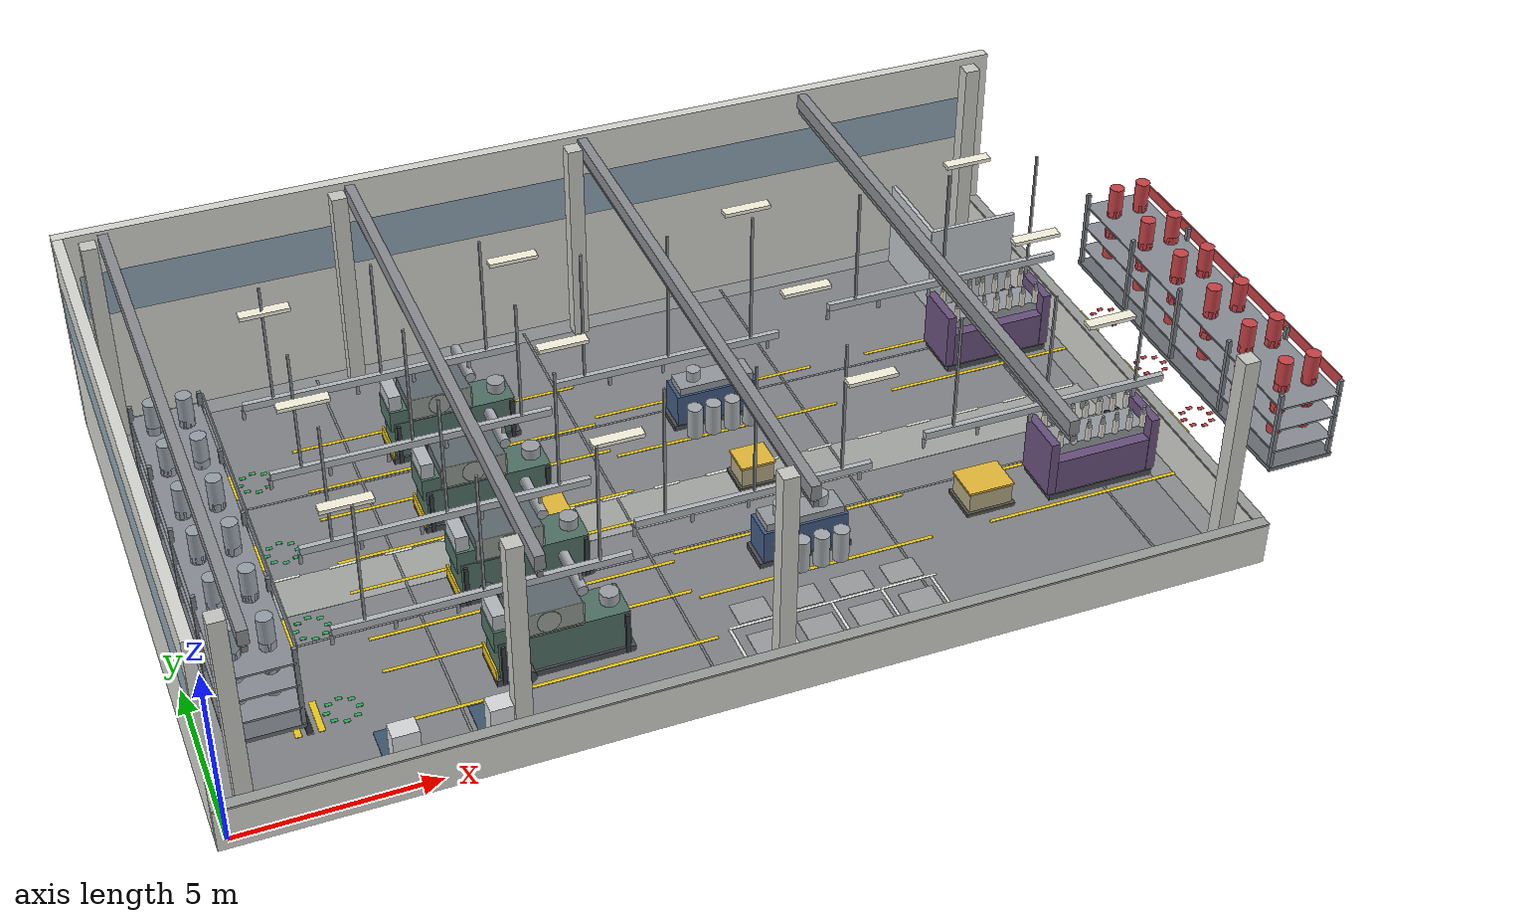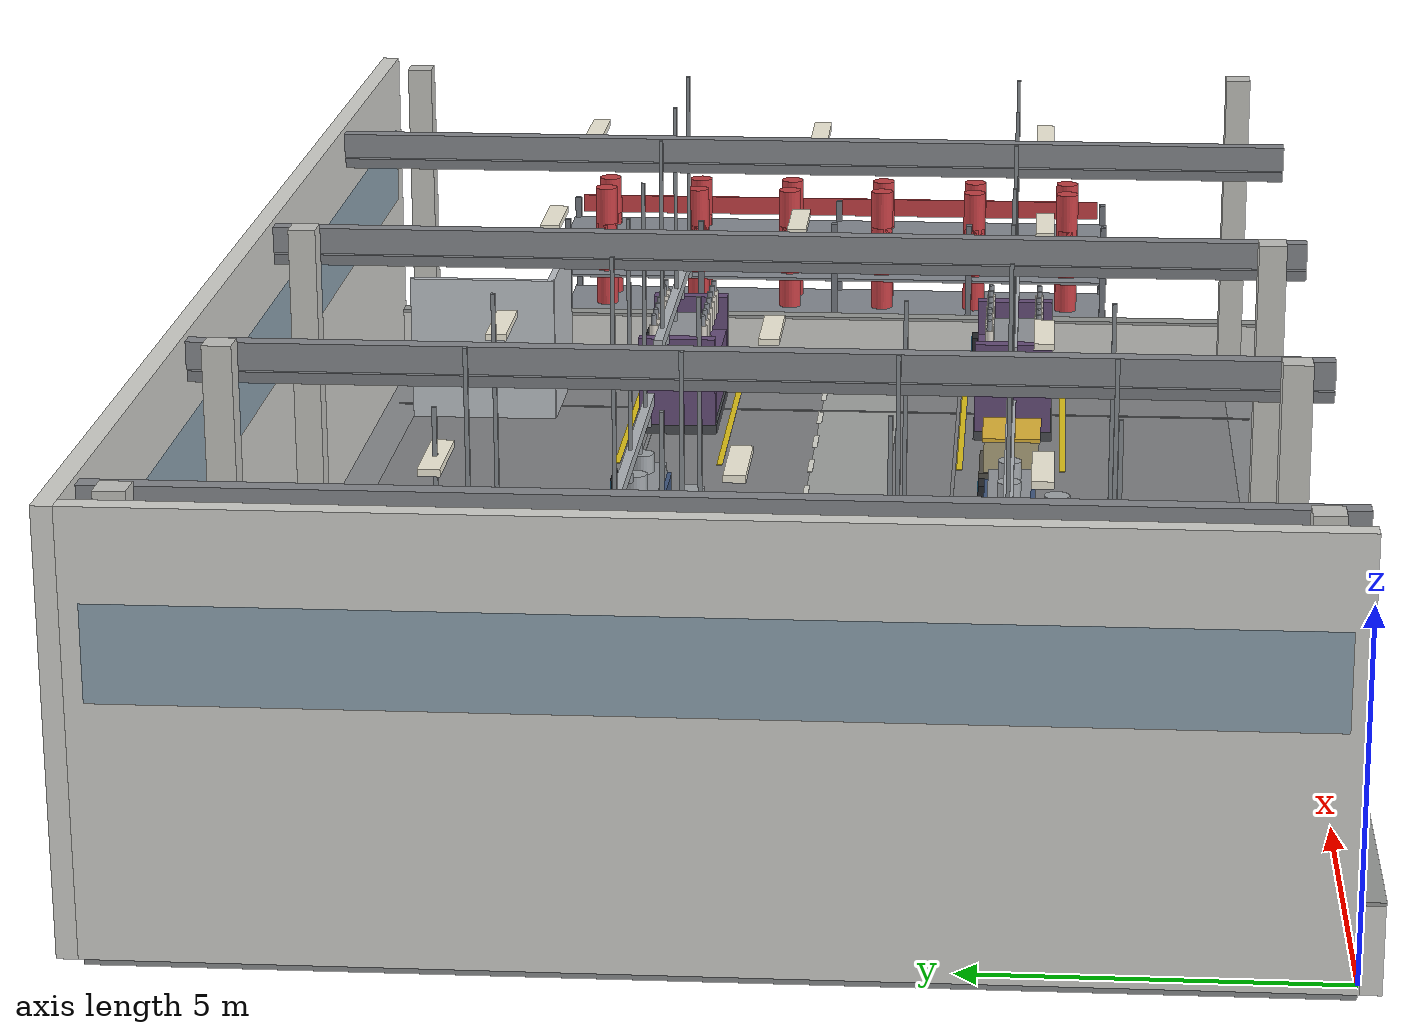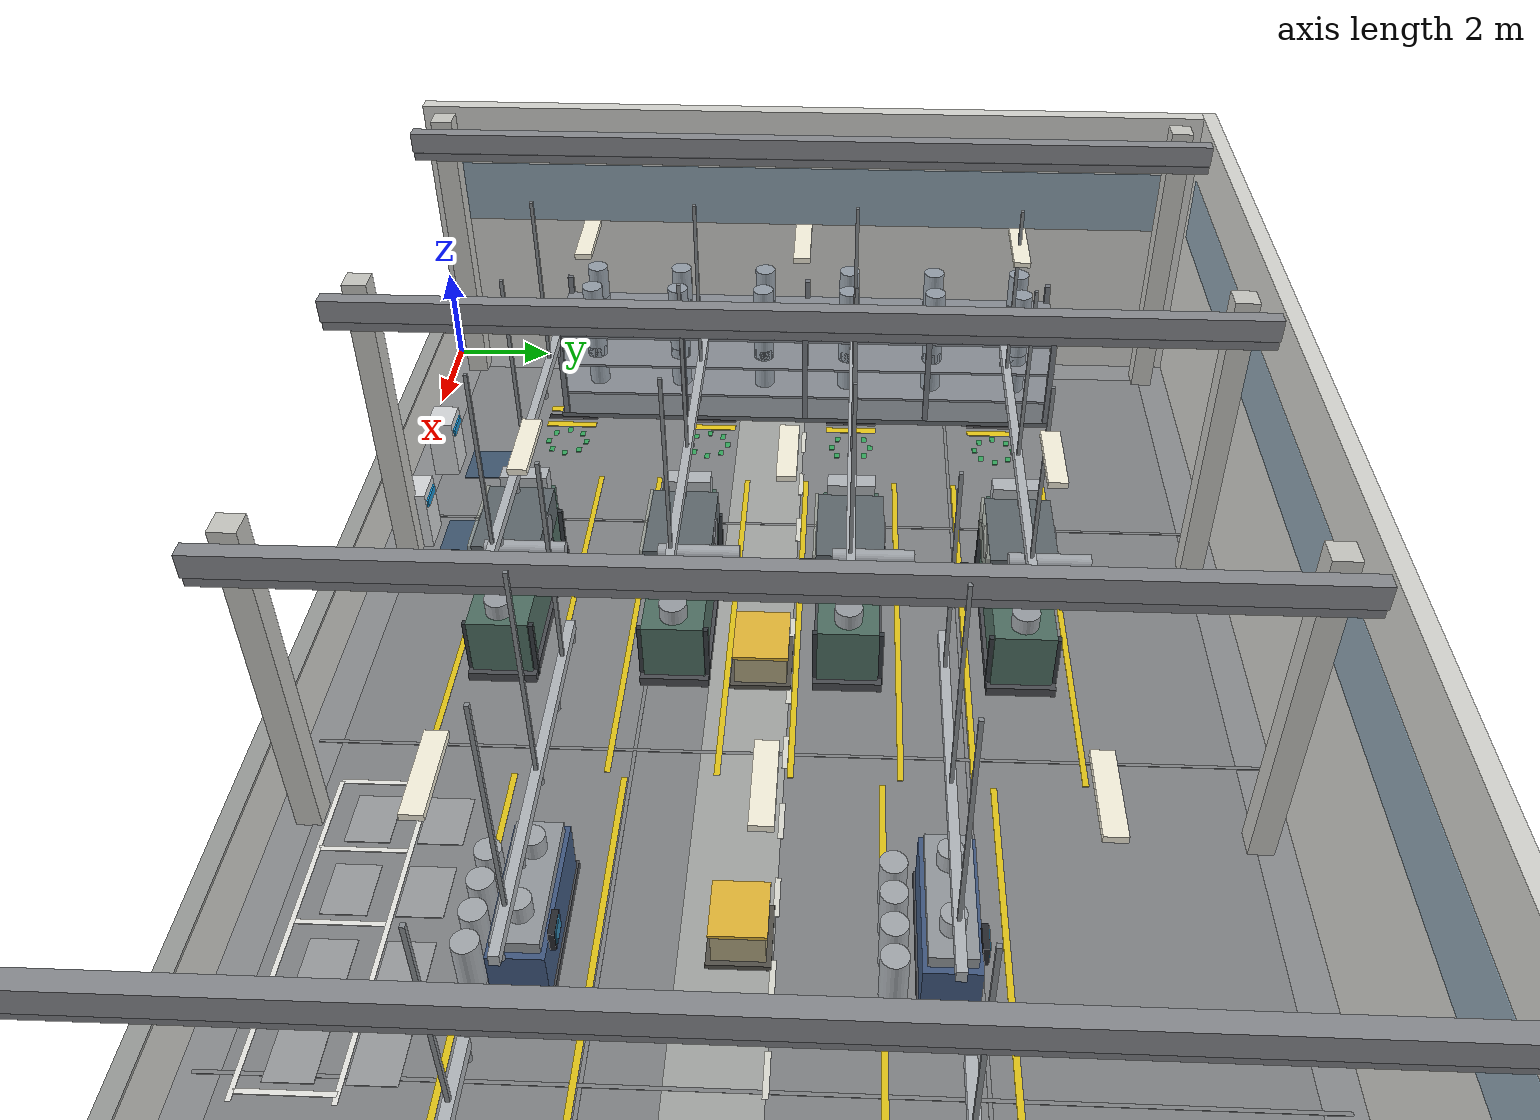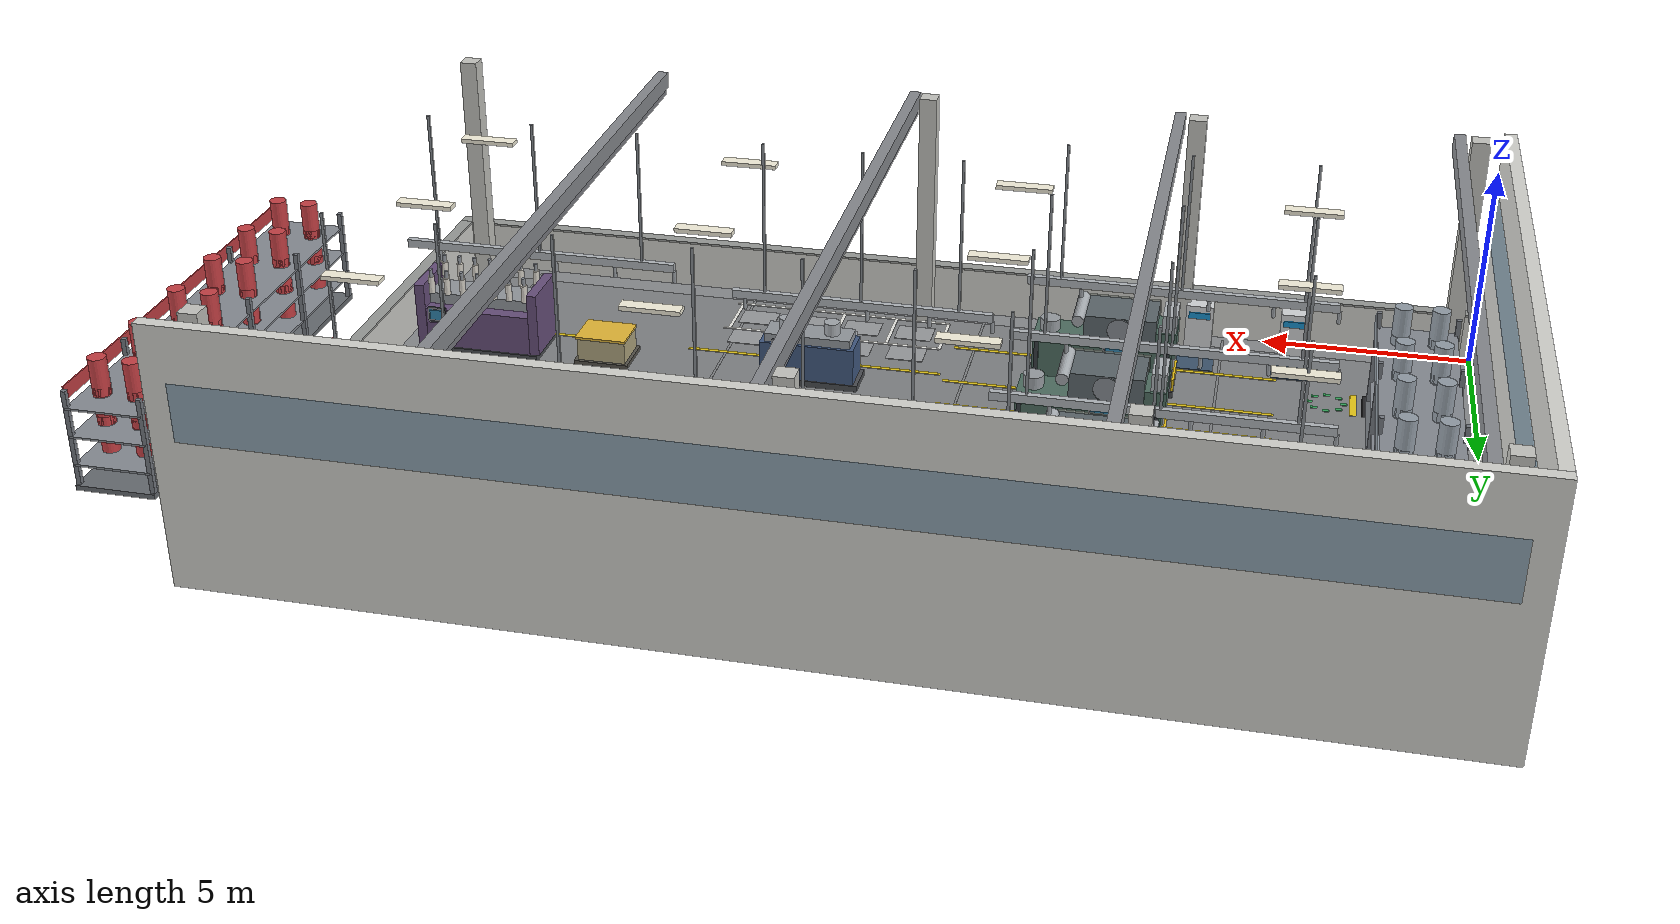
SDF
<?xml version="1.0" ?>
<sdf version="1.10">
  <world name="textile_mill">
    <physics name="4ms" type="ignored"><max_step_size>0.004</max_step_size><real_time_factor>1.0</real_time_factor></physics>
    <plugin filename="gz-sim-physics-system" name="gz::sim::systems::Physics"/>
    <plugin filename="gz-sim-user-commands-system" name="gz::sim::systems::UserCommands"/>
    <plugin filename="gz-sim-scene-broadcaster-system" name="gz::sim::systems::SceneBroadcaster"/>
    <plugin filename="gz-sim-sensors-system" name="gz::sim::systems::Sensors"><render_engine>ogre2</render_engine></plugin>
    <plugin filename="gz-sim-contact-system" name="gz::sim::systems::Contact"/>
    <light type="directional" name="skylight">
      <cast_shadows>true</cast_shadows><pose>0 0 24 0 0 0</pose>
      <diffuse>1.00 0.99 0.94 1</diffuse><specular>0.22 0.22 0.22 1</specular>
      <direction>-0.42 0.30 -1</direction>
      <shadow><cascade_count>3</cascade_count><texture_size>2048</texture_size>
      <cascade_distribution>0.45 0.75 0.95</cascade_distribution></shadow>
    </light>
    <light type="point" name="lamp_0"><cast_shadows>false</cast_shadows>
      <pose>5 5 5.2 0 0 0</pose><diffuse>0.82 0.80 0.74 1</diffuse><specular>0.14 0.14 0.14 1</specular>
      <attenuation><range>18</range><constant>0.6</constant><linear>0.05</linear><quadratic>0.006</quadratic></attenuation>
    </light>
    <light type="point" name="lamp_1"><cast_shadows>false</cast_shadows>
      <pose>11 11 5.2 0 0 0</pose><diffuse>0.82 0.80 0.74 1</diffuse><specular>0.14 0.14 0.14 1</specular>
      <attenuation><range>18</range><constant>0.6</constant><linear>0.05</linear><quadratic>0.006</quadratic></attenuation>
    </light>
    <light type="point" name="lamp_2"><cast_shadows>false</cast_shadows>
      <pose>19 6 5.2 0 0 0</pose><diffuse>0.82 0.80 0.74 1</diffuse><specular>0.14 0.14 0.14 1</specular>
      <attenuation><range>18</range><constant>0.6</constant><linear>0.05</linear><quadratic>0.006</quadratic></attenuation>
    </light>
    <scene><ambient>0.42 0.43 0.45 1</ambient><background>0.74 0.78 0.82 1</background><shadows>true</shadows></scene>
    <model name="floor_slab"><static>true</static><pose>13.000 8.000 -0.100 0 0 0</pose><link name="l"><collision name="c"><geometry><box><size>26.000 16.000 0.200</size></box></geometry></collision><visual name="v"><geometry><box><size>26.000 16.000 0.200</size></box></geometry><material><ambient>0.560 0.570 0.580 1.0</ambient><diffuse>0.560 0.570 0.580 1.0</diffuse><specular>0.18 0.18 0.18 1</specular><pbr><metal><roughness>0.94</roughness><metalness>0.0</metalness></metal></pbr></material></visual></link></model>
    <model name="floor_wear"><static>true</static><pose>13.000 8.000 0.005 0 0 0</pose><link name="l"><collision name="c"><geometry><box><size>24.800 14.800 0.010</size></box></geometry></collision><visual name="v"><geometry><box><size>24.800 14.800 0.010</size></box></geometry><material><ambient>0.520 0.530 0.540 1.0</ambient><diffuse>0.520 0.530 0.540 1.0</diffuse><specular>0.18 0.18 0.18 1</specular><pbr><metal><roughness>0.96</roughness><metalness>0.0</metalness></metal></pbr></material></visual></link></model>
    <model name="wall_south"><static>true</static><pose>13.000 -0.140 0.600 0 0 0</pose><link name="l"><collision name="c"><geometry><box><size>26.560 0.280 1.200</size></box></geometry></collision><visual name="v"><geometry><box><size>26.560 0.280 1.200</size></box></geometry><material><ambient>0.860 0.860 0.840 1.0</ambient><diffuse>0.860 0.860 0.840 1.0</diffuse><specular>0.18 0.18 0.18 1</specular><pbr><metal><roughness>0.9</roughness><metalness>0.0</metalness></metal></pbr></material></visual></link></model>
    <model name="wall_east"><static>true</static><pose>26.140 8.000 0.600 0 0 0</pose><link name="l"><collision name="c"><geometry><box><size>0.280 16.000 1.200</size></box></geometry></collision><visual name="v"><geometry><box><size>0.280 16.000 1.200</size></box></geometry><material><ambient>0.860 0.860 0.840 1.0</ambient><diffuse>0.860 0.860 0.840 1.0</diffuse><specular>0.18 0.18 0.18 1</specular><pbr><metal><roughness>0.9</roughness><metalness>0.0</metalness></metal></pbr></material></visual></link></model>
    <model name="wall_north"><static>true</static><pose>13.000 16.140 3.000 0 0 0</pose><link name="l"><collision name="c"><geometry><box><size>26.560 0.280 6.000</size></box></geometry></collision><visual name="v"><geometry><box><size>26.560 0.280 6.000</size></box></geometry><material><ambient>0.860 0.860 0.840 1.0</ambient><diffuse>0.860 0.860 0.840 1.0</diffuse><specular>0.18 0.18 0.18 1</specular><pbr><metal><roughness>0.9</roughness><metalness>0.0</metalness></metal></pbr></material></visual></link></model>
    <model name="wall_west"><static>true</static><pose>-0.140 8.000 3.000 0 0 0</pose><link name="l"><collision name="c"><geometry><box><size>0.280 16.000 6.000</size></box></geometry></collision><visual name="v"><geometry><box><size>0.280 16.000 6.000</size></box></geometry><material><ambient>0.860 0.860 0.840 1.0</ambient><diffuse>0.860 0.860 0.840 1.0</diffuse><specular>0.18 0.18 0.18 1</specular><pbr><metal><roughness>0.9</roughness><metalness>0.0</metalness></metal></pbr></material></visual></link></model>
    <model name="cut_s"><static>true</static><pose>13.000 -0.140 1.220 0 0 0</pose><link name="l"><collision name="c"><geometry><box><size>26.560 0.300 0.050</size></box></geometry></collision><visual name="v"><geometry><box><size>26.560 0.300 0.050</size></box></geometry><material><ambient>0.620 0.630 0.620 1.0</ambient><diffuse>0.620 0.630 0.620 1.0</diffuse><specular>0.18 0.18 0.18 1</specular><pbr><metal><roughness>0.65</roughness><metalness>0.0</metalness></metal></pbr></material></visual></link></model>
    <model name="cut_e"><static>true</static><pose>26.140 8.000 1.220 0 0 0</pose><link name="l"><collision name="c"><geometry><box><size>0.300 16.000 0.050</size></box></geometry></collision><visual name="v"><geometry><box><size>0.300 16.000 0.050</size></box></geometry><material><ambient>0.620 0.630 0.620 1.0</ambient><diffuse>0.620 0.630 0.620 1.0</diffuse><specular>0.18 0.18 0.18 1</specular><pbr><metal><roughness>0.65</roughness><metalness>0.0</metalness></metal></pbr></material></visual></link></model>
    <model name="win_n"><static>true</static><pose>13.000 16.140 4.100 0 0 0</pose><link name="l"><collision name="c"><geometry><box><size>25.500 0.300 1.300</size></box></geometry></collision><visual name="v"><geometry><box><size>25.500 0.300 1.300</size></box></geometry><material><ambient>0.420 0.580 0.700 0.55</ambient><diffuse>0.420 0.580 0.700 0.55</diffuse><specular>0.18 0.18 0.18 1</specular><pbr><metal><roughness>0.15</roughness><metalness>0.1</metalness></metal></pbr></material></visual></link></model>
    <model name="win_w"><static>true</static><pose>-0.140 8.000 4.100 0 0 0</pose><link name="l"><collision name="c"><geometry><box><size>0.300 15.500 1.300</size></box></geometry></collision><visual name="v"><geometry><box><size>0.300 15.500 1.300</size></box></geometry><material><ambient>0.420 0.580 0.700 0.55</ambient><diffuse>0.420 0.580 0.700 0.55</diffuse><specular>0.18 0.18 0.18 1</specular><pbr><metal><roughness>0.15</roughness><metalness>0.1</metalness></metal></pbr></material></visual></link></model>
    <model name="col_0"><static>true</static><pose>0.550 0.550 3.000 0 0 0</pose><link name="l"><collision name="c"><geometry><box><size>0.420 0.420 6.000</size></box></geometry></collision><visual name="v"><geometry><box><size>0.420 0.420 6.000</size></box></geometry><material><ambient>0.800 0.800 0.780 1.0</ambient><diffuse>0.800 0.800 0.780 1.0</diffuse><specular>0.18 0.18 0.18 1</specular><pbr><metal><roughness>0.85</roughness><metalness>0.0</metalness></metal></pbr></material></visual></link></model>
    <model name="col_1"><static>true</static><pose>0.550 15.450 3.000 0 0 0</pose><link name="l"><collision name="c"><geometry><box><size>0.420 0.420 6.000</size></box></geometry></collision><visual name="v"><geometry><box><size>0.420 0.420 6.000</size></box></geometry><material><ambient>0.800 0.800 0.780 1.0</ambient><diffuse>0.800 0.800 0.780 1.0</diffuse><specular>0.18 0.18 0.18 1</specular><pbr><metal><roughness>0.85</roughness><metalness>0.0</metalness></metal></pbr></material></visual></link></model>
    <model name="col_2"><static>true</static><pose>7.050 0.550 3.000 0 0 0</pose><link name="l"><collision name="c"><geometry><box><size>0.420 0.420 6.000</size></box></geometry></collision><visual name="v"><geometry><box><size>0.420 0.420 6.000</size></box></geometry><material><ambient>0.800 0.800 0.780 1.0</ambient><diffuse>0.800 0.800 0.780 1.0</diffuse><specular>0.18 0.18 0.18 1</specular><pbr><metal><roughness>0.85</roughness><metalness>0.0</metalness></metal></pbr></material></visual></link></model>
    <model name="col_3"><static>true</static><pose>7.050 15.450 3.000 0 0 0</pose><link name="l"><collision name="c"><geometry><box><size>0.420 0.420 6.000</size></box></geometry></collision><visual name="v"><geometry><box><size>0.420 0.420 6.000</size></box></geometry><material><ambient>0.800 0.800 0.780 1.0</ambient><diffuse>0.800 0.800 0.780 1.0</diffuse><specular>0.18 0.18 0.18 1</specular><pbr><metal><roughness>0.85</roughness><metalness>0.0</metalness></metal></pbr></material></visual></link></model>
    <model name="col_4"><static>true</static><pose>13.550 0.550 3.000 0 0 0</pose><link name="l"><collision name="c"><geometry><box><size>0.420 0.420 6.000</size></box></geometry></collision><visual name="v"><geometry><box><size>0.420 0.420 6.000</size></box></geometry><material><ambient>0.800 0.800 0.780 1.0</ambient><diffuse>0.800 0.800 0.780 1.0</diffuse><specular>0.18 0.18 0.18 1</specular><pbr><metal><roughness>0.85</roughness><metalness>0.0</metalness></metal></pbr></material></visual></link></model>
    <model name="col_5"><static>true</static><pose>13.550 15.450 3.000 0 0 0</pose><link name="l"><collision name="c"><geometry><box><size>0.420 0.420 6.000</size></box></geometry></collision><visual name="v"><geometry><box><size>0.420 0.420 6.000</size></box></geometry><material><ambient>0.800 0.800 0.780 1.0</ambient><diffuse>0.800 0.800 0.780 1.0</diffuse><specular>0.18 0.18 0.18 1</specular><pbr><metal><roughness>0.85</roughness><metalness>0.0</metalness></metal></pbr></material></visual></link></model>
    <model name="col_6"><static>true</static><pose>25.450 0.550 3.000 0 0 0</pose><link name="l"><collision name="c"><geometry><box><size>0.420 0.420 6.000</size></box></geometry></collision><visual name="v"><geometry><box><size>0.420 0.420 6.000</size></box></geometry><material><ambient>0.800 0.800 0.780 1.0</ambient><diffuse>0.800 0.800 0.780 1.0</diffuse><specular>0.18 0.18 0.18 1</specular><pbr><metal><roughness>0.85</roughness><metalness>0.0</metalness></metal></pbr></material></visual></link></model>
    <model name="col_7"><static>true</static><pose>25.450 15.450 3.000 0 0 0</pose><link name="l"><collision name="c"><geometry><box><size>0.420 0.420 6.000</size></box></geometry></collision><visual name="v"><geometry><box><size>0.420 0.420 6.000</size></box></geometry><material><ambient>0.800 0.800 0.780 1.0</ambient><diffuse>0.800 0.800 0.780 1.0</diffuse><specular>0.18 0.18 0.18 1</specular><pbr><metal><roughness>0.85</roughness><metalness>0.0</metalness></metal></pbr></material></visual></link></model>
    <model name="truss_0"><static>true</static><pose>1.000 8.000 5.700 0 0 0</pose><link name="l"><collision name="c"><geometry><box><size>0.260 16.000 0.400</size></box></geometry></collision><visual name="v"><geometry><box><size>0.260 16.000 0.400</size></box></geometry><material><ambient>0.550 0.560 0.580 1.0</ambient><diffuse>0.550 0.560 0.580 1.0</diffuse><specular>0.18 0.18 0.18 1</specular><pbr><metal><roughness>0.4</roughness><metalness>0.6</metalness></metal></pbr></material></visual></link></model>
    <model name="truss_lo_0"><static>true</static><pose>1.000 8.000 5.380 0 0 0</pose><link name="l"><collision name="c"><geometry><box><size>0.140 16.000 0.160</size></box></geometry></collision><visual name="v"><geometry><box><size>0.140 16.000 0.160</size></box></geometry><material><ambient>0.500 0.510 0.530 1.0</ambient><diffuse>0.500 0.510 0.530 1.0</diffuse><specular>0.18 0.18 0.18 1</specular><pbr><metal><roughness>0.65</roughness><metalness>0.6</metalness></metal></pbr></material></visual></link></model>
    <model name="truss_1"><static>true</static><pose>7.500 8.000 5.700 0 0 0</pose><link name="l"><collision name="c"><geometry><box><size>0.260 16.000 0.400</size></box></geometry></collision><visual name="v"><geometry><box><size>0.260 16.000 0.400</size></box></geometry><material><ambient>0.550 0.560 0.580 1.0</ambient><diffuse>0.550 0.560 0.580 1.0</diffuse><specular>0.18 0.18 0.18 1</specular><pbr><metal><roughness>0.4</roughness><metalness>0.6</metalness></metal></pbr></material></visual></link></model>
    <model name="truss_lo_1"><static>true</static><pose>7.500 8.000 5.380 0 0 0</pose><link name="l"><collision name="c"><geometry><box><size>0.140 16.000 0.160</size></box></geometry></collision><visual name="v"><geometry><box><size>0.140 16.000 0.160</size></box></geometry><material><ambient>0.500 0.510 0.530 1.0</ambient><diffuse>0.500 0.510 0.530 1.0</diffuse><specular>0.18 0.18 0.18 1</specular><pbr><metal><roughness>0.65</roughness><metalness>0.6</metalness></metal></pbr></material></visual></link></model>
    <model name="truss_2"><static>true</static><pose>14.000 8.000 5.700 0 0 0</pose><link name="l"><collision name="c"><geometry><box><size>0.260 16.000 0.400</size></box></geometry></collision><visual name="v"><geometry><box><size>0.260 16.000 0.400</size></box></geometry><material><ambient>0.550 0.560 0.580 1.0</ambient><diffuse>0.550 0.560 0.580 1.0</diffuse><specular>0.18 0.18 0.18 1</specular><pbr><metal><roughness>0.4</roughness><metalness>0.6</metalness></metal></pbr></material></visual></link></model>
    <model name="truss_lo_2"><static>true</static><pose>14.000 8.000 5.380 0 0 0</pose><link name="l"><collision name="c"><geometry><box><size>0.140 16.000 0.160</size></box></geometry></collision><visual name="v"><geometry><box><size>0.140 16.000 0.160</size></box></geometry><material><ambient>0.500 0.510 0.530 1.0</ambient><diffuse>0.500 0.510 0.530 1.0</diffuse><specular>0.18 0.18 0.18 1</specular><pbr><metal><roughness>0.65</roughness><metalness>0.6</metalness></metal></pbr></material></visual></link></model>
    <model name="truss_3"><static>true</static><pose>20.500 8.000 5.700 0 0 0</pose><link name="l"><collision name="c"><geometry><box><size>0.260 16.000 0.400</size></box></geometry></collision><visual name="v"><geometry><box><size>0.260 16.000 0.400</size></box></geometry><material><ambient>0.550 0.560 0.580 1.0</ambient><diffuse>0.550 0.560 0.580 1.0</diffuse><specular>0.18 0.18 0.18 1</specular><pbr><metal><roughness>0.4</roughness><metalness>0.6</metalness></metal></pbr></material></visual></link></model>
    <model name="truss_lo_3"><static>true</static><pose>20.500 8.000 5.380 0 0 0</pose><link name="l"><collision name="c"><geometry><box><size>0.140 16.000 0.160</size></box></geometry></collision><visual name="v"><geometry><box><size>0.140 16.000 0.160</size></box></geometry><material><ambient>0.500 0.510 0.530 1.0</ambient><diffuse>0.500 0.510 0.530 1.0</diffuse><specular>0.18 0.18 0.18 1</specular><pbr><metal><roughness>0.65</roughness><metalness>0.6</metalness></metal></pbr></material></visual></link></model>
    <model name="lamp_0_0"><static>true</static><pose>4.200 4.000 5.280 0 0 0</pose><link name="l"><collision name="c"><geometry><box><size>1.300 0.300 0.100</size></box></geometry></collision><visual name="v"><geometry><box><size>1.300 0.300 0.100</size></box></geometry><material><ambient>1.000 0.980 0.900 1.0</ambient><diffuse>1.000 0.980 0.900 1.0</diffuse><specular>0.18 0.18 0.18 1</specular><pbr><metal><roughness>0.3</roughness><metalness>0.0</metalness></metal></pbr></material></visual></link></model>
    <model name="lamp_0_1"><static>true</static><pose>4.200 8.000 5.280 0 0 0</pose><link name="l"><collision name="c"><geometry><box><size>1.300 0.300 0.100</size></box></geometry></collision><visual name="v"><geometry><box><size>1.300 0.300 0.100</size></box></geometry><material><ambient>1.000 0.980 0.900 1.0</ambient><diffuse>1.000 0.980 0.900 1.0</diffuse><specular>0.18 0.18 0.18 1</specular><pbr><metal><roughness>0.3</roughness><metalness>0.0</metalness></metal></pbr></material></visual></link></model>
    <model name="lamp_0_2"><static>true</static><pose>4.200 12.000 5.280 0 0 0</pose><link name="l"><collision name="c"><geometry><box><size>1.300 0.300 0.100</size></box></geometry></collision><visual name="v"><geometry><box><size>1.300 0.300 0.100</size></box></geometry><material><ambient>1.000 0.980 0.900 1.0</ambient><diffuse>1.000 0.980 0.900 1.0</diffuse><specular>0.18 0.18 0.18 1</specular><pbr><metal><roughness>0.3</roughness><metalness>0.0</metalness></metal></pbr></material></visual></link></model>
    <model name="lamp_1_0"><static>true</static><pose>10.700 4.000 5.280 0 0 0</pose><link name="l"><collision name="c"><geometry><box><size>1.300 0.300 0.100</size></box></geometry></collision><visual name="v"><geometry><box><size>1.300 0.300 0.100</size></box></geometry><material><ambient>1.000 0.980 0.900 1.0</ambient><diffuse>1.000 0.980 0.900 1.0</diffuse><specular>0.18 0.18 0.18 1</specular><pbr><metal><roughness>0.3</roughness><metalness>0.0</metalness></metal></pbr></material></visual></link></model>
    <model name="lamp_1_1"><static>true</static><pose>10.700 8.000 5.280 0 0 0</pose><link name="l"><collision name="c"><geometry><box><size>1.300 0.300 0.100</size></box></geometry></collision><visual name="v"><geometry><box><size>1.300 0.300 0.100</size></box></geometry><material><ambient>1.000 0.980 0.900 1.0</ambient><diffuse>1.000 0.980 0.900 1.0</diffuse><specular>0.18 0.18 0.18 1</specular><pbr><metal><roughness>0.3</roughness><metalness>0.0</metalness></metal></pbr></material></visual></link></model>
    <model name="lamp_1_2"><static>true</static><pose>10.700 12.000 5.280 0 0 0</pose><link name="l"><collision name="c"><geometry><box><size>1.300 0.300 0.100</size></box></geometry></collision><visual name="v"><geometry><box><size>1.300 0.300 0.100</size></box></geometry><material><ambient>1.000 0.980 0.900 1.0</ambient><diffuse>1.000 0.980 0.900 1.0</diffuse><specular>0.18 0.18 0.18 1</specular><pbr><metal><roughness>0.3</roughness><metalness>0.0</metalness></metal></pbr></material></visual></link></model>
    <model name="lamp_2_0"><static>true</static><pose>17.200 4.000 5.280 0 0 0</pose><link name="l"><collision name="c"><geometry><box><size>1.300 0.300 0.100</size></box></geometry></collision><visual name="v"><geometry><box><size>1.300 0.300 0.100</size></box></geometry><material><ambient>1.000 0.980 0.900 1.0</ambient><diffuse>1.000 0.980 0.900 1.0</diffuse><specular>0.18 0.18 0.18 1</specular><pbr><metal><roughness>0.3</roughness><metalness>0.0</metalness></metal></pbr></material></visual></link></model>
    <model name="lamp_2_1"><static>true</static><pose>17.200 8.000 5.280 0 0 0</pose><link name="l"><collision name="c"><geometry><box><size>1.300 0.300 0.100</size></box></geometry></collision><visual name="v"><geometry><box><size>1.300 0.300 0.100</size></box></geometry><material><ambient>1.000 0.980 0.900 1.0</ambient><diffuse>1.000 0.980 0.900 1.0</diffuse><specular>0.18 0.18 0.18 1</specular><pbr><metal><roughness>0.3</roughness><metalness>0.0</metalness></metal></pbr></material></visual></link></model>
    <model name="lamp_2_2"><static>true</static><pose>17.200 12.000 5.280 0 0 0</pose><link name="l"><collision name="c"><geometry><box><size>1.300 0.300 0.100</size></box></geometry></collision><visual name="v"><geometry><box><size>1.300 0.300 0.100</size></box></geometry><material><ambient>1.000 0.980 0.900 1.0</ambient><diffuse>1.000 0.980 0.900 1.0</diffuse><specular>0.18 0.18 0.18 1</specular><pbr><metal><roughness>0.3</roughness><metalness>0.0</metalness></metal></pbr></material></visual></link></model>
    <model name="lamp_3_0"><static>true</static><pose>23.700 4.000 5.280 0 0 0</pose><link name="l"><collision name="c"><geometry><box><size>1.300 0.300 0.100</size></box></geometry></collision><visual name="v"><geometry><box><size>1.300 0.300 0.100</size></box></geometry><material><ambient>1.000 0.980 0.900 1.0</ambient><diffuse>1.000 0.980 0.900 1.0</diffuse><specular>0.18 0.18 0.18 1</specular><pbr><metal><roughness>0.3</roughness><metalness>0.0</metalness></metal></pbr></material></visual></link></model>
    <model name="lamp_3_1"><static>true</static><pose>23.700 8.000 5.280 0 0 0</pose><link name="l"><collision name="c"><geometry><box><size>1.300 0.300 0.100</size></box></geometry></collision><visual name="v"><geometry><box><size>1.300 0.300 0.100</size></box></geometry><material><ambient>1.000 0.980 0.900 1.0</ambient><diffuse>1.000 0.980 0.900 1.0</diffuse><specular>0.18 0.18 0.18 1</specular><pbr><metal><roughness>0.3</roughness><metalness>0.0</metalness></metal></pbr></material></visual></link></model>
    <model name="lamp_3_2"><static>true</static><pose>23.700 12.000 5.280 0 0 0</pose><link name="l"><collision name="c"><geometry><box><size>1.300 0.300 0.100</size></box></geometry></collision><visual name="v"><geometry><box><size>1.300 0.300 0.100</size></box></geometry><material><ambient>1.000 0.980 0.900 1.0</ambient><diffuse>1.000 0.980 0.900 1.0</diffuse><specular>0.18 0.18 0.18 1</specular><pbr><metal><roughness>0.3</roughness><metalness>0.0</metalness></metal></pbr></material></visual></link></model>
    <model name="obs_pallet_a"><static>true</static><pose>9.900 7.500 0.340 0 0 0</pose><link name="l"><collision name="c"><geometry><box><size>1.100 0.900 0.680</size></box></geometry></collision><visual name="v"><geometry><box><size>1.100 0.900 0.680</size></box></geometry><material><ambient>0.720 0.680 0.520 1.0</ambient><diffuse>0.720 0.680 0.520 1.0</diffuse><specular>0.18 0.18 0.18 1</specular><pbr><metal><roughness>0.85</roughness><metalness>0.0</metalness></metal></pbr></material></visual></link></model>
    <model name="obsband_pallet_a"><static>true</static><pose>9.900 7.500 0.700 0 0 0</pose><link name="l"><collision name="c"><geometry><box><size>1.160 0.960 0.060</size></box></geometry></collision><visual name="v"><geometry><box><size>1.160 0.960 0.060</size></box></geometry><material><ambient>0.920 0.740 0.220 1.0</ambient><diffuse>0.920 0.740 0.220 1.0</diffuse><specular>0.18 0.18 0.18 1</specular><pbr><metal><roughness>0.65</roughness><metalness>0.0</metalness></metal></pbr></material></visual></link></model>
    <model name="obsfoot_pallet_a"><static>true</static><pose>9.900 7.500 0.060 0 0 0</pose><link name="l"><collision name="c"><geometry><box><size>1.260 1.060 0.100</size></box></geometry></collision><visual name="v"><geometry><box><size>1.260 1.060 0.100</size></box></geometry><material><ambient>0.340 0.330 0.300 1.0</ambient><diffuse>0.340 0.330 0.300 1.0</diffuse><specular>0.18 0.18 0.18 1</specular><pbr><metal><roughness>0.65</roughness><metalness>0.0</metalness></metal></pbr></material></visual></link></model>
    <model name="obs_cart_b"><static>true</static><pose>15.600 7.500 0.340 0 0 0</pose><link name="l"><collision name="c"><geometry><box><size>0.900 0.800 0.680</size></box></geometry></collision><visual name="v"><geometry><box><size>0.900 0.800 0.680</size></box></geometry><material><ambient>0.720 0.680 0.520 1.0</ambient><diffuse>0.720 0.680 0.520 1.0</diffuse><specular>0.18 0.18 0.18 1</specular><pbr><metal><roughness>0.85</roughness><metalness>0.0</metalness></metal></pbr></material></visual></link></model>
    <model name="obsband_cart_b"><static>true</static><pose>15.600 7.500 0.700 0 0 0</pose><link name="l"><collision name="c"><geometry><box><size>0.960 0.860 0.060</size></box></geometry></collision><visual name="v"><geometry><box><size>0.960 0.860 0.060</size></box></geometry><material><ambient>0.920 0.740 0.220 1.0</ambient><diffuse>0.920 0.740 0.220 1.0</diffuse><specular>0.18 0.18 0.18 1</specular><pbr><metal><roughness>0.65</roughness><metalness>0.0</metalness></metal></pbr></material></visual></link></model>
    <model name="obsfoot_cart_b"><static>true</static><pose>15.600 7.500 0.060 0 0 0</pose><link name="l"><collision name="c"><geometry><box><size>1.060 0.960 0.100</size></box></geometry></collision><visual name="v"><geometry><box><size>1.060 0.960 0.100</size></box></geometry><material><ambient>0.340 0.330 0.300 1.0</ambient><diffuse>0.340 0.330 0.300 1.0</diffuse><specular>0.18 0.18 0.18 1</specular><pbr><metal><roughness>0.65</roughness><metalness>0.0</metalness></metal></pbr></material></visual></link></model>
    <model name="obs_bale_c"><static>true</static><pose>20.800 4.500 0.340 0 0 0</pose><link name="l"><collision name="c"><geometry><box><size>1.200 0.950 0.680</size></box></geometry></collision><visual name="v"><geometry><box><size>1.200 0.950 0.680</size></box></geometry><material><ambient>0.720 0.680 0.520 1.0</ambient><diffuse>0.720 0.680 0.520 1.0</diffuse><specular>0.18 0.18 0.18 1</specular><pbr><metal><roughness>0.85</roughness><metalness>0.0</metalness></metal></pbr></material></visual></link></model>
    <model name="obsband_bale_c"><static>true</static><pose>20.800 4.500 0.700 0 0 0</pose><link name="l"><collision name="c"><geometry><box><size>1.260 1.010 0.060</size></box></geometry></collision><visual name="v"><geometry><box><size>1.260 1.010 0.060</size></box></geometry><material><ambient>0.920 0.740 0.220 1.0</ambient><diffuse>0.920 0.740 0.220 1.0</diffuse><specular>0.18 0.18 0.18 1</specular><pbr><metal><roughness>0.65</roughness><metalness>0.0</metalness></metal></pbr></material></visual></link></model>
    <model name="obsfoot_bale_c"><static>true</static><pose>20.800 4.500 0.060 0 0 0</pose><link name="l"><collision name="c"><geometry><box><size>1.360 1.110 0.100</size></box></geometry></collision><visual name="v"><geometry><box><size>1.360 1.110 0.100</size></box></geometry><material><ambient>0.340 0.330 0.300 1.0</ambient><diffuse>0.340 0.330 0.300 1.0</diffuse><specular>0.18 0.18 0.18 1</specular><pbr><metal><roughness>0.65</roughness><metalness>0.0</metalness></metal></pbr></material></visual></link></model>
    <model name="cln_carding_0"><static>true</static><pose>7.000 3.000 2.520 0 0 0</pose><link name="l"><collision name="c"><geometry><box><size>7.300 0.150 0.200</size></box></geometry></collision><visual name="v"><geometry><box><size>7.300 0.150 0.200</size></box></geometry><material><ambient>0.720 0.740 0.760 1.0</ambient><diffuse>0.720 0.740 0.760 1.0</diffuse><specular>0.18 0.18 0.18 1</specular><pbr><metal><roughness>0.35</roughness><metalness>0.5</metalness></metal></pbr></material></visual></link></model>
    <model name="clnz_carding_0_0"><static>true</static><pose>3.350 3.000 2.280 0.0000 0.0000 0.0000</pose><link name="l"><collision name="c"><geometry><cylinder><radius>0.045</radius><length>0.300</length></cylinder></geometry></collision><visual name="v"><geometry><cylinder><radius>0.045</radius><length>0.300</length></cylinder></geometry><material><ambient>0.580 0.600 0.620 1.0</ambient><diffuse>0.580 0.600 0.620 1.0</diffuse><specular>0.18 0.18 0.18 1</specular><pbr><metal><roughness>0.35</roughness><metalness>0.5</metalness></metal></pbr></material></visual></link></model>
    <model name="clnz_carding_0_1"><static>true</static><pose>4.850 3.000 2.280 0.0000 0.0000 0.0000</pose><link name="l"><collision name="c"><geometry><cylinder><radius>0.045</radius><length>0.300</length></cylinder></geometry></collision><visual name="v"><geometry><cylinder><radius>0.045</radius><length>0.300</length></cylinder></geometry><material><ambient>0.580 0.600 0.620 1.0</ambient><diffuse>0.580 0.600 0.620 1.0</diffuse><specular>0.18 0.18 0.18 1</specular><pbr><metal><roughness>0.35</roughness><metalness>0.5</metalness></metal></pbr></material></visual></link></model>
    <model name="clnz_carding_0_2"><static>true</static><pose>6.350 3.000 2.280 0.0000 0.0000 0.0000</pose><link name="l"><collision name="c"><geometry><cylinder><radius>0.045</radius><length>0.300</length></cylinder></geometry></collision><visual name="v"><geometry><cylinder><radius>0.045</radius><length>0.300</length></cylinder></geometry><material><ambient>0.580 0.600 0.620 1.0</ambient><diffuse>0.580 0.600 0.620 1.0</diffuse><specular>0.18 0.18 0.18 1</specular><pbr><metal><roughness>0.35</roughness><metalness>0.5</metalness></metal></pbr></material></visual></link></model>
    <model name="clnz_carding_0_3"><static>true</static><pose>7.850 3.000 2.280 0.0000 0.0000 0.0000</pose><link name="l"><collision name="c"><geometry><cylinder><radius>0.045</radius><length>0.300</length></cylinder></geometry></collision><visual name="v"><geometry><cylinder><radius>0.045</radius><length>0.300</length></cylinder></geometry><material><ambient>0.580 0.600 0.620 1.0</ambient><diffuse>0.580 0.600 0.620 1.0</diffuse><specular>0.18 0.18 0.18 1</specular><pbr><metal><roughness>0.35</roughness><metalness>0.5</metalness></metal></pbr></material></visual></link></model>
    <model name="clnz_carding_0_4"><static>true</static><pose>9.350 3.000 2.280 0.0000 0.0000 0.0000</pose><link name="l"><collision name="c"><geometry><cylinder><radius>0.045</radius><length>0.300</length></cylinder></geometry></collision><visual name="v"><geometry><cylinder><radius>0.045</radius><length>0.300</length></cylinder></geometry><material><ambient>0.580 0.600 0.620 1.0</ambient><diffuse>0.580 0.600 0.620 1.0</diffuse><specular>0.18 0.18 0.18 1</specular><pbr><metal><roughness>0.35</roughness><metalness>0.5</metalness></metal></pbr></material></visual></link></model>
    <model name="clnh_carding_0_0"><static>true</static><pose>4.150 3.000 4.260 0 0 0</pose><link name="l"><collision name="c"><geometry><box><size>0.060 0.060 3.480</size></box></geometry></collision><visual name="v"><geometry><box><size>0.060 0.060 3.480</size></box></geometry><material><ambient>0.550 0.570 0.590 1.0</ambient><diffuse>0.550 0.570 0.590 1.0</diffuse><specular>0.18 0.18 0.18 1</specular><pbr><metal><roughness>0.65</roughness><metalness>0.6</metalness></metal></pbr></material></visual></link></model>
    <model name="clnh_carding_0_1"><static>true</static><pose>7.000 3.000 4.260 0 0 0</pose><link name="l"><collision name="c"><geometry><box><size>0.060 0.060 3.480</size></box></geometry></collision><visual name="v"><geometry><box><size>0.060 0.060 3.480</size></box></geometry><material><ambient>0.550 0.570 0.590 1.0</ambient><diffuse>0.550 0.570 0.590 1.0</diffuse><specular>0.18 0.18 0.18 1</specular><pbr><metal><roughness>0.65</roughness><metalness>0.6</metalness></metal></pbr></material></visual></link></model>
    <model name="clnh_carding_0_2"><static>true</static><pose>9.850 3.000 4.260 0 0 0</pose><link name="l"><collision name="c"><geometry><box><size>0.060 0.060 3.480</size></box></geometry></collision><visual name="v"><geometry><box><size>0.060 0.060 3.480</size></box></geometry><material><ambient>0.550 0.570 0.590 1.0</ambient><diffuse>0.550 0.570 0.590 1.0</diffuse><specular>0.18 0.18 0.18 1</specular><pbr><metal><roughness>0.65</roughness><metalness>0.6</metalness></metal></pbr></material></visual></link></model>
    <model name="cln_carding_1"><static>true</static><pose>7.000 6.000 2.520 0 0 0</pose><link name="l"><collision name="c"><geometry><box><size>7.300 0.150 0.200</size></box></geometry></collision><visual name="v"><geometry><box><size>7.300 0.150 0.200</size></box></geometry><material><ambient>0.720 0.740 0.760 1.0</ambient><diffuse>0.720 0.740 0.760 1.0</diffuse><specular>0.18 0.18 0.18 1</specular><pbr><metal><roughness>0.35</roughness><metalness>0.5</metalness></metal></pbr></material></visual></link></model>
    <model name="clnz_carding_1_0"><static>true</static><pose>3.350 6.000 2.280 0.0000 0.0000 0.0000</pose><link name="l"><collision name="c"><geometry><cylinder><radius>0.045</radius><length>0.300</length></cylinder></geometry></collision><visual name="v"><geometry><cylinder><radius>0.045</radius><length>0.300</length></cylinder></geometry><material><ambient>0.580 0.600 0.620 1.0</ambient><diffuse>0.580 0.600 0.620 1.0</diffuse><specular>0.18 0.18 0.18 1</specular><pbr><metal><roughness>0.35</roughness><metalness>0.5</metalness></metal></pbr></material></visual></link></model>
    <model name="clnz_carding_1_1"><static>true</static><pose>4.850 6.000 2.280 0.0000 0.0000 0.0000</pose><link name="l"><collision name="c"><geometry><cylinder><radius>0.045</radius><length>0.300</length></cylinder></geometry></collision><visual name="v"><geometry><cylinder><radius>0.045</radius><length>0.300</length></cylinder></geometry><material><ambient>0.580 0.600 0.620 1.0</ambient><diffuse>0.580 0.600 0.620 1.0</diffuse><specular>0.18 0.18 0.18 1</specular><pbr><metal><roughness>0.35</roughness><metalness>0.5</metalness></metal></pbr></material></visual></link></model>
    <model name="clnz_carding_1_2"><static>true</static><pose>6.350 6.000 2.280 0.0000 0.0000 0.0000</pose><link name="l"><collision name="c"><geometry><cylinder><radius>0.045</radius><length>0.300</length></cylinder></geometry></collision><visual name="v"><geometry><cylinder><radius>0.045</radius><length>0.300</length></cylinder></geometry><material><ambient>0.580 0.600 0.620 1.0</ambient><diffuse>0.580 0.600 0.620 1.0</diffuse><specular>0.18 0.18 0.18 1</specular><pbr><metal><roughness>0.35</roughness><metalness>0.5</metalness></metal></pbr></material></visual></link></model>
    <model name="clnz_carding_1_3"><static>true</static><pose>7.850 6.000 2.280 0.0000 0.0000 0.0000</pose><link name="l"><collision name="c"><geometry><cylinder><radius>0.045</radius><length>0.300</length></cylinder></geometry></collision><visual name="v"><geometry><cylinder><radius>0.045</radius><length>0.300</length></cylinder></geometry><material><ambient>0.580 0.600 0.620 1.0</ambient><diffuse>0.580 0.600 0.620 1.0</diffuse><specular>0.18 0.18 0.18 1</specular><pbr><metal><roughness>0.35</roughness><metalness>0.5</metalness></metal></pbr></material></visual></link></model>
    <model name="clnz_carding_1_4"><static>true</static><pose>9.350 6.000 2.280 0.0000 0.0000 0.0000</pose><link name="l"><collision name="c"><geometry><cylinder><radius>0.045</radius><length>0.300</length></cylinder></geometry></collision><visual name="v"><geometry><cylinder><radius>0.045</radius><length>0.300</length></cylinder></geometry><material><ambient>0.580 0.600 0.620 1.0</ambient><diffuse>0.580 0.600 0.620 1.0</diffuse><specular>0.18 0.18 0.18 1</specular><pbr><metal><roughness>0.35</roughness><metalness>0.5</metalness></metal></pbr></material></visual></link></model>
    <model name="clnh_carding_1_0"><static>true</static><pose>4.150 6.000 4.260 0 0 0</pose><link name="l"><collision name="c"><geometry><box><size>0.060 0.060 3.480</size></box></geometry></collision><visual name="v"><geometry><box><size>0.060 0.060 3.480</size></box></geometry><material><ambient>0.550 0.570 0.590 1.0</ambient><diffuse>0.550 0.570 0.590 1.0</diffuse><specular>0.18 0.18 0.18 1</specular><pbr><metal><roughness>0.65</roughness><metalness>0.6</metalness></metal></pbr></material></visual></link></model>
    <model name="clnh_carding_1_1"><static>true</static><pose>7.000 6.000 4.260 0 0 0</pose><link name="l"><collision name="c"><geometry><box><size>0.060 0.060 3.480</size></box></geometry></collision><visual name="v"><geometry><box><size>0.060 0.060 3.480</size></box></geometry><material><ambient>0.550 0.570 0.590 1.0</ambient><diffuse>0.550 0.570 0.590 1.0</diffuse><specular>0.18 0.18 0.18 1</specular><pbr><metal><roughness>0.65</roughness><metalness>0.6</metalness></metal></pbr></material></visual></link></model>
    <model name="clnh_carding_1_2"><static>true</static><pose>9.850 6.000 4.260 0 0 0</pose><link name="l"><collision name="c"><geometry><box><size>0.060 0.060 3.480</size></box></geometry></collision><visual name="v"><geometry><box><size>0.060 0.060 3.480</size></box></geometry><material><ambient>0.550 0.570 0.590 1.0</ambient><diffuse>0.550 0.570 0.590 1.0</diffuse><specular>0.18 0.18 0.18 1</specular><pbr><metal><roughness>0.65</roughness><metalness>0.6</metalness></metal></pbr></material></visual></link></model>
    <model name="cln_carding_2"><static>true</static><pose>7.000 9.000 2.520 0 0 0</pose><link name="l"><collision name="c"><geometry><box><size>7.300 0.150 0.200</size></box></geometry></collision><visual name="v"><geometry><box><size>7.300 0.150 0.200</size></box></geometry><material><ambient>0.720 0.740 0.760 1.0</ambient><diffuse>0.720 0.740 0.760 1.0</diffuse><specular>0.18 0.18 0.18 1</specular><pbr><metal><roughness>0.35</roughness><metalness>0.5</metalness></metal></pbr></material></visual></link></model>
    <model name="clnz_carding_2_0"><static>true</static><pose>3.350 9.000 2.280 0.0000 0.0000 0.0000</pose><link name="l"><collision name="c"><geometry><cylinder><radius>0.045</radius><length>0.300</length></cylinder></geometry></collision><visual name="v"><geometry><cylinder><radius>0.045</radius><length>0.300</length></cylinder></geometry><material><ambient>0.580 0.600 0.620 1.0</ambient><diffuse>0.580 0.600 0.620 1.0</diffuse><specular>0.18 0.18 0.18 1</specular><pbr><metal><roughness>0.35</roughness><metalness>0.5</metalness></metal></pbr></material></visual></link></model>
    <model name="clnz_carding_2_1"><static>true</static><pose>4.850 9.000 2.280 0.0000 0.0000 0.0000</pose><link name="l"><collision name="c"><geometry><cylinder><radius>0.045</radius><length>0.300</length></cylinder></geometry></collision><visual name="v"><geometry><cylinder><radius>0.045</radius><length>0.300</length></cylinder></geometry><material><ambient>0.580 0.600 0.620 1.0</ambient><diffuse>0.580 0.600 0.620 1.0</diffuse><specular>0.18 0.18 0.18 1</specular><pbr><metal><roughness>0.35</roughness><metalness>0.5</metalness></metal></pbr></material></visual></link></model>
    <model name="clnz_carding_2_2"><static>true</static><pose>6.350 9.000 2.280 0.0000 0.0000 0.0000</pose><link name="l"><collision name="c"><geometry><cylinder><radius>0.045</radius><length>0.300</length></cylinder></geometry></collision><visual name="v"><geometry><cylinder><radius>0.045</radius><length>0.300</length></cylinder></geometry><material><ambient>0.580 0.600 0.620 1.0</ambient><diffuse>0.580 0.600 0.620 1.0</diffuse><specular>0.18 0.18 0.18 1</specular><pbr><metal><roughness>0.35</roughness><metalness>0.5</metalness></metal></pbr></material></visual></link></model>
    <model name="clnz_carding_2_3"><static>true</static><pose>7.850 9.000 2.280 0.0000 0.0000 0.0000</pose><link name="l"><collision name="c"><geometry><cylinder><radius>0.045</radius><length>0.300</length></cylinder></geometry></collision><visual name="v"><geometry><cylinder><radius>0.045</radius><length>0.300</length></cylinder></geometry><material><ambient>0.580 0.600 0.620 1.0</ambient><diffuse>0.580 0.600 0.620 1.0</diffuse><specular>0.18 0.18 0.18 1</specular><pbr><metal><roughness>0.35</roughness><metalness>0.5</metalness></metal></pbr></material></visual></link></model>
    <model name="clnz_carding_2_4"><static>true</static><pose>9.350 9.000 2.280 0.0000 0.0000 0.0000</pose><link name="l"><collision name="c"><geometry><cylinder><radius>0.045</radius><length>0.300</length></cylinder></geometry></collision><visual name="v"><geometry><cylinder><radius>0.045</radius><length>0.300</length></cylinder></geometry><material><ambient>0.580 0.600 0.620 1.0</ambient><diffuse>0.580 0.600 0.620 1.0</diffuse><specular>0.18 0.18 0.18 1</specular><pbr><metal><roughness>0.35</roughness><metalness>0.5</metalness></metal></pbr></material></visual></link></model>
    <model name="clnh_carding_2_0"><static>true</static><pose>4.150 9.000 4.260 0 0 0</pose><link name="l"><collision name="c"><geometry><box><size>0.060 0.060 3.480</size></box></geometry></collision><visual name="v"><geometry><box><size>0.060 0.060 3.480</size></box></geometry><material><ambient>0.550 0.570 0.590 1.0</ambient><diffuse>0.550 0.570 0.590 1.0</diffuse><specular>0.18 0.18 0.18 1</specular><pbr><metal><roughness>0.65</roughness><metalness>0.6</metalness></metal></pbr></material></visual></link></model>
    <model name="clnh_carding_2_1"><static>true</static><pose>7.000 9.000 4.260 0 0 0</pose><link name="l"><collision name="c"><geometry><box><size>0.060 0.060 3.480</size></box></geometry></collision><visual name="v"><geometry><box><size>0.060 0.060 3.480</size></box></geometry><material><ambient>0.550 0.570 0.590 1.0</ambient><diffuse>0.550 0.570 0.590 1.0</diffuse><specular>0.18 0.18 0.18 1</specular><pbr><metal><roughness>0.65</roughness><metalness>0.6</metalness></metal></pbr></material></visual></link></model>
    <model name="clnh_carding_2_2"><static>true</static><pose>9.850 9.000 4.260 0 0 0</pose><link name="l"><collision name="c"><geometry><box><size>0.060 0.060 3.480</size></box></geometry></collision><visual name="v"><geometry><box><size>0.060 0.060 3.480</size></box></geometry><material><ambient>0.550 0.570 0.590 1.0</ambient><diffuse>0.550 0.570 0.590 1.0</diffuse><specular>0.18 0.18 0.18 1</specular><pbr><metal><roughness>0.65</roughness><metalness>0.6</metalness></metal></pbr></material></visual></link></model>
    <model name="cln_carding_3"><static>true</static><pose>7.000 12.000 2.520 0 0 0</pose><link name="l"><collision name="c"><geometry><box><size>7.300 0.150 0.200</size></box></geometry></collision><visual name="v"><geometry><box><size>7.300 0.150 0.200</size></box></geometry><material><ambient>0.720 0.740 0.760 1.0</ambient><diffuse>0.720 0.740 0.760 1.0</diffuse><specular>0.18 0.18 0.18 1</specular><pbr><metal><roughness>0.35</roughness><metalness>0.5</metalness></metal></pbr></material></visual></link></model>
    <model name="clnz_carding_3_0"><static>true</static><pose>3.350 12.000 2.280 0.0000 0.0000 0.0000</pose><link name="l"><collision name="c"><geometry><cylinder><radius>0.045</radius><length>0.300</length></cylinder></geometry></collision><visual name="v"><geometry><cylinder><radius>0.045</radius><length>0.300</length></cylinder></geometry><material><ambient>0.580 0.600 0.620 1.0</ambient><diffuse>0.580 0.600 0.620 1.0</diffuse><specular>0.18 0.18 0.18 1</specular><pbr><metal><roughness>0.35</roughness><metalness>0.5</metalness></metal></pbr></material></visual></link></model>
    <model name="clnz_carding_3_1"><static>true</static><pose>4.850 12.000 2.280 0.0000 0.0000 0.0000</pose><link name="l"><collision name="c"><geometry><cylinder><radius>0.045</radius><length>0.300</length></cylinder></geometry></collision><visual name="v"><geometry><cylinder><radius>0.045</radius><length>0.300</length></cylinder></geometry><material><ambient>0.580 0.600 0.620 1.0</ambient><diffuse>0.580 0.600 0.620 1.0</diffuse><specular>0.18 0.18 0.18 1</specular><pbr><metal><roughness>0.35</roughness><metalness>0.5</metalness></metal></pbr></material></visual></link></model>
    <model name="clnz_carding_3_2"><static>true</static><pose>6.350 12.000 2.280 0.0000 0.0000 0.0000</pose><link name="l"><collision name="c"><geometry><cylinder><radius>0.045</radius><length>0.300</length></cylinder></geometry></collision><visual name="v"><geometry><cylinder><radius>0.045</radius><length>0.300</length></cylinder></geometry><material><ambient>0.580 0.600 0.620 1.0</ambient><diffuse>0.580 0.600 0.620 1.0</diffuse><specular>0.18 0.18 0.18 1</specular><pbr><metal><roughness>0.35</roughness><metalness>0.5</metalness></metal></pbr></material></visual></link></model>
    <model name="clnz_carding_3_3"><static>true</static><pose>7.850 12.000 2.280 0.0000 0.0000 0.0000</pose><link name="l"><collision name="c"><geometry><cylinder><radius>0.045</radius><length>0.300</length></cylinder></geometry></collision><visual name="v"><geometry><cylinder><radius>0.045</radius><length>0.300</length></cylinder></geometry><material><ambient>0.580 0.600 0.620 1.0</ambient><diffuse>0.580 0.600 0.620 1.0</diffuse><specular>0.18 0.18 0.18 1</specular><pbr><metal><roughness>0.35</roughness><metalness>0.5</metalness></metal></pbr></material></visual></link></model>
    <model name="clnz_carding_3_4"><static>true</static><pose>9.350 12.000 2.280 0.0000 0.0000 0.0000</pose><link name="l"><collision name="c"><geometry><cylinder><radius>0.045</radius><length>0.300</length></cylinder></geometry></collision><visual name="v"><geometry><cylinder><radius>0.045</radius><length>0.300</length></cylinder></geometry><material><ambient>0.580 0.600 0.620 1.0</ambient><diffuse>0.580 0.600 0.620 1.0</diffuse><specular>0.18 0.18 0.18 1</specular><pbr><metal><roughness>0.35</roughness><metalness>0.5</metalness></metal></pbr></material></visual></link></model>
    <model name="clnh_carding_3_0"><static>true</static><pose>4.150 12.000 4.260 0 0 0</pose><link name="l"><collision name="c"><geometry><box><size>0.060 0.060 3.480</size></box></geometry></collision><visual name="v"><geometry><box><size>0.060 0.060 3.480</size></box></geometry><material><ambient>0.550 0.570 0.590 1.0</ambient><diffuse>0.550 0.570 0.590 1.0</diffuse><specular>0.18 0.18 0.18 1</specular><pbr><metal><roughness>0.65</roughness><metalness>0.6</metalness></metal></pbr></material></visual></link></model>
    <model name="clnh_carding_3_1"><static>true</static><pose>7.000 12.000 4.260 0 0 0</pose><link name="l"><collision name="c"><geometry><box><size>0.060 0.060 3.480</size></box></geometry></collision><visual name="v"><geometry><box><size>0.060 0.060 3.480</size></box></geometry><material><ambient>0.550 0.570 0.590 1.0</ambient><diffuse>0.550 0.570 0.590 1.0</diffuse><specular>0.18 0.18 0.18 1</specular><pbr><metal><roughness>0.65</roughness><metalness>0.6</metalness></metal></pbr></material></visual></link></model>
    <model name="clnh_carding_3_2"><static>true</static><pose>9.850 12.000 4.260 0 0 0</pose><link name="l"><collision name="c"><geometry><box><size>0.060 0.060 3.480</size></box></geometry></collision><visual name="v"><geometry><box><size>0.060 0.060 3.480</size></box></geometry><material><ambient>0.550 0.570 0.590 1.0</ambient><diffuse>0.550 0.570 0.590 1.0</diffuse><specular>0.18 0.18 0.18 1</specular><pbr><metal><roughness>0.65</roughness><metalness>0.6</metalness></metal></pbr></material></visual></link></model>
    <model name="cln_drawing_0"><static>true</static><pose>14.400 4.500 2.120 0 0 0</pose><link name="l"><collision name="c"><geometry><box><size>6.300 0.150 0.200</size></box></geometry></collision><visual name="v"><geometry><box><size>6.300 0.150 0.200</size></box></geometry><material><ambient>0.720 0.740 0.760 1.0</ambient><diffuse>0.720 0.740 0.760 1.0</diffuse><specular>0.18 0.18 0.18 1</specular><pbr><metal><roughness>0.35</roughness><metalness>0.5</metalness></metal></pbr></material></visual></link></model>
    <model name="clnz_drawing_0_0"><static>true</static><pose>11.250 4.500 1.880 0.0000 0.0000 0.0000</pose><link name="l"><collision name="c"><geometry><cylinder><radius>0.045</radius><length>0.300</length></cylinder></geometry></collision><visual name="v"><geometry><cylinder><radius>0.045</radius><length>0.300</length></cylinder></geometry><material><ambient>0.580 0.600 0.620 1.0</ambient><diffuse>0.580 0.600 0.620 1.0</diffuse><specular>0.18 0.18 0.18 1</specular><pbr><metal><roughness>0.35</roughness><metalness>0.5</metalness></metal></pbr></material></visual></link></model>
    <model name="clnz_drawing_0_1"><static>true</static><pose>12.750 4.500 1.880 0.0000 0.0000 0.0000</pose><link name="l"><collision name="c"><geometry><cylinder><radius>0.045</radius><length>0.300</length></cylinder></geometry></collision><visual name="v"><geometry><cylinder><radius>0.045</radius><length>0.300</length></cylinder></geometry><material><ambient>0.580 0.600 0.620 1.0</ambient><diffuse>0.580 0.600 0.620 1.0</diffuse><specular>0.18 0.18 0.18 1</specular><pbr><metal><roughness>0.35</roughness><metalness>0.5</metalness></metal></pbr></material></visual></link></model>
    <model name="clnz_drawing_0_2"><static>true</static><pose>14.250 4.500 1.880 0.0000 0.0000 0.0000</pose><link name="l"><collision name="c"><geometry><cylinder><radius>0.045</radius><length>0.300</length></cylinder></geometry></collision><visual name="v"><geometry><cylinder><radius>0.045</radius><length>0.300</length></cylinder></geometry><material><ambient>0.580 0.600 0.620 1.0</ambient><diffuse>0.580 0.600 0.620 1.0</diffuse><specular>0.18 0.18 0.18 1</specular><pbr><metal><roughness>0.35</roughness><metalness>0.5</metalness></metal></pbr></material></visual></link></model>
    <model name="clnz_drawing_0_3"><static>true</static><pose>15.750 4.500 1.880 0.0000 0.0000 0.0000</pose><link name="l"><collision name="c"><geometry><cylinder><radius>0.045</radius><length>0.300</length></cylinder></geometry></collision><visual name="v"><geometry><cylinder><radius>0.045</radius><length>0.300</length></cylinder></geometry><material><ambient>0.580 0.600 0.620 1.0</ambient><diffuse>0.580 0.600 0.620 1.0</diffuse><specular>0.18 0.18 0.18 1</specular><pbr><metal><roughness>0.35</roughness><metalness>0.5</metalness></metal></pbr></material></visual></link></model>
    <model name="clnz_drawing_0_4"><static>true</static><pose>17.250 4.500 1.880 0.0000 0.0000 0.0000</pose><link name="l"><collision name="c"><geometry><cylinder><radius>0.045</radius><length>0.300</length></cylinder></geometry></collision><visual name="v"><geometry><cylinder><radius>0.045</radius><length>0.300</length></cylinder></geometry><material><ambient>0.580 0.600 0.620 1.0</ambient><diffuse>0.580 0.600 0.620 1.0</diffuse><specular>0.18 0.18 0.18 1</specular><pbr><metal><roughness>0.35</roughness><metalness>0.5</metalness></metal></pbr></material></visual></link></model>
    <model name="clnh_drawing_0_0"><static>true</static><pose>12.050 4.500 4.060 0 0 0</pose><link name="l"><collision name="c"><geometry><box><size>0.060 0.060 3.880</size></box></geometry></collision><visual name="v"><geometry><box><size>0.060 0.060 3.880</size></box></geometry><material><ambient>0.550 0.570 0.590 1.0</ambient><diffuse>0.550 0.570 0.590 1.0</diffuse><specular>0.18 0.18 0.18 1</specular><pbr><metal><roughness>0.65</roughness><metalness>0.6</metalness></metal></pbr></material></visual></link></model>
    <model name="clnh_drawing_0_1"><static>true</static><pose>14.400 4.500 4.060 0 0 0</pose><link name="l"><collision name="c"><geometry><box><size>0.060 0.060 3.880</size></box></geometry></collision><visual name="v"><geometry><box><size>0.060 0.060 3.880</size></box></geometry><material><ambient>0.550 0.570 0.590 1.0</ambient><diffuse>0.550 0.570 0.590 1.0</diffuse><specular>0.18 0.18 0.18 1</specular><pbr><metal><roughness>0.65</roughness><metalness>0.6</metalness></metal></pbr></material></visual></link></model>
    <model name="clnh_drawing_0_2"><static>true</static><pose>16.750 4.500 4.060 0 0 0</pose><link name="l"><collision name="c"><geometry><box><size>0.060 0.060 3.880</size></box></geometry></collision><visual name="v"><geometry><box><size>0.060 0.060 3.880</size></box></geometry><material><ambient>0.550 0.570 0.590 1.0</ambient><diffuse>0.550 0.570 0.590 1.0</diffuse><specular>0.18 0.18 0.18 1</specular><pbr><metal><roughness>0.65</roughness><metalness>0.6</metalness></metal></pbr></material></visual></link></model>
    <model name="cln_drawing_1"><static>true</static><pose>14.400 10.500 2.120 0 0 0</pose><link name="l"><collision name="c"><geometry><box><size>6.300 0.150 0.200</size></box></geometry></collision><visual name="v"><geometry><box><size>6.300 0.150 0.200</size></box></geometry><material><ambient>0.720 0.740 0.760 1.0</ambient><diffuse>0.720 0.740 0.760 1.0</diffuse><specular>0.18 0.18 0.18 1</specular><pbr><metal><roughness>0.35</roughness><metalness>0.5</metalness></metal></pbr></material></visual></link></model>
    <model name="clnz_drawing_1_0"><static>true</static><pose>11.250 10.500 1.880 0.0000 0.0000 0.0000</pose><link name="l"><collision name="c"><geometry><cylinder><radius>0.045</radius><length>0.300</length></cylinder></geometry></collision><visual name="v"><geometry><cylinder><radius>0.045</radius><length>0.300</length></cylinder></geometry><material><ambient>0.580 0.600 0.620 1.0</ambient><diffuse>0.580 0.600 0.620 1.0</diffuse><specular>0.18 0.18 0.18 1</specular><pbr><metal><roughness>0.35</roughness><metalness>0.5</metalness></metal></pbr></material></visual></link></model>
    <model name="clnz_drawing_1_1"><static>true</static><pose>12.750 10.500 1.880 0.0000 0.0000 0.0000</pose><link name="l"><collision name="c"><geometry><cylinder><radius>0.045</radius><length>0.300</length></cylinder></geometry></collision><visual name="v"><geometry><cylinder><radius>0.045</radius><length>0.300</length></cylinder></geometry><material><ambient>0.580 0.600 0.620 1.0</ambient><diffuse>0.580 0.600 0.620 1.0</diffuse><specular>0.18 0.18 0.18 1</specular><pbr><metal><roughness>0.35</roughness><metalness>0.5</metalness></metal></pbr></material></visual></link></model>
    <model name="clnz_drawing_1_2"><static>true</static><pose>14.250 10.500 1.880 0.0000 0.0000 0.0000</pose><link name="l"><collision name="c"><geometry><cylinder><radius>0.045</radius><length>0.300</length></cylinder></geometry></collision><visual name="v"><geometry><cylinder><radius>0.045</radius><length>0.300</length></cylinder></geometry><material><ambient>0.580 0.600 0.620 1.0</ambient><diffuse>0.580 0.600 0.620 1.0</diffuse><specular>0.18 0.18 0.18 1</specular><pbr><metal><roughness>0.35</roughness><metalness>0.5</metalness></metal></pbr></material></visual></link></model>
    <model name="clnz_drawing_1_3"><static>true</static><pose>15.750 10.500 1.880 0.0000 0.0000 0.0000</pose><link name="l"><collision name="c"><geometry><cylinder><radius>0.045</radius><length>0.300</length></cylinder></geometry></collision><visual name="v"><geometry><cylinder><radius>0.045</radius><length>0.300</length></cylinder></geometry><material><ambient>0.580 0.600 0.620 1.0</ambient><diffuse>0.580 0.600 0.620 1.0</diffuse><specular>0.18 0.18 0.18 1</specular><pbr><metal><roughness>0.35</roughness><metalness>0.5</metalness></metal></pbr></material></visual></link></model>
    <model name="clnz_drawing_1_4"><static>true</static><pose>17.250 10.500 1.880 0.0000 0.0000 0.0000</pose><link name="l"><collision name="c"><geometry><cylinder><radius>0.045</radius><length>0.300</length></cylinder></geometry></collision><visual name="v"><geometry><cylinder><radius>0.045</radius><length>0.300</length></cylinder></geometry><material><ambient>0.580 0.600 0.620 1.0</ambient><diffuse>0.580 0.600 0.620 1.0</diffuse><specular>0.18 0.18 0.18 1</specular><pbr><metal><roughness>0.35</roughness><metalness>0.5</metalness></metal></pbr></material></visual></link></model>
    <model name="clnh_drawing_1_0"><static>true</static><pose>12.050 10.500 4.060 0 0 0</pose><link name="l"><collision name="c"><geometry><box><size>0.060 0.060 3.880</size></box></geometry></collision><visual name="v"><geometry><box><size>0.060 0.060 3.880</size></box></geometry><material><ambient>0.550 0.570 0.590 1.0</ambient><diffuse>0.550 0.570 0.590 1.0</diffuse><specular>0.18 0.18 0.18 1</specular><pbr><metal><roughness>0.65</roughness><metalness>0.6</metalness></metal></pbr></material></visual></link></model>
    <model name="clnh_drawing_1_1"><static>true</static><pose>14.400 10.500 4.060 0 0 0</pose><link name="l"><collision name="c"><geometry><box><size>0.060 0.060 3.880</size></box></geometry></collision><visual name="v"><geometry><box><size>0.060 0.060 3.880</size></box></geometry><material><ambient>0.550 0.570 0.590 1.0</ambient><diffuse>0.550 0.570 0.590 1.0</diffuse><specular>0.18 0.18 0.18 1</specular><pbr><metal><roughness>0.65</roughness><metalness>0.6</metalness></metal></pbr></material></visual></link></model>
    <model name="clnh_drawing_1_2"><static>true</static><pose>16.750 10.500 4.060 0 0 0</pose><link name="l"><collision name="c"><geometry><box><size>0.060 0.060 3.880</size></box></geometry></collision><visual name="v"><geometry><box><size>0.060 0.060 3.880</size></box></geometry><material><ambient>0.550 0.570 0.590 1.0</ambient><diffuse>0.550 0.570 0.590 1.0</diffuse><specular>0.18 0.18 0.18 1</specular><pbr><metal><roughness>0.65</roughness><metalness>0.6</metalness></metal></pbr></material></visual></link></model>
    <model name="cln_roving_0"><static>true</static><pose>22.400 4.500 2.620 0 0 0</pose><link name="l"><collision name="c"><geometry><box><size>6.800 0.150 0.200</size></box></geometry></collision><visual name="v"><geometry><box><size>6.800 0.150 0.200</size></box></geometry><material><ambient>0.720 0.740 0.760 1.0</ambient><diffuse>0.720 0.740 0.760 1.0</diffuse><specular>0.18 0.18 0.18 1</specular><pbr><metal><roughness>0.35</roughness><metalness>0.5</metalness></metal></pbr></material></visual></link></model>
    <model name="clnz_roving_0_0"><static>true</static><pose>19.000 4.500 2.380 0.0000 0.0000 0.0000</pose><link name="l"><collision name="c"><geometry><cylinder><radius>0.045</radius><length>0.300</length></cylinder></geometry></collision><visual name="v"><geometry><cylinder><radius>0.045</radius><length>0.300</length></cylinder></geometry><material><ambient>0.580 0.600 0.620 1.0</ambient><diffuse>0.580 0.600 0.620 1.0</diffuse><specular>0.18 0.18 0.18 1</specular><pbr><metal><roughness>0.35</roughness><metalness>0.5</metalness></metal></pbr></material></visual></link></model>
    <model name="clnz_roving_0_1"><static>true</static><pose>20.500 4.500 2.380 0.0000 0.0000 0.0000</pose><link name="l"><collision name="c"><geometry><cylinder><radius>0.045</radius><length>0.300</length></cylinder></geometry></collision><visual name="v"><geometry><cylinder><radius>0.045</radius><length>0.300</length></cylinder></geometry><material><ambient>0.580 0.600 0.620 1.0</ambient><diffuse>0.580 0.600 0.620 1.0</diffuse><specular>0.18 0.18 0.18 1</specular><pbr><metal><roughness>0.35</roughness><metalness>0.5</metalness></metal></pbr></material></visual></link></model>
    <model name="clnz_roving_0_2"><static>true</static><pose>22.000 4.500 2.380 0.0000 0.0000 0.0000</pose><link name="l"><collision name="c"><geometry><cylinder><radius>0.045</radius><length>0.300</length></cylinder></geometry></collision><visual name="v"><geometry><cylinder><radius>0.045</radius><length>0.300</length></cylinder></geometry><material><ambient>0.580 0.600 0.620 1.0</ambient><diffuse>0.580 0.600 0.620 1.0</diffuse><specular>0.18 0.18 0.18 1</specular><pbr><metal><roughness>0.35</roughness><metalness>0.5</metalness></metal></pbr></material></visual></link></model>
    <model name="clnz_roving_0_3"><static>true</static><pose>23.500 4.500 2.380 0.0000 0.0000 0.0000</pose><link name="l"><collision name="c"><geometry><cylinder><radius>0.045</radius><length>0.300</length></cylinder></geometry></collision><visual name="v"><geometry><cylinder><radius>0.045</radius><length>0.300</length></cylinder></geometry><material><ambient>0.580 0.600 0.620 1.0</ambient><diffuse>0.580 0.600 0.620 1.0</diffuse><specular>0.18 0.18 0.18 1</specular><pbr><metal><roughness>0.35</roughness><metalness>0.5</metalness></metal></pbr></material></visual></link></model>
    <model name="clnz_roving_0_4"><static>true</static><pose>25.000 4.500 2.380 0.0000 0.0000 0.0000</pose><link name="l"><collision name="c"><geometry><cylinder><radius>0.045</radius><length>0.300</length></cylinder></geometry></collision><visual name="v"><geometry><cylinder><radius>0.045</radius><length>0.300</length></cylinder></geometry><material><ambient>0.580 0.600 0.620 1.0</ambient><diffuse>0.580 0.600 0.620 1.0</diffuse><specular>0.18 0.18 0.18 1</specular><pbr><metal><roughness>0.35</roughness><metalness>0.5</metalness></metal></pbr></material></visual></link></model>
    <model name="clnh_roving_0_0"><static>true</static><pose>19.800 4.500 4.310 0 0 0</pose><link name="l"><collision name="c"><geometry><box><size>0.060 0.060 3.380</size></box></geometry></collision><visual name="v"><geometry><box><size>0.060 0.060 3.380</size></box></geometry><material><ambient>0.550 0.570 0.590 1.0</ambient><diffuse>0.550 0.570 0.590 1.0</diffuse><specular>0.18 0.18 0.18 1</specular><pbr><metal><roughness>0.65</roughness><metalness>0.6</metalness></metal></pbr></material></visual></link></model>
    <model name="clnh_roving_0_1"><static>true</static><pose>22.400 4.500 4.310 0 0 0</pose><link name="l"><collision name="c"><geometry><box><size>0.060 0.060 3.380</size></box></geometry></collision><visual name="v"><geometry><box><size>0.060 0.060 3.380</size></box></geometry><material><ambient>0.550 0.570 0.590 1.0</ambient><diffuse>0.550 0.570 0.590 1.0</diffuse><specular>0.18 0.18 0.18 1</specular><pbr><metal><roughness>0.65</roughness><metalness>0.6</metalness></metal></pbr></material></visual></link></model>
    <model name="clnh_roving_0_2"><static>true</static><pose>25.000 4.500 4.310 0 0 0</pose><link name="l"><collision name="c"><geometry><box><size>0.060 0.060 3.380</size></box></geometry></collision><visual name="v"><geometry><box><size>0.060 0.060 3.380</size></box></geometry><material><ambient>0.550 0.570 0.590 1.0</ambient><diffuse>0.550 0.570 0.590 1.0</diffuse><specular>0.18 0.18 0.18 1</specular><pbr><metal><roughness>0.65</roughness><metalness>0.6</metalness></metal></pbr></material></visual></link></model>
    <model name="cln_roving_1"><static>true</static><pose>22.400 10.500 2.620 0 0 0</pose><link name="l"><collision name="c"><geometry><box><size>6.800 0.150 0.200</size></box></geometry></collision><visual name="v"><geometry><box><size>6.800 0.150 0.200</size></box></geometry><material><ambient>0.720 0.740 0.760 1.0</ambient><diffuse>0.720 0.740 0.760 1.0</diffuse><specular>0.18 0.18 0.18 1</specular><pbr><metal><roughness>0.35</roughness><metalness>0.5</metalness></metal></pbr></material></visual></link></model>
    <model name="clnz_roving_1_0"><static>true</static><pose>19.000 10.500 2.380 0.0000 0.0000 0.0000</pose><link name="l"><collision name="c"><geometry><cylinder><radius>0.045</radius><length>0.300</length></cylinder></geometry></collision><visual name="v"><geometry><cylinder><radius>0.045</radius><length>0.300</length></cylinder></geometry><material><ambient>0.580 0.600 0.620 1.0</ambient><diffuse>0.580 0.600 0.620 1.0</diffuse><specular>0.18 0.18 0.18 1</specular><pbr><metal><roughness>0.35</roughness><metalness>0.5</metalness></metal></pbr></material></visual></link></model>
    <model name="clnz_roving_1_1"><static>true</static><pose>20.500 10.500 2.380 0.0000 0.0000 0.0000</pose><link name="l"><collision name="c"><geometry><cylinder><radius>0.045</radius><length>0.300</length></cylinder></geometry></collision><visual name="v"><geometry><cylinder><radius>0.045</radius><length>0.300</length></cylinder></geometry><material><ambient>0.580 0.600 0.620 1.0</ambient><diffuse>0.580 0.600 0.620 1.0</diffuse><specular>0.18 0.18 0.18 1</specular><pbr><metal><roughness>0.35</roughness><metalness>0.5</metalness></metal></pbr></material></visual></link></model>
    <model name="clnz_roving_1_2"><static>true</static><pose>22.000 10.500 2.380 0.0000 0.0000 0.0000</pose><link name="l"><collision name="c"><geometry><cylinder><radius>0.045</radius><length>0.300</length></cylinder></geometry></collision><visual name="v"><geometry><cylinder><radius>0.045</radius><length>0.300</length></cylinder></geometry><material><ambient>0.580 0.600 0.620 1.0</ambient><diffuse>0.580 0.600 0.620 1.0</diffuse><specular>0.18 0.18 0.18 1</specular><pbr><metal><roughness>0.35</roughness><metalness>0.5</metalness></metal></pbr></material></visual></link></model>
    <model name="clnz_roving_1_3"><static>true</static><pose>23.500 10.500 2.380 0.0000 0.0000 0.0000</pose><link name="l"><collision name="c"><geometry><cylinder><radius>0.045</radius><length>0.300</length></cylinder></geometry></collision><visual name="v"><geometry><cylinder><radius>0.045</radius><length>0.300</length></cylinder></geometry><material><ambient>0.580 0.600 0.620 1.0</ambient><diffuse>0.580 0.600 0.620 1.0</diffuse><specular>0.18 0.18 0.18 1</specular><pbr><metal><roughness>0.35</roughness><metalness>0.5</metalness></metal></pbr></material></visual></link></model>
    <model name="clnz_roving_1_4"><static>true</static><pose>25.000 10.500 2.380 0.0000 0.0000 0.0000</pose><link name="l"><collision name="c"><geometry><cylinder><radius>0.045</radius><length>0.300</length></cylinder></geometry></collision><visual name="v"><geometry><cylinder><radius>0.045</radius><length>0.300</length></cylinder></geometry><material><ambient>0.580 0.600 0.620 1.0</ambient><diffuse>0.580 0.600 0.620 1.0</diffuse><specular>0.18 0.18 0.18 1</specular><pbr><metal><roughness>0.35</roughness><metalness>0.5</metalness></metal></pbr></material></visual></link></model>
    <model name="clnh_roving_1_0"><static>true</static><pose>19.800 10.500 4.310 0 0 0</pose><link name="l"><collision name="c"><geometry><box><size>0.060 0.060 3.380</size></box></geometry></collision><visual name="v"><geometry><box><size>0.060 0.060 3.380</size></box></geometry><material><ambient>0.550 0.570 0.590 1.0</ambient><diffuse>0.550 0.570 0.590 1.0</diffuse><specular>0.18 0.18 0.18 1</specular><pbr><metal><roughness>0.65</roughness><metalness>0.6</metalness></metal></pbr></material></visual></link></model>
    <model name="clnh_roving_1_1"><static>true</static><pose>22.400 10.500 4.310 0 0 0</pose><link name="l"><collision name="c"><geometry><box><size>0.060 0.060 3.380</size></box></geometry></collision><visual name="v"><geometry><box><size>0.060 0.060 3.380</size></box></geometry><material><ambient>0.550 0.570 0.590 1.0</ambient><diffuse>0.550 0.570 0.590 1.0</diffuse><specular>0.18 0.18 0.18 1</specular><pbr><metal><roughness>0.65</roughness><metalness>0.6</metalness></metal></pbr></material></visual></link></model>
    <model name="clnh_roving_1_2"><static>true</static><pose>25.000 10.500 4.310 0 0 0</pose><link name="l"><collision name="c"><geometry><box><size>0.060 0.060 3.380</size></box></geometry></collision><visual name="v"><geometry><box><size>0.060 0.060 3.380</size></box></geometry><material><ambient>0.550 0.570 0.590 1.0</ambient><diffuse>0.550 0.570 0.590 1.0</diffuse><specular>0.18 0.18 0.18 1</specular><pbr><metal><roughness>0.65</roughness><metalness>0.6</metalness></metal></pbr></material></visual></link></model>
    <model name="line_carding_3.0_a"><static>true</static><pose>8.550 2.100 0.012 0 0 0</pose><link name="l"><visual name="v"><geometry><box><size>7.900 0.100 0.020</size></box></geometry><material><ambient>0.920 0.800 0.100 1.0</ambient><diffuse>0.920 0.800 0.100 1.0</diffuse><specular>0.18 0.18 0.18 1</specular><pbr><metal><roughness>0.65</roughness><metalness>0.0</metalness></metal></pbr></material></visual></link></model>
    <model name="line_carding_3.0_b"><static>true</static><pose>8.550 3.900 0.012 0 0 0</pose><link name="l"><visual name="v"><geometry><box><size>7.900 0.100 0.020</size></box></geometry><material><ambient>0.920 0.800 0.100 1.0</ambient><diffuse>0.920 0.800 0.100 1.0</diffuse><specular>0.18 0.18 0.18 1</specular><pbr><metal><roughness>0.65</roughness><metalness>0.0</metalness></metal></pbr></material></visual></link></model>
    <model name="line_carding_6.0_a"><static>true</static><pose>8.550 5.100 0.012 0 0 0</pose><link name="l"><visual name="v"><geometry><box><size>7.900 0.100 0.020</size></box></geometry><material><ambient>0.920 0.800 0.100 1.0</ambient><diffuse>0.920 0.800 0.100 1.0</diffuse><specular>0.18 0.18 0.18 1</specular><pbr><metal><roughness>0.65</roughness><metalness>0.0</metalness></metal></pbr></material></visual></link></model>
    <model name="line_carding_6.0_b"><static>true</static><pose>8.550 6.900 0.012 0 0 0</pose><link name="l"><visual name="v"><geometry><box><size>7.900 0.100 0.020</size></box></geometry><material><ambient>0.920 0.800 0.100 1.0</ambient><diffuse>0.920 0.800 0.100 1.0</diffuse><specular>0.18 0.18 0.18 1</specular><pbr><metal><roughness>0.65</roughness><metalness>0.0</metalness></metal></pbr></material></visual></link></model>
    <model name="line_carding_9.0_a"><static>true</static><pose>8.550 8.100 0.012 0 0 0</pose><link name="l"><visual name="v"><geometry><box><size>7.900 0.100 0.020</size></box></geometry><material><ambient>0.920 0.800 0.100 1.0</ambient><diffuse>0.920 0.800 0.100 1.0</diffuse><specular>0.18 0.18 0.18 1</specular><pbr><metal><roughness>0.65</roughness><metalness>0.0</metalness></metal></pbr></material></visual></link></model>
    <model name="line_carding_9.0_b"><static>true</static><pose>8.550 9.900 0.012 0 0 0</pose><link name="l"><visual name="v"><geometry><box><size>7.900 0.100 0.020</size></box></geometry><material><ambient>0.920 0.800 0.100 1.0</ambient><diffuse>0.920 0.800 0.100 1.0</diffuse><specular>0.18 0.18 0.18 1</specular><pbr><metal><roughness>0.65</roughness><metalness>0.0</metalness></metal></pbr></material></visual></link></model>
    <model name="line_carding_12.0_a"><static>true</static><pose>8.550 11.100 0.012 0 0 0</pose><link name="l"><visual name="v"><geometry><box><size>7.900 0.100 0.020</size></box></geometry><material><ambient>0.920 0.800 0.100 1.0</ambient><diffuse>0.920 0.800 0.100 1.0</diffuse><specular>0.18 0.18 0.18 1</specular><pbr><metal><roughness>0.65</roughness><metalness>0.0</metalness></metal></pbr></material></visual></link></model>
    <model name="line_carding_12.0_b"><static>true</static><pose>8.550 12.900 0.012 0 0 0</pose><link name="l"><visual name="v"><geometry><box><size>7.900 0.100 0.020</size></box></geometry><material><ambient>0.920 0.800 0.100 1.0</ambient><diffuse>0.920 0.800 0.100 1.0</diffuse><specular>0.18 0.18 0.18 1</specular><pbr><metal><roughness>0.65</roughness><metalness>0.0</metalness></metal></pbr></material></visual></link></model>
    <model name="line_drawing_4.5_a"><static>true</static><pose>15.775 3.600 0.012 0 0 0</pose><link name="l"><visual name="v"><geometry><box><size>6.350 0.100 0.020</size></box></geometry><material><ambient>0.920 0.800 0.100 1.0</ambient><diffuse>0.920 0.800 0.100 1.0</diffuse><specular>0.18 0.18 0.18 1</specular><pbr><metal><roughness>0.65</roughness><metalness>0.0</metalness></metal></pbr></material></visual></link></model>
    <model name="line_drawing_4.5_b"><static>true</static><pose>15.775 5.400 0.012 0 0 0</pose><link name="l"><visual name="v"><geometry><box><size>6.350 0.100 0.020</size></box></geometry><material><ambient>0.920 0.800 0.100 1.0</ambient><diffuse>0.920 0.800 0.100 1.0</diffuse><specular>0.18 0.18 0.18 1</specular><pbr><metal><roughness>0.65</roughness><metalness>0.0</metalness></metal></pbr></material></visual></link></model>
    <model name="line_drawing_10.5_a"><static>true</static><pose>15.775 9.600 0.012 0 0 0</pose><link name="l"><visual name="v"><geometry><box><size>6.350 0.100 0.020</size></box></geometry><material><ambient>0.920 0.800 0.100 1.0</ambient><diffuse>0.920 0.800 0.100 1.0</diffuse><specular>0.18 0.18 0.18 1</specular><pbr><metal><roughness>0.65</roughness><metalness>0.0</metalness></metal></pbr></material></visual></link></model>
    <model name="line_drawing_10.5_b"><static>true</static><pose>15.775 11.400 0.012 0 0 0</pose><link name="l"><visual name="v"><geometry><box><size>6.350 0.100 0.020</size></box></geometry><material><ambient>0.920 0.800 0.100 1.0</ambient><diffuse>0.920 0.800 0.100 1.0</diffuse><specular>0.18 0.18 0.18 1</specular><pbr><metal><roughness>0.65</roughness><metalness>0.0</metalness></metal></pbr></material></visual></link></model>
    <model name="line_roving_4.5_a"><static>true</static><pose>23.775 3.600 0.012 0 0 0</pose><link name="l"><visual name="v"><geometry><box><size>6.350 0.100 0.020</size></box></geometry><material><ambient>0.920 0.800 0.100 1.0</ambient><diffuse>0.920 0.800 0.100 1.0</diffuse><specular>0.18 0.18 0.18 1</specular><pbr><metal><roughness>0.65</roughness><metalness>0.0</metalness></metal></pbr></material></visual></link></model>
    <model name="line_roving_4.5_b"><static>true</static><pose>23.775 5.400 0.012 0 0 0</pose><link name="l"><visual name="v"><geometry><box><size>6.350 0.100 0.020</size></box></geometry><material><ambient>0.920 0.800 0.100 1.0</ambient><diffuse>0.920 0.800 0.100 1.0</diffuse><specular>0.18 0.18 0.18 1</specular><pbr><metal><roughness>0.65</roughness><metalness>0.0</metalness></metal></pbr></material></visual></link></model>
    <model name="line_roving_10.5_a"><static>true</static><pose>23.775 9.600 0.012 0 0 0</pose><link name="l"><visual name="v"><geometry><box><size>6.350 0.100 0.020</size></box></geometry><material><ambient>0.920 0.800 0.100 1.0</ambient><diffuse>0.920 0.800 0.100 1.0</diffuse><specular>0.18 0.18 0.18 1</specular><pbr><metal><roughness>0.65</roughness><metalness>0.0</metalness></metal></pbr></material></visual></link></model>
    <model name="line_roving_10.5_b"><static>true</static><pose>23.775 11.400 0.012 0 0 0</pose><link name="l"><visual name="v"><geometry><box><size>6.350 0.100 0.020</size></box></geometry><material><ambient>0.920 0.800 0.100 1.0</ambient><diffuse>0.920 0.800 0.100 1.0</diffuse><specular>0.18 0.18 0.18 1</specular><pbr><metal><roughness>0.65</roughness><metalness>0.0</metalness></metal></pbr></material></visual></link></model>
    <model name="joint_x_1"><static>true</static><pose>6.000 8.000 0.010 0 0 0</pose><link name="l"><visual name="v"><geometry><box><size>0.060 15.600 0.016</size></box></geometry><material><ambient>0.520 0.530 0.540 1.0</ambient><diffuse>0.520 0.530 0.540 1.0</diffuse><specular>0.18 0.18 0.18 1</specular><pbr><metal><roughness>0.65</roughness><metalness>0.0</metalness></metal></pbr></material></visual></link></model>
    <model name="joint_x_2"><static>true</static><pose>12.000 8.000 0.010 0 0 0</pose><link name="l"><visual name="v"><geometry><box><size>0.060 15.600 0.016</size></box></geometry><material><ambient>0.520 0.530 0.540 1.0</ambient><diffuse>0.520 0.530 0.540 1.0</diffuse><specular>0.18 0.18 0.18 1</specular><pbr><metal><roughness>0.65</roughness><metalness>0.0</metalness></metal></pbr></material></visual></link></model>
    <model name="joint_x_3"><static>true</static><pose>18.000 8.000 0.010 0 0 0</pose><link name="l"><visual name="v"><geometry><box><size>0.060 15.600 0.016</size></box></geometry><material><ambient>0.520 0.530 0.540 1.0</ambient><diffuse>0.520 0.530 0.540 1.0</diffuse><specular>0.18 0.18 0.18 1</specular><pbr><metal><roughness>0.65</roughness><metalness>0.0</metalness></metal></pbr></material></visual></link></model>
    <model name="joint_x_4"><static>true</static><pose>24.000 8.000 0.010 0 0 0</pose><link name="l"><visual name="v"><geometry><box><size>0.060 15.600 0.016</size></box></geometry><material><ambient>0.520 0.530 0.540 1.0</ambient><diffuse>0.520 0.530 0.540 1.0</diffuse><specular>0.18 0.18 0.18 1</specular><pbr><metal><roughness>0.65</roughness><metalness>0.0</metalness></metal></pbr></material></visual></link></model>
    <model name="joint_y_1"><static>true</static><pose>13.000 5.500 0.010 0 0 0</pose><link name="l"><visual name="v"><geometry><box><size>25.600 0.060 0.016</size></box></geometry><material><ambient>0.520 0.530 0.540 1.0</ambient><diffuse>0.520 0.530 0.540 1.0</diffuse><specular>0.18 0.18 0.18 1</specular><pbr><metal><roughness>0.65</roughness><metalness>0.0</metalness></metal></pbr></material></visual></link></model>
    <model name="joint_y_2"><static>true</static><pose>13.000 11.000 0.010 0 0 0</pose><link name="l"><visual name="v"><geometry><box><size>25.600 0.060 0.016</size></box></geometry><material><ambient>0.520 0.530 0.540 1.0</ambient><diffuse>0.520 0.530 0.540 1.0</diffuse><specular>0.18 0.18 0.18 1</specular><pbr><metal><roughness>0.65</roughness><metalness>0.0</metalness></metal></pbr></material></visual></link></model>
    <model name="walkway_0"><static>true</static><pose>13.000 7.300 0.008 0 0 0</pose><link name="l"><visual name="v"><geometry><box><size>25.000 1.400 0.014</size></box></geometry><material><ambient>0.660 0.670 0.660 1.0</ambient><diffuse>0.660 0.670 0.660 1.0</diffuse><specular>0.18 0.18 0.18 1</specular><pbr><metal><roughness>0.88</roughness><metalness>0.0</metalness></metal></pbr></material></visual></link></model>
    <model name="dash_0"><static>true</static><pose>1.800 8.000 0.012 0 0 0</pose><link name="l"><visual name="v"><geometry><box><size>0.700 0.090 0.020</size></box></geometry><material><ambient>0.900 0.900 0.860 1.0</ambient><diffuse>0.900 0.900 0.860 1.0</diffuse><specular>0.18 0.18 0.18 1</specular><pbr><metal><roughness>0.65</roughness><metalness>0.0</metalness></metal></pbr></material></visual></link></model>
    <model name="dash_1"><static>true</static><pose>3.250 8.000 0.012 0 0 0</pose><link name="l"><visual name="v"><geometry><box><size>0.700 0.090 0.020</size></box></geometry><material><ambient>0.900 0.900 0.860 1.0</ambient><diffuse>0.900 0.900 0.860 1.0</diffuse><specular>0.18 0.18 0.18 1</specular><pbr><metal><roughness>0.65</roughness><metalness>0.0</metalness></metal></pbr></material></visual></link></model>
    <model name="dash_2"><static>true</static><pose>4.700 8.000 0.012 0 0 0</pose><link name="l"><visual name="v"><geometry><box><size>0.700 0.090 0.020</size></box></geometry><material><ambient>0.900 0.900 0.860 1.0</ambient><diffuse>0.900 0.900 0.860 1.0</diffuse><specular>0.18 0.18 0.18 1</specular><pbr><metal><roughness>0.65</roughness><metalness>0.0</metalness></metal></pbr></material></visual></link></model>
    <model name="dash_3"><static>true</static><pose>6.150 8.000 0.012 0 0 0</pose><link name="l"><visual name="v"><geometry><box><size>0.700 0.090 0.020</size></box></geometry><material><ambient>0.900 0.900 0.860 1.0</ambient><diffuse>0.900 0.900 0.860 1.0</diffuse><specular>0.18 0.18 0.18 1</specular><pbr><metal><roughness>0.65</roughness><metalness>0.0</metalness></metal></pbr></material></visual></link></model>
    <model name="dash_4"><static>true</static><pose>7.600 8.000 0.012 0 0 0</pose><link name="l"><visual name="v"><geometry><box><size>0.700 0.090 0.020</size></box></geometry><material><ambient>0.900 0.900 0.860 1.0</ambient><diffuse>0.900 0.900 0.860 1.0</diffuse><specular>0.18 0.18 0.18 1</specular><pbr><metal><roughness>0.65</roughness><metalness>0.0</metalness></metal></pbr></material></visual></link></model>
    <model name="dash_5"><static>true</static><pose>9.050 8.000 0.012 0 0 0</pose><link name="l"><visual name="v"><geometry><box><size>0.700 0.090 0.020</size></box></geometry><material><ambient>0.900 0.900 0.860 1.0</ambient><diffuse>0.900 0.900 0.860 1.0</diffuse><specular>0.18 0.18 0.18 1</specular><pbr><metal><roughness>0.65</roughness><metalness>0.0</metalness></metal></pbr></material></visual></link></model>
    <model name="dash_6"><static>true</static><pose>10.500 8.000 0.012 0 0 0</pose><link name="l"><visual name="v"><geometry><box><size>0.700 0.090 0.020</size></box></geometry><material><ambient>0.900 0.900 0.860 1.0</ambient><diffuse>0.900 0.900 0.860 1.0</diffuse><specular>0.18 0.18 0.18 1</specular><pbr><metal><roughness>0.65</roughness><metalness>0.0</metalness></metal></pbr></material></visual></link></model>
    <model name="dash_7"><static>true</static><pose>11.950 8.000 0.012 0 0 0</pose><link name="l"><visual name="v"><geometry><box><size>0.700 0.090 0.020</size></box></geometry><material><ambient>0.900 0.900 0.860 1.0</ambient><diffuse>0.900 0.900 0.860 1.0</diffuse><specular>0.18 0.18 0.18 1</specular><pbr><metal><roughness>0.65</roughness><metalness>0.0</metalness></metal></pbr></material></visual></link></model>
    <model name="dash_8"><static>true</static><pose>13.400 8.000 0.012 0 0 0</pose><link name="l"><visual name="v"><geometry><box><size>0.700 0.090 0.020</size></box></geometry><material><ambient>0.900 0.900 0.860 1.0</ambient><diffuse>0.900 0.900 0.860 1.0</diffuse><specular>0.18 0.18 0.18 1</specular><pbr><metal><roughness>0.65</roughness><metalness>0.0</metalness></metal></pbr></material></visual></link></model>
    <model name="dash_9"><static>true</static><pose>14.850 8.000 0.012 0 0 0</pose><link name="l"><visual name="v"><geometry><box><size>0.700 0.090 0.020</size></box></geometry><material><ambient>0.900 0.900 0.860 1.0</ambient><diffuse>0.900 0.900 0.860 1.0</diffuse><specular>0.18 0.18 0.18 1</specular><pbr><metal><roughness>0.65</roughness><metalness>0.0</metalness></metal></pbr></material></visual></link></model>
    <model name="dash_10"><static>true</static><pose>16.300 8.000 0.012 0 0 0</pose><link name="l"><visual name="v"><geometry><box><size>0.700 0.090 0.020</size></box></geometry><material><ambient>0.900 0.900 0.860 1.0</ambient><diffuse>0.900 0.900 0.860 1.0</diffuse><specular>0.18 0.18 0.18 1</specular><pbr><metal><roughness>0.65</roughness><metalness>0.0</metalness></metal></pbr></material></visual></link></model>
    <model name="dash_11"><static>true</static><pose>17.750 8.000 0.012 0 0 0</pose><link name="l"><visual name="v"><geometry><box><size>0.700 0.090 0.020</size></box></geometry><material><ambient>0.900 0.900 0.860 1.0</ambient><diffuse>0.900 0.900 0.860 1.0</diffuse><specular>0.18 0.18 0.18 1</specular><pbr><metal><roughness>0.65</roughness><metalness>0.0</metalness></metal></pbr></material></visual></link></model>
    <model name="dash_12"><static>true</static><pose>19.200 8.000 0.012 0 0 0</pose><link name="l"><visual name="v"><geometry><box><size>0.700 0.090 0.020</size></box></geometry><material><ambient>0.900 0.900 0.860 1.0</ambient><diffuse>0.900 0.900 0.860 1.0</diffuse><specular>0.18 0.18 0.18 1</specular><pbr><metal><roughness>0.65</roughness><metalness>0.0</metalness></metal></pbr></material></visual></link></model>
    <model name="dash_13"><static>true</static><pose>20.650 8.000 0.012 0 0 0</pose><link name="l"><visual name="v"><geometry><box><size>0.700 0.090 0.020</size></box></geometry><material><ambient>0.900 0.900 0.860 1.0</ambient><diffuse>0.900 0.900 0.860 1.0</diffuse><specular>0.18 0.18 0.18 1</specular><pbr><metal><roughness>0.65</roughness><metalness>0.0</metalness></metal></pbr></material></visual></link></model>
    <model name="dash_14"><static>true</static><pose>22.100 8.000 0.012 0 0 0</pose><link name="l"><visual name="v"><geometry><box><size>0.700 0.090 0.020</size></box></geometry><material><ambient>0.900 0.900 0.860 1.0</ambient><diffuse>0.900 0.900 0.860 1.0</diffuse><specular>0.18 0.18 0.18 1</specular><pbr><metal><roughness>0.65</roughness><metalness>0.0</metalness></metal></pbr></material></visual></link></model>
    <model name="dash_15"><static>true</static><pose>23.550 8.000 0.012 0 0 0</pose><link name="l"><visual name="v"><geometry><box><size>0.700 0.090 0.020</size></box></geometry><material><ambient>0.900 0.900 0.860 1.0</ambient><diffuse>0.900 0.900 0.860 1.0</diffuse><specular>0.18 0.18 0.18 1</specular><pbr><metal><roughness>0.65</roughness><metalness>0.0</metalness></metal></pbr></material></visual></link></model>
    <model name="dash_16"><static>true</static><pose>25.000 8.000 0.012 0 0 0</pose><link name="l"><visual name="v"><geometry><box><size>0.700 0.090 0.020</size></box></geometry><material><ambient>0.900 0.900 0.860 1.0</ambient><diffuse>0.900 0.900 0.860 1.0</diffuse><specular>0.18 0.18 0.18 1</specular><pbr><metal><roughness>0.65</roughness><metalness>0.0</metalness></metal></pbr></material></visual></link></model>
    <model name="slot_storage_empty_slot_0_0"><static>true</static><pose>3.800 3.000 0.012 0 0 0</pose><link name="l"><visual name="v"><geometry><box><size>0.160 0.100 0.020</size></box></geometry><material><ambient>0.220 0.680 0.380 1.0</ambient><diffuse>0.220 0.680 0.380 1.0</diffuse><specular>0.18 0.18 0.18 1</specular><pbr><metal><roughness>0.65</roughness><metalness>0.0</metalness></metal></pbr></material></visual></link></model>
    <model name="slot_storage_empty_slot_0_1"><static>true</static><pose>3.683 3.283 0.012 0 0 0</pose><link name="l"><visual name="v"><geometry><box><size>0.160 0.100 0.020</size></box></geometry><material><ambient>0.220 0.680 0.380 1.0</ambient><diffuse>0.220 0.680 0.380 1.0</diffuse><specular>0.18 0.18 0.18 1</specular><pbr><metal><roughness>0.65</roughness><metalness>0.0</metalness></metal></pbr></material></visual></link></model>
    <model name="slot_storage_empty_slot_0_2"><static>true</static><pose>3.400 3.400 0.012 0 0 0</pose><link name="l"><visual name="v"><geometry><box><size>0.160 0.100 0.020</size></box></geometry><material><ambient>0.220 0.680 0.380 1.0</ambient><diffuse>0.220 0.680 0.380 1.0</diffuse><specular>0.18 0.18 0.18 1</specular><pbr><metal><roughness>0.65</roughness><metalness>0.0</metalness></metal></pbr></material></visual></link></model>
    <model name="slot_storage_empty_slot_0_3"><static>true</static><pose>3.117 3.283 0.012 0 0 0</pose><link name="l"><visual name="v"><geometry><box><size>0.160 0.100 0.020</size></box></geometry><material><ambient>0.220 0.680 0.380 1.0</ambient><diffuse>0.220 0.680 0.380 1.0</diffuse><specular>0.18 0.18 0.18 1</specular><pbr><metal><roughness>0.65</roughness><metalness>0.0</metalness></metal></pbr></material></visual></link></model>
    <model name="slot_storage_empty_slot_0_4"><static>true</static><pose>3.000 3.000 0.012 0 0 0</pose><link name="l"><visual name="v"><geometry><box><size>0.160 0.100 0.020</size></box></geometry><material><ambient>0.220 0.680 0.380 1.0</ambient><diffuse>0.220 0.680 0.380 1.0</diffuse><specular>0.18 0.18 0.18 1</specular><pbr><metal><roughness>0.65</roughness><metalness>0.0</metalness></metal></pbr></material></visual></link></model>
    <model name="slot_storage_empty_slot_0_5"><static>true</static><pose>3.117 2.717 0.012 0 0 0</pose><link name="l"><visual name="v"><geometry><box><size>0.160 0.100 0.020</size></box></geometry><material><ambient>0.220 0.680 0.380 1.0</ambient><diffuse>0.220 0.680 0.380 1.0</diffuse><specular>0.18 0.18 0.18 1</specular><pbr><metal><roughness>0.65</roughness><metalness>0.0</metalness></metal></pbr></material></visual></link></model>
    <model name="slot_storage_empty_slot_0_6"><static>true</static><pose>3.400 2.600 0.012 0 0 0</pose><link name="l"><visual name="v"><geometry><box><size>0.160 0.100 0.020</size></box></geometry><material><ambient>0.220 0.680 0.380 1.0</ambient><diffuse>0.220 0.680 0.380 1.0</diffuse><specular>0.18 0.18 0.18 1</specular><pbr><metal><roughness>0.65</roughness><metalness>0.0</metalness></metal></pbr></material></visual></link></model>
    <model name="slot_storage_empty_slot_0_7"><static>true</static><pose>3.683 2.717 0.012 0 0 0</pose><link name="l"><visual name="v"><geometry><box><size>0.160 0.100 0.020</size></box></geometry><material><ambient>0.220 0.680 0.380 1.0</ambient><diffuse>0.220 0.680 0.380 1.0</diffuse><specular>0.18 0.18 0.18 1</specular><pbr><metal><roughness>0.65</roughness><metalness>0.0</metalness></metal></pbr></material></visual></link></model>
    <model name="slot_storage_empty_slot_1_0"><static>true</static><pose>3.800 6.000 0.012 0 0 0</pose><link name="l"><visual name="v"><geometry><box><size>0.160 0.100 0.020</size></box></geometry><material><ambient>0.220 0.680 0.380 1.0</ambient><diffuse>0.220 0.680 0.380 1.0</diffuse><specular>0.18 0.18 0.18 1</specular><pbr><metal><roughness>0.65</roughness><metalness>0.0</metalness></metal></pbr></material></visual></link></model>
    <model name="slot_storage_empty_slot_1_1"><static>true</static><pose>3.683 6.283 0.012 0 0 0</pose><link name="l"><visual name="v"><geometry><box><size>0.160 0.100 0.020</size></box></geometry><material><ambient>0.220 0.680 0.380 1.0</ambient><diffuse>0.220 0.680 0.380 1.0</diffuse><specular>0.18 0.18 0.18 1</specular><pbr><metal><roughness>0.65</roughness><metalness>0.0</metalness></metal></pbr></material></visual></link></model>
    <model name="slot_storage_empty_slot_1_2"><static>true</static><pose>3.400 6.400 0.012 0 0 0</pose><link name="l"><visual name="v"><geometry><box><size>0.160 0.100 0.020</size></box></geometry><material><ambient>0.220 0.680 0.380 1.0</ambient><diffuse>0.220 0.680 0.380 1.0</diffuse><specular>0.18 0.18 0.18 1</specular><pbr><metal><roughness>0.65</roughness><metalness>0.0</metalness></metal></pbr></material></visual></link></model>
    <model name="slot_storage_empty_slot_1_3"><static>true</static><pose>3.117 6.283 0.012 0 0 0</pose><link name="l"><visual name="v"><geometry><box><size>0.160 0.100 0.020</size></box></geometry><material><ambient>0.220 0.680 0.380 1.0</ambient><diffuse>0.220 0.680 0.380 1.0</diffuse><specular>0.18 0.18 0.18 1</specular><pbr><metal><roughness>0.65</roughness><metalness>0.0</metalness></metal></pbr></material></visual></link></model>
    <model name="slot_storage_empty_slot_1_4"><static>true</static><pose>3.000 6.000 0.012 0 0 0</pose><link name="l"><visual name="v"><geometry><box><size>0.160 0.100 0.020</size></box></geometry><material><ambient>0.220 0.680 0.380 1.0</ambient><diffuse>0.220 0.680 0.380 1.0</diffuse><specular>0.18 0.18 0.18 1</specular><pbr><metal><roughness>0.65</roughness><metalness>0.0</metalness></metal></pbr></material></visual></link></model>
    <model name="slot_storage_empty_slot_1_5"><static>true</static><pose>3.117 5.717 0.012 0 0 0</pose><link name="l"><visual name="v"><geometry><box><size>0.160 0.100 0.020</size></box></geometry><material><ambient>0.220 0.680 0.380 1.0</ambient><diffuse>0.220 0.680 0.380 1.0</diffuse><specular>0.18 0.18 0.18 1</specular><pbr><metal><roughness>0.65</roughness><metalness>0.0</metalness></metal></pbr></material></visual></link></model>
    <model name="slot_storage_empty_slot_1_6"><static>true</static><pose>3.400 5.600 0.012 0 0 0</pose><link name="l"><visual name="v"><geometry><box><size>0.160 0.100 0.020</size></box></geometry><material><ambient>0.220 0.680 0.380 1.0</ambient><diffuse>0.220 0.680 0.380 1.0</diffuse><specular>0.18 0.18 0.18 1</specular><pbr><metal><roughness>0.65</roughness><metalness>0.0</metalness></metal></pbr></material></visual></link></model>
    <model name="slot_storage_empty_slot_1_7"><static>true</static><pose>3.683 5.717 0.012 0 0 0</pose><link name="l"><visual name="v"><geometry><box><size>0.160 0.100 0.020</size></box></geometry><material><ambient>0.220 0.680 0.380 1.0</ambient><diffuse>0.220 0.680 0.380 1.0</diffuse><specular>0.18 0.18 0.18 1</specular><pbr><metal><roughness>0.65</roughness><metalness>0.0</metalness></metal></pbr></material></visual></link></model>
    <model name="slot_storage_empty_slot_2_0"><static>true</static><pose>3.800 9.000 0.012 0 0 0</pose><link name="l"><visual name="v"><geometry><box><size>0.160 0.100 0.020</size></box></geometry><material><ambient>0.220 0.680 0.380 1.0</ambient><diffuse>0.220 0.680 0.380 1.0</diffuse><specular>0.18 0.18 0.18 1</specular><pbr><metal><roughness>0.65</roughness><metalness>0.0</metalness></metal></pbr></material></visual></link></model>
    <model name="slot_storage_empty_slot_2_1"><static>true</static><pose>3.683 9.283 0.012 0 0 0</pose><link name="l"><visual name="v"><geometry><box><size>0.160 0.100 0.020</size></box></geometry><material><ambient>0.220 0.680 0.380 1.0</ambient><diffuse>0.220 0.680 0.380 1.0</diffuse><specular>0.18 0.18 0.18 1</specular><pbr><metal><roughness>0.65</roughness><metalness>0.0</metalness></metal></pbr></material></visual></link></model>
    <model name="slot_storage_empty_slot_2_2"><static>true</static><pose>3.400 9.400 0.012 0 0 0</pose><link name="l"><visual name="v"><geometry><box><size>0.160 0.100 0.020</size></box></geometry><material><ambient>0.220 0.680 0.380 1.0</ambient><diffuse>0.220 0.680 0.380 1.0</diffuse><specular>0.18 0.18 0.18 1</specular><pbr><metal><roughness>0.65</roughness><metalness>0.0</metalness></metal></pbr></material></visual></link></model>
    <model name="slot_storage_empty_slot_2_3"><static>true</static><pose>3.117 9.283 0.012 0 0 0</pose><link name="l"><visual name="v"><geometry><box><size>0.160 0.100 0.020</size></box></geometry><material><ambient>0.220 0.680 0.380 1.0</ambient><diffuse>0.220 0.680 0.380 1.0</diffuse><specular>0.18 0.18 0.18 1</specular><pbr><metal><roughness>0.65</roughness><metalness>0.0</metalness></metal></pbr></material></visual></link></model>
    <model name="slot_storage_empty_slot_2_4"><static>true</static><pose>3.000 9.000 0.012 0 0 0</pose><link name="l"><visual name="v"><geometry><box><size>0.160 0.100 0.020</size></box></geometry><material><ambient>0.220 0.680 0.380 1.0</ambient><diffuse>0.220 0.680 0.380 1.0</diffuse><specular>0.18 0.18 0.18 1</specular><pbr><metal><roughness>0.65</roughness><metalness>0.0</metalness></metal></pbr></material></visual></link></model>
    <model name="slot_storage_empty_slot_2_5"><static>true</static><pose>3.117 8.717 0.012 0 0 0</pose><link name="l"><visual name="v"><geometry><box><size>0.160 0.100 0.020</size></box></geometry><material><ambient>0.220 0.680 0.380 1.0</ambient><diffuse>0.220 0.680 0.380 1.0</diffuse><specular>0.18 0.18 0.18 1</specular><pbr><metal><roughness>0.65</roughness><metalness>0.0</metalness></metal></pbr></material></visual></link></model>
    <model name="slot_storage_empty_slot_2_6"><static>true</static><pose>3.400 8.600 0.012 0 0 0</pose><link name="l"><visual name="v"><geometry><box><size>0.160 0.100 0.020</size></box></geometry><material><ambient>0.220 0.680 0.380 1.0</ambient><diffuse>0.220 0.680 0.380 1.0</diffuse><specular>0.18 0.18 0.18 1</specular><pbr><metal><roughness>0.65</roughness><metalness>0.0</metalness></metal></pbr></material></visual></link></model>
    <model name="slot_storage_empty_slot_2_7"><static>true</static><pose>3.683 8.717 0.012 0 0 0</pose><link name="l"><visual name="v"><geometry><box><size>0.160 0.100 0.020</size></box></geometry><material><ambient>0.220 0.680 0.380 1.0</ambient><diffuse>0.220 0.680 0.380 1.0</diffuse><specular>0.18 0.18 0.18 1</specular><pbr><metal><roughness>0.65</roughness><metalness>0.0</metalness></metal></pbr></material></visual></link></model>
    <model name="slot_storage_empty_slot_3_0"><static>true</static><pose>3.800 12.000 0.012 0 0 0</pose><link name="l"><visual name="v"><geometry><box><size>0.160 0.100 0.020</size></box></geometry><material><ambient>0.220 0.680 0.380 1.0</ambient><diffuse>0.220 0.680 0.380 1.0</diffuse><specular>0.18 0.18 0.18 1</specular><pbr><metal><roughness>0.65</roughness><metalness>0.0</metalness></metal></pbr></material></visual></link></model>
    <model name="slot_storage_empty_slot_3_1"><static>true</static><pose>3.683 12.283 0.012 0 0 0</pose><link name="l"><visual name="v"><geometry><box><size>0.160 0.100 0.020</size></box></geometry><material><ambient>0.220 0.680 0.380 1.0</ambient><diffuse>0.220 0.680 0.380 1.0</diffuse><specular>0.18 0.18 0.18 1</specular><pbr><metal><roughness>0.65</roughness><metalness>0.0</metalness></metal></pbr></material></visual></link></model>
    <model name="slot_storage_empty_slot_3_2"><static>true</static><pose>3.400 12.400 0.012 0 0 0</pose><link name="l"><visual name="v"><geometry><box><size>0.160 0.100 0.020</size></box></geometry><material><ambient>0.220 0.680 0.380 1.0</ambient><diffuse>0.220 0.680 0.380 1.0</diffuse><specular>0.18 0.18 0.18 1</specular><pbr><metal><roughness>0.65</roughness><metalness>0.0</metalness></metal></pbr></material></visual></link></model>
    <model name="slot_storage_empty_slot_3_3"><static>true</static><pose>3.117 12.283 0.012 0 0 0</pose><link name="l"><visual name="v"><geometry><box><size>0.160 0.100 0.020</size></box></geometry><material><ambient>0.220 0.680 0.380 1.0</ambient><diffuse>0.220 0.680 0.380 1.0</diffuse><specular>0.18 0.18 0.18 1</specular><pbr><metal><roughness>0.65</roughness><metalness>0.0</metalness></metal></pbr></material></visual></link></model>
    <model name="slot_storage_empty_slot_3_4"><static>true</static><pose>3.000 12.000 0.012 0 0 0</pose><link name="l"><visual name="v"><geometry><box><size>0.160 0.100 0.020</size></box></geometry><material><ambient>0.220 0.680 0.380 1.0</ambient><diffuse>0.220 0.680 0.380 1.0</diffuse><specular>0.18 0.18 0.18 1</specular><pbr><metal><roughness>0.65</roughness><metalness>0.0</metalness></metal></pbr></material></visual></link></model>
    <model name="slot_storage_empty_slot_3_5"><static>true</static><pose>3.117 11.717 0.012 0 0 0</pose><link name="l"><visual name="v"><geometry><box><size>0.160 0.100 0.020</size></box></geometry><material><ambient>0.220 0.680 0.380 1.0</ambient><diffuse>0.220 0.680 0.380 1.0</diffuse><specular>0.18 0.18 0.18 1</specular><pbr><metal><roughness>0.65</roughness><metalness>0.0</metalness></metal></pbr></material></visual></link></model>
    <model name="slot_storage_empty_slot_3_6"><static>true</static><pose>3.400 11.600 0.012 0 0 0</pose><link name="l"><visual name="v"><geometry><box><size>0.160 0.100 0.020</size></box></geometry><material><ambient>0.220 0.680 0.380 1.0</ambient><diffuse>0.220 0.680 0.380 1.0</diffuse><specular>0.18 0.18 0.18 1</specular><pbr><metal><roughness>0.65</roughness><metalness>0.0</metalness></metal></pbr></material></visual></link></model>
    <model name="slot_storage_empty_slot_3_7"><static>true</static><pose>3.683 11.717 0.012 0 0 0</pose><link name="l"><visual name="v"><geometry><box><size>0.160 0.100 0.020</size></box></geometry><material><ambient>0.220 0.680 0.380 1.0</ambient><diffuse>0.220 0.680 0.380 1.0</diffuse><specular>0.18 0.18 0.18 1</specular><pbr><metal><roughness>0.65</roughness><metalness>0.0</metalness></metal></pbr></material></visual></link></model>
    <model name="slot_storage_red_slot_0_0"><static>true</static><pose>28.200 5.500 0.012 0 0 0</pose><link name="l"><visual name="v"><geometry><box><size>0.160 0.100 0.020</size></box></geometry><material><ambient>0.800 0.260 0.280 1.0</ambient><diffuse>0.800 0.260 0.280 1.0</diffuse><specular>0.18 0.18 0.18 1</specular><pbr><metal><roughness>0.65</roughness><metalness>0.0</metalness></metal></pbr></material></visual></link></model>
    <model name="slot_storage_red_slot_0_1"><static>true</static><pose>28.083 5.783 0.012 0 0 0</pose><link name="l"><visual name="v"><geometry><box><size>0.160 0.100 0.020</size></box></geometry><material><ambient>0.800 0.260 0.280 1.0</ambient><diffuse>0.800 0.260 0.280 1.0</diffuse><specular>0.18 0.18 0.18 1</specular><pbr><metal><roughness>0.65</roughness><metalness>0.0</metalness></metal></pbr></material></visual></link></model>
    <model name="slot_storage_red_slot_0_2"><static>true</static><pose>27.800 5.900 0.012 0 0 0</pose><link name="l"><visual name="v"><geometry><box><size>0.160 0.100 0.020</size></box></geometry><material><ambient>0.800 0.260 0.280 1.0</ambient><diffuse>0.800 0.260 0.280 1.0</diffuse><specular>0.18 0.18 0.18 1</specular><pbr><metal><roughness>0.65</roughness><metalness>0.0</metalness></metal></pbr></material></visual></link></model>
    <model name="slot_storage_red_slot_0_3"><static>true</static><pose>27.517 5.783 0.012 0 0 0</pose><link name="l"><visual name="v"><geometry><box><size>0.160 0.100 0.020</size></box></geometry><material><ambient>0.800 0.260 0.280 1.0</ambient><diffuse>0.800 0.260 0.280 1.0</diffuse><specular>0.18 0.18 0.18 1</specular><pbr><metal><roughness>0.65</roughness><metalness>0.0</metalness></metal></pbr></material></visual></link></model>
    <model name="slot_storage_red_slot_0_4"><static>true</static><pose>27.400 5.500 0.012 0 0 0</pose><link name="l"><visual name="v"><geometry><box><size>0.160 0.100 0.020</size></box></geometry><material><ambient>0.800 0.260 0.280 1.0</ambient><diffuse>0.800 0.260 0.280 1.0</diffuse><specular>0.18 0.18 0.18 1</specular><pbr><metal><roughness>0.65</roughness><metalness>0.0</metalness></metal></pbr></material></visual></link></model>
    <model name="slot_storage_red_slot_0_5"><static>true</static><pose>27.517 5.217 0.012 0 0 0</pose><link name="l"><visual name="v"><geometry><box><size>0.160 0.100 0.020</size></box></geometry><material><ambient>0.800 0.260 0.280 1.0</ambient><diffuse>0.800 0.260 0.280 1.0</diffuse><specular>0.18 0.18 0.18 1</specular><pbr><metal><roughness>0.65</roughness><metalness>0.0</metalness></metal></pbr></material></visual></link></model>
    <model name="slot_storage_red_slot_0_6"><static>true</static><pose>27.800 5.100 0.012 0 0 0</pose><link name="l"><visual name="v"><geometry><box><size>0.160 0.100 0.020</size></box></geometry><material><ambient>0.800 0.260 0.280 1.0</ambient><diffuse>0.800 0.260 0.280 1.0</diffuse><specular>0.18 0.18 0.18 1</specular><pbr><metal><roughness>0.65</roughness><metalness>0.0</metalness></metal></pbr></material></visual></link></model>
    <model name="slot_storage_red_slot_0_7"><static>true</static><pose>28.083 5.217 0.012 0 0 0</pose><link name="l"><visual name="v"><geometry><box><size>0.160 0.100 0.020</size></box></geometry><material><ambient>0.800 0.260 0.280 1.0</ambient><diffuse>0.800 0.260 0.280 1.0</diffuse><specular>0.18 0.18 0.18 1</specular><pbr><metal><roughness>0.65</roughness><metalness>0.0</metalness></metal></pbr></material></visual></link></model>
    <model name="slot_storage_red_slot_1_0"><static>true</static><pose>28.200 8.000 0.012 0 0 0</pose><link name="l"><visual name="v"><geometry><box><size>0.160 0.100 0.020</size></box></geometry><material><ambient>0.800 0.260 0.280 1.0</ambient><diffuse>0.800 0.260 0.280 1.0</diffuse><specular>0.18 0.18 0.18 1</specular><pbr><metal><roughness>0.65</roughness><metalness>0.0</metalness></metal></pbr></material></visual></link></model>
    <model name="slot_storage_red_slot_1_1"><static>true</static><pose>28.083 8.283 0.012 0 0 0</pose><link name="l"><visual name="v"><geometry><box><size>0.160 0.100 0.020</size></box></geometry><material><ambient>0.800 0.260 0.280 1.0</ambient><diffuse>0.800 0.260 0.280 1.0</diffuse><specular>0.18 0.18 0.18 1</specular><pbr><metal><roughness>0.65</roughness><metalness>0.0</metalness></metal></pbr></material></visual></link></model>
    <model name="slot_storage_red_slot_1_2"><static>true</static><pose>27.800 8.400 0.012 0 0 0</pose><link name="l"><visual name="v"><geometry><box><size>0.160 0.100 0.020</size></box></geometry><material><ambient>0.800 0.260 0.280 1.0</ambient><diffuse>0.800 0.260 0.280 1.0</diffuse><specular>0.18 0.18 0.18 1</specular><pbr><metal><roughness>0.65</roughness><metalness>0.0</metalness></metal></pbr></material></visual></link></model>
    <model name="slot_storage_red_slot_1_3"><static>true</static><pose>27.517 8.283 0.012 0 0 0</pose><link name="l"><visual name="v"><geometry><box><size>0.160 0.100 0.020</size></box></geometry><material><ambient>0.800 0.260 0.280 1.0</ambient><diffuse>0.800 0.260 0.280 1.0</diffuse><specular>0.18 0.18 0.18 1</specular><pbr><metal><roughness>0.65</roughness><metalness>0.0</metalness></metal></pbr></material></visual></link></model>
    <model name="slot_storage_red_slot_1_4"><static>true</static><pose>27.400 8.000 0.012 0 0 0</pose><link name="l"><visual name="v"><geometry><box><size>0.160 0.100 0.020</size></box></geometry><material><ambient>0.800 0.260 0.280 1.0</ambient><diffuse>0.800 0.260 0.280 1.0</diffuse><specular>0.18 0.18 0.18 1</specular><pbr><metal><roughness>0.65</roughness><metalness>0.0</metalness></metal></pbr></material></visual></link></model>
    <model name="slot_storage_red_slot_1_5"><static>true</static><pose>27.517 7.717 0.012 0 0 0</pose><link name="l"><visual name="v"><geometry><box><size>0.160 0.100 0.020</size></box></geometry><material><ambient>0.800 0.260 0.280 1.0</ambient><diffuse>0.800 0.260 0.280 1.0</diffuse><specular>0.18 0.18 0.18 1</specular><pbr><metal><roughness>0.65</roughness><metalness>0.0</metalness></metal></pbr></material></visual></link></model>
    <model name="slot_storage_red_slot_1_6"><static>true</static><pose>27.800 7.600 0.012 0 0 0</pose><link name="l"><visual name="v"><geometry><box><size>0.160 0.100 0.020</size></box></geometry><material><ambient>0.800 0.260 0.280 1.0</ambient><diffuse>0.800 0.260 0.280 1.0</diffuse><specular>0.18 0.18 0.18 1</specular><pbr><metal><roughness>0.65</roughness><metalness>0.0</metalness></metal></pbr></material></visual></link></model>
    <model name="slot_storage_red_slot_1_7"><static>true</static><pose>28.083 7.717 0.012 0 0 0</pose><link name="l"><visual name="v"><geometry><box><size>0.160 0.100 0.020</size></box></geometry><material><ambient>0.800 0.260 0.280 1.0</ambient><diffuse>0.800 0.260 0.280 1.0</diffuse><specular>0.18 0.18 0.18 1</specular><pbr><metal><roughness>0.65</roughness><metalness>0.0</metalness></metal></pbr></material></visual></link></model>
    <model name="slot_storage_red_slot_2_0"><static>true</static><pose>28.200 10.500 0.012 0 0 0</pose><link name="l"><visual name="v"><geometry><box><size>0.160 0.100 0.020</size></box></geometry><material><ambient>0.800 0.260 0.280 1.0</ambient><diffuse>0.800 0.260 0.280 1.0</diffuse><specular>0.18 0.18 0.18 1</specular><pbr><metal><roughness>0.65</roughness><metalness>0.0</metalness></metal></pbr></material></visual></link></model>
    <model name="slot_storage_red_slot_2_1"><static>true</static><pose>28.083 10.783 0.012 0 0 0</pose><link name="l"><visual name="v"><geometry><box><size>0.160 0.100 0.020</size></box></geometry><material><ambient>0.800 0.260 0.280 1.0</ambient><diffuse>0.800 0.260 0.280 1.0</diffuse><specular>0.18 0.18 0.18 1</specular><pbr><metal><roughness>0.65</roughness><metalness>0.0</metalness></metal></pbr></material></visual></link></model>
    <model name="slot_storage_red_slot_2_2"><static>true</static><pose>27.800 10.900 0.012 0 0 0</pose><link name="l"><visual name="v"><geometry><box><size>0.160 0.100 0.020</size></box></geometry><material><ambient>0.800 0.260 0.280 1.0</ambient><diffuse>0.800 0.260 0.280 1.0</diffuse><specular>0.18 0.18 0.18 1</specular><pbr><metal><roughness>0.65</roughness><metalness>0.0</metalness></metal></pbr></material></visual></link></model>
    <model name="slot_storage_red_slot_2_3"><static>true</static><pose>27.517 10.783 0.012 0 0 0</pose><link name="l"><visual name="v"><geometry><box><size>0.160 0.100 0.020</size></box></geometry><material><ambient>0.800 0.260 0.280 1.0</ambient><diffuse>0.800 0.260 0.280 1.0</diffuse><specular>0.18 0.18 0.18 1</specular><pbr><metal><roughness>0.65</roughness><metalness>0.0</metalness></metal></pbr></material></visual></link></model>
    <model name="slot_storage_red_slot_2_4"><static>true</static><pose>27.400 10.500 0.012 0 0 0</pose><link name="l"><visual name="v"><geometry><box><size>0.160 0.100 0.020</size></box></geometry><material><ambient>0.800 0.260 0.280 1.0</ambient><diffuse>0.800 0.260 0.280 1.0</diffuse><specular>0.18 0.18 0.18 1</specular><pbr><metal><roughness>0.65</roughness><metalness>0.0</metalness></metal></pbr></material></visual></link></model>
    <model name="slot_storage_red_slot_2_5"><static>true</static><pose>27.517 10.217 0.012 0 0 0</pose><link name="l"><visual name="v"><geometry><box><size>0.160 0.100 0.020</size></box></geometry><material><ambient>0.800 0.260 0.280 1.0</ambient><diffuse>0.800 0.260 0.280 1.0</diffuse><specular>0.18 0.18 0.18 1</specular><pbr><metal><roughness>0.65</roughness><metalness>0.0</metalness></metal></pbr></material></visual></link></model>
    <model name="slot_storage_red_slot_2_6"><static>true</static><pose>27.800 10.100 0.012 0 0 0</pose><link name="l"><visual name="v"><geometry><box><size>0.160 0.100 0.020</size></box></geometry><material><ambient>0.800 0.260 0.280 1.0</ambient><diffuse>0.800 0.260 0.280 1.0</diffuse><specular>0.18 0.18 0.18 1</specular><pbr><metal><roughness>0.65</roughness><metalness>0.0</metalness></metal></pbr></material></visual></link></model>
    <model name="slot_storage_red_slot_2_7"><static>true</static><pose>28.083 10.217 0.012 0 0 0</pose><link name="l"><visual name="v"><geometry><box><size>0.160 0.100 0.020</size></box></geometry><material><ambient>0.800 0.260 0.280 1.0</ambient><diffuse>0.800 0.260 0.280 1.0</diffuse><specular>0.18 0.18 0.18 1</specular><pbr><metal><roughness>0.65</roughness><metalness>0.0</metalness></metal></pbr></material></visual></link></model>
    <model name="hz_empty_0_0"><static>true</static><pose>2.780 3.000 0.012 0 0 0</pose><link name="l"><visual name="v"><geometry><box><size>0.160 1.050 0.020</size></box></geometry><material><ambient>0.950 0.820 0.100 1.0</ambient><diffuse>0.950 0.820 0.100 1.0</diffuse><specular>0.18 0.18 0.18 1</specular><pbr><metal><roughness>0.65</roughness><metalness>0.0</metalness></metal></pbr></material></visual></link></model>
    <model name="hz_empty_0_1"><static>true</static><pose>2.500 3.000 0.012 0 0 0</pose><link name="l"><visual name="v"><geometry><box><size>0.160 1.050 0.020</size></box></geometry><material><ambient>0.150 0.150 0.160 1.0</ambient><diffuse>0.150 0.150 0.160 1.0</diffuse><specular>0.18 0.18 0.18 1</specular><pbr><metal><roughness>0.65</roughness><metalness>0.0</metalness></metal></pbr></material></visual></link></model>
    <model name="hz_empty_0_2"><static>true</static><pose>2.220 3.000 0.012 0 0 0</pose><link name="l"><visual name="v"><geometry><box><size>0.160 1.050 0.020</size></box></geometry><material><ambient>0.950 0.820 0.100 1.0</ambient><diffuse>0.950 0.820 0.100 1.0</diffuse><specular>0.18 0.18 0.18 1</specular><pbr><metal><roughness>0.65</roughness><metalness>0.0</metalness></metal></pbr></material></visual></link></model>
    <model name="hz_empty_1_0"><static>true</static><pose>2.780 6.000 0.012 0 0 0</pose><link name="l"><visual name="v"><geometry><box><size>0.160 1.050 0.020</size></box></geometry><material><ambient>0.950 0.820 0.100 1.0</ambient><diffuse>0.950 0.820 0.100 1.0</diffuse><specular>0.18 0.18 0.18 1</specular><pbr><metal><roughness>0.65</roughness><metalness>0.0</metalness></metal></pbr></material></visual></link></model>
    <model name="hz_empty_1_1"><static>true</static><pose>2.500 6.000 0.012 0 0 0</pose><link name="l"><visual name="v"><geometry><box><size>0.160 1.050 0.020</size></box></geometry><material><ambient>0.150 0.150 0.160 1.0</ambient><diffuse>0.150 0.150 0.160 1.0</diffuse><specular>0.18 0.18 0.18 1</specular><pbr><metal><roughness>0.65</roughness><metalness>0.0</metalness></metal></pbr></material></visual></link></model>
    <model name="hz_empty_1_2"><static>true</static><pose>2.220 6.000 0.012 0 0 0</pose><link name="l"><visual name="v"><geometry><box><size>0.160 1.050 0.020</size></box></geometry><material><ambient>0.950 0.820 0.100 1.0</ambient><diffuse>0.950 0.820 0.100 1.0</diffuse><specular>0.18 0.18 0.18 1</specular><pbr><metal><roughness>0.65</roughness><metalness>0.0</metalness></metal></pbr></material></visual></link></model>
    <model name="hz_empty_2_0"><static>true</static><pose>2.780 9.000 0.012 0 0 0</pose><link name="l"><visual name="v"><geometry><box><size>0.160 1.050 0.020</size></box></geometry><material><ambient>0.950 0.820 0.100 1.0</ambient><diffuse>0.950 0.820 0.100 1.0</diffuse><specular>0.18 0.18 0.18 1</specular><pbr><metal><roughness>0.65</roughness><metalness>0.0</metalness></metal></pbr></material></visual></link></model>
    <model name="hz_empty_2_1"><static>true</static><pose>2.500 9.000 0.012 0 0 0</pose><link name="l"><visual name="v"><geometry><box><size>0.160 1.050 0.020</size></box></geometry><material><ambient>0.150 0.150 0.160 1.0</ambient><diffuse>0.150 0.150 0.160 1.0</diffuse><specular>0.18 0.18 0.18 1</specular><pbr><metal><roughness>0.65</roughness><metalness>0.0</metalness></metal></pbr></material></visual></link></model>
    <model name="hz_empty_2_2"><static>true</static><pose>2.220 9.000 0.012 0 0 0</pose><link name="l"><visual name="v"><geometry><box><size>0.160 1.050 0.020</size></box></geometry><material><ambient>0.950 0.820 0.100 1.0</ambient><diffuse>0.950 0.820 0.100 1.0</diffuse><specular>0.18 0.18 0.18 1</specular><pbr><metal><roughness>0.65</roughness><metalness>0.0</metalness></metal></pbr></material></visual></link></model>
    <model name="hz_empty_3_0"><static>true</static><pose>2.780 12.000 0.012 0 0 0</pose><link name="l"><visual name="v"><geometry><box><size>0.160 1.050 0.020</size></box></geometry><material><ambient>0.950 0.820 0.100 1.0</ambient><diffuse>0.950 0.820 0.100 1.0</diffuse><specular>0.18 0.18 0.18 1</specular><pbr><metal><roughness>0.65</roughness><metalness>0.0</metalness></metal></pbr></material></visual></link></model>
    <model name="hz_empty_3_1"><static>true</static><pose>2.500 12.000 0.012 0 0 0</pose><link name="l"><visual name="v"><geometry><box><size>0.160 1.050 0.020</size></box></geometry><material><ambient>0.150 0.150 0.160 1.0</ambient><diffuse>0.150 0.150 0.160 1.0</diffuse><specular>0.18 0.18 0.18 1</specular><pbr><metal><roughness>0.65</roughness><metalness>0.0</metalness></metal></pbr></material></visual></link></model>
    <model name="hz_empty_3_2"><static>true</static><pose>2.220 12.000 0.012 0 0 0</pose><link name="l"><visual name="v"><geometry><box><size>0.160 1.050 0.020</size></box></geometry><material><ambient>0.950 0.820 0.100 1.0</ambient><diffuse>0.950 0.820 0.100 1.0</diffuse><specular>0.18 0.18 0.18 1</specular><pbr><metal><roughness>0.65</roughness><metalness>0.0</metalness></metal></pbr></material></visual></link></model>
    <model name="hz_red_0_0"><static>true</static><pose>27.180 5.500 0.012 0 0 0</pose><link name="l"><visual name="v"><geometry><box><size>0.160 1.050 0.020</size></box></geometry><material><ambient>0.950 0.820 0.100 1.0</ambient><diffuse>0.950 0.820 0.100 1.0</diffuse><specular>0.18 0.18 0.18 1</specular><pbr><metal><roughness>0.65</roughness><metalness>0.0</metalness></metal></pbr></material></visual></link></model>
    <model name="hz_red_0_1"><static>true</static><pose>26.900 5.500 0.012 0 0 0</pose><link name="l"><visual name="v"><geometry><box><size>0.160 1.050 0.020</size></box></geometry><material><ambient>0.150 0.150 0.160 1.0</ambient><diffuse>0.150 0.150 0.160 1.0</diffuse><specular>0.18 0.18 0.18 1</specular><pbr><metal><roughness>0.65</roughness><metalness>0.0</metalness></metal></pbr></material></visual></link></model>
    <model name="hz_red_0_2"><static>true</static><pose>26.620 5.500 0.012 0 0 0</pose><link name="l"><visual name="v"><geometry><box><size>0.160 1.050 0.020</size></box></geometry><material><ambient>0.950 0.820 0.100 1.0</ambient><diffuse>0.950 0.820 0.100 1.0</diffuse><specular>0.18 0.18 0.18 1</specular><pbr><metal><roughness>0.65</roughness><metalness>0.0</metalness></metal></pbr></material></visual></link></model>
    <model name="hz_red_1_0"><static>true</static><pose>27.180 8.000 0.012 0 0 0</pose><link name="l"><visual name="v"><geometry><box><size>0.160 1.050 0.020</size></box></geometry><material><ambient>0.950 0.820 0.100 1.0</ambient><diffuse>0.950 0.820 0.100 1.0</diffuse><specular>0.18 0.18 0.18 1</specular><pbr><metal><roughness>0.65</roughness><metalness>0.0</metalness></metal></pbr></material></visual></link></model>
    <model name="hz_red_1_1"><static>true</static><pose>26.900 8.000 0.012 0 0 0</pose><link name="l"><visual name="v"><geometry><box><size>0.160 1.050 0.020</size></box></geometry><material><ambient>0.150 0.150 0.160 1.0</ambient><diffuse>0.150 0.150 0.160 1.0</diffuse><specular>0.18 0.18 0.18 1</specular><pbr><metal><roughness>0.65</roughness><metalness>0.0</metalness></metal></pbr></material></visual></link></model>
    <model name="hz_red_1_2"><static>true</static><pose>26.620 8.000 0.012 0 0 0</pose><link name="l"><visual name="v"><geometry><box><size>0.160 1.050 0.020</size></box></geometry><material><ambient>0.950 0.820 0.100 1.0</ambient><diffuse>0.950 0.820 0.100 1.0</diffuse><specular>0.18 0.18 0.18 1</specular><pbr><metal><roughness>0.65</roughness><metalness>0.0</metalness></metal></pbr></material></visual></link></model>
    <model name="hz_red_2_0"><static>true</static><pose>27.180 10.500 0.012 0 0 0</pose><link name="l"><visual name="v"><geometry><box><size>0.160 1.050 0.020</size></box></geometry><material><ambient>0.950 0.820 0.100 1.0</ambient><diffuse>0.950 0.820 0.100 1.0</diffuse><specular>0.18 0.18 0.18 1</specular><pbr><metal><roughness>0.65</roughness><metalness>0.0</metalness></metal></pbr></material></visual></link></model>
    <model name="hz_red_2_1"><static>true</static><pose>26.900 10.500 0.012 0 0 0</pose><link name="l"><visual name="v"><geometry><box><size>0.160 1.050 0.020</size></box></geometry><material><ambient>0.150 0.150 0.160 1.0</ambient><diffuse>0.150 0.150 0.160 1.0</diffuse><specular>0.18 0.18 0.18 1</specular><pbr><metal><roughness>0.65</roughness><metalness>0.0</metalness></metal></pbr></material></visual></link></model>
    <model name="hz_red_2_2"><static>true</static><pose>26.620 10.500 0.012 0 0 0</pose><link name="l"><visual name="v"><geometry><box><size>0.160 1.050 0.020</size></box></geometry><material><ambient>0.950 0.820 0.100 1.0</ambient><diffuse>0.950 0.820 0.100 1.0</diffuse><specular>0.18 0.18 0.18 1</specular><pbr><metal><roughness>0.65</roughness><metalness>0.0</metalness></metal></pbr></material></visual></link></model>
    <model name="park_line_a"><static>true</static><pose>15.638 0.830 0.012 0 0 0</pose><link name="l"><visual name="v"><geometry><box><size>5.550 0.080 0.020</size></box></geometry><material><ambient>0.940 0.940 0.920 1.0</ambient><diffuse>0.940 0.940 0.920 1.0</diffuse><specular>0.18 0.18 0.18 1</specular><pbr><metal><roughness>0.65</roughness><metalness>0.0</metalness></metal></pbr></material></visual></link></model>
    <model name="park_line_b"><static>true</static><pose>15.638 2.270 0.012 0 0 0</pose><link name="l"><visual name="v"><geometry><box><size>5.550 0.080 0.020</size></box></geometry><material><ambient>0.940 0.940 0.920 1.0</ambient><diffuse>0.940 0.940 0.920 1.0</diffuse><specular>0.18 0.18 0.18 1</specular><pbr><metal><roughness>0.65</roughness><metalness>0.0</metalness></metal></pbr></material></visual></link></model>
    <model name="park_tick_0"><static>true</static><pose>12.863 1.550 0.012 0 0 0</pose><link name="l"><visual name="v"><geometry><box><size>0.080 1.440 0.020</size></box></geometry><material><ambient>0.940 0.940 0.920 1.0</ambient><diffuse>0.940 0.940 0.920 1.0</diffuse><specular>0.18 0.18 0.18 1</specular><pbr><metal><roughness>0.65</roughness><metalness>0.0</metalness></metal></pbr></material></visual></link></model>
    <model name="park_tick_1"><static>true</static><pose>14.213 1.550 0.012 0 0 0</pose><link name="l"><visual name="v"><geometry><box><size>0.080 1.440 0.020</size></box></geometry><material><ambient>0.940 0.940 0.920 1.0</ambient><diffuse>0.940 0.940 0.920 1.0</diffuse><specular>0.18 0.18 0.18 1</specular><pbr><metal><roughness>0.65</roughness><metalness>0.0</metalness></metal></pbr></material></visual></link></model>
    <model name="park_tick_2"><static>true</static><pose>15.562 1.550 0.012 0 0 0</pose><link name="l"><visual name="v"><geometry><box><size>0.080 1.440 0.020</size></box></geometry><material><ambient>0.940 0.940 0.920 1.0</ambient><diffuse>0.940 0.940 0.920 1.0</diffuse><specular>0.18 0.18 0.18 1</specular><pbr><metal><roughness>0.65</roughness><metalness>0.0</metalness></metal></pbr></material></visual></link></model>
    <model name="park_tick_3"><static>true</static><pose>16.913 1.550 0.012 0 0 0</pose><link name="l"><visual name="v"><geometry><box><size>0.080 1.440 0.020</size></box></geometry><material><ambient>0.940 0.940 0.920 1.0</ambient><diffuse>0.940 0.940 0.920 1.0</diffuse><specular>0.18 0.18 0.18 1</specular><pbr><metal><roughness>0.65</roughness><metalness>0.0</metalness></metal></pbr></material></visual></link></model>
    <model name="park_tick_4"><static>true</static><pose>18.263 1.550 0.012 0 0 0</pose><link name="l"><visual name="v"><geometry><box><size>0.080 1.440 0.020</size></box></geometry><material><ambient>0.940 0.940 0.920 1.0</ambient><diffuse>0.940 0.940 0.920 1.0</diffuse><specular>0.18 0.18 0.18 1</specular><pbr><metal><roughness>0.65</roughness><metalness>0.0</metalness></metal></pbr></material></visual></link></model>
    <model name="carding_machine_0_plinth"><static>true</static><pose>8.750 3.000 0.090 0 0 0</pose><link name="l"><collision name="c"><geometry><box><size>3.500 1.200 0.180</size></box></geometry></collision><visual name="v"><geometry><box><size>3.500 1.200 0.180</size></box></geometry><material><ambient>0.300 0.310 0.330 1.0</ambient><diffuse>0.300 0.310 0.330 1.0</diffuse><specular>0.18 0.18 0.18 1</specular><pbr><metal><roughness>0.6</roughness><metalness>0.4</metalness></metal></pbr></material></visual></link></model>
    <model name="carding_machine_0_body"><static>true</static><pose>8.750 3.000 0.720 0 0 0</pose><link name="l"><collision name="c"><geometry><box><size>3.300 1.060 1.080</size></box></geometry></collision><visual name="v"><geometry><box><size>3.300 1.060 1.080</size></box></geometry><material><ambient>0.320 0.450 0.400 1.0</ambient><diffuse>0.320 0.450 0.400 1.0</diffuse><specular>0.18 0.18 0.18 1</specular><pbr><metal><roughness>0.45</roughness><metalness>0.25</metalness></metal></pbr></material></visual></link></model>
    <model name="carding_machine_0_housing"><static>true</static><pose>8.350 3.000 1.660 0 0 0</pose><link name="l"><collision name="c"><geometry><box><size>1.700 1.180 0.620</size></box></geometry></collision><visual name="v"><geometry><box><size>1.700 1.180 0.620</size></box></geometry><material><ambient>0.380 0.420 0.440 1.0</ambient><diffuse>0.380 0.420 0.440 1.0</diffuse><specular>0.18 0.18 0.18 1</specular><pbr><metal><roughness>0.4</roughness><metalness>0.45</metalness></metal></pbr></material></visual></link></model>
    <model name="carding_machine_0_cylinder"><static>true</static><pose>8.350 3.000 1.660 1.5708 0.0000 0.0000</pose><link name="l"><collision name="c"><geometry><cylinder><radius>0.300</radius><length>1.220</length></cylinder></geometry></collision><visual name="v"><geometry><cylinder><radius>0.300</radius><length>1.220</length></cylinder></geometry><material><ambient>0.550 0.570 0.600 1.0</ambient><diffuse>0.550 0.570 0.600 1.0</diffuse><specular>0.18 0.18 0.18 1</specular><pbr><metal><roughness>0.25</roughness><metalness>0.7</metalness></metal></pbr></material></visual></link></model>
    <model name="carding_machine_0_feed"><static>true</static><pose>7.340 3.000 1.330 0 0 0</pose><link name="l"><collision name="c"><geometry><box><size>0.660 1.000 0.620</size></box></geometry></collision><visual name="v"><geometry><box><size>0.660 1.000 0.620</size></box></geometry><material><ambient>0.320 0.450 0.400 1.0</ambient><diffuse>0.320 0.450 0.400 1.0</diffuse><specular>0.18 0.18 0.18 1</specular><pbr><metal><roughness>0.5</roughness><metalness>0.0</metalness></metal></pbr></material></visual></link></model>
    <model name="carding_machine_0_feed_hopper"><static>true</static><pose>7.200 3.000 1.860 0 0 0</pose><link name="l"><collision name="c"><geometry><box><size>0.340 0.860 0.440</size></box></geometry></collision><visual name="v"><geometry><box><size>0.340 0.860 0.440</size></box></geometry><material><ambient>0.720 0.740 0.760 1.0</ambient><diffuse>0.720 0.740 0.760 1.0</diffuse><specular>0.18 0.18 0.18 1</specular><pbr><metal><roughness>0.65</roughness><metalness>0.0</metalness></metal></pbr></material></visual></link></model>
    <model name="carding_machine_0_coiler"><static>true</static><pose>10.050 3.000 1.300 0.0000 0.0000 0.0000</pose><link name="l"><collision name="c"><geometry><cylinder><radius>0.240</radius><length>0.520</length></cylinder></geometry></collision><visual name="v"><geometry><cylinder><radius>0.240</radius><length>0.520</length></cylinder></geometry><material><ambient>0.620 0.640 0.660 1.0</ambient><diffuse>0.620 0.640 0.660 1.0</diffuse><specular>0.18 0.18 0.18 1</specular><pbr><metal><roughness>0.3</roughness><metalness>0.6</metalness></metal></pbr></material></visual></link></model>
    <model name="carding_machine_0_panel"><static>true</static><pose>8.450 3.580 1.160 0 0 0</pose><link name="l"><collision name="c"><geometry><box><size>0.520 0.100 0.420</size></box></geometry></collision><visual name="v"><geometry><box><size>0.520 0.100 0.420</size></box></geometry><material><ambient>0.160 0.170 0.190 1.0</ambient><diffuse>0.160 0.170 0.190 1.0</diffuse><specular>0.18 0.18 0.18 1</specular><pbr><metal><roughness>0.65</roughness><metalness>0.0</metalness></metal></pbr></material></visual></link></model>
    <model name="carding_machine_0_screen"><static>true</static><pose>8.450 3.640 1.180 0 0 0</pose><link name="l"><collision name="c"><geometry><box><size>0.400 0.030 0.280</size></box></geometry></collision><visual name="v"><geometry><box><size>0.400 0.030 0.280</size></box></geometry><material><ambient>0.200 0.550 0.720 1.0</ambient><diffuse>0.200 0.550 0.720 1.0</diffuse><specular>0.18 0.18 0.18 1</specular><pbr><metal><roughness>0.2</roughness><metalness>0.0</metalness></metal></pbr></material></visual></link></model>
    <model name="carding_machine_0_motor"><static>true</static><pose>7.700 2.300 0.340 1.5708 0.0000 0.0000</pose><link name="l"><collision name="c"><geometry><cylinder><radius>0.200</radius><length>0.440</length></cylinder></geometry></collision><visual name="v"><geometry><cylinder><radius>0.200</radius><length>0.440</length></cylinder></geometry><material><ambient>0.300 0.320 0.340 1.0</ambient><diffuse>0.300 0.320 0.340 1.0</diffuse><specular>0.18 0.18 0.18 1</specular><pbr><metal><roughness>0.65</roughness><metalness>0.6</metalness></metal></pbr></material></visual></link></model>
    <model name="carding_machine_0_post_a_l"><static>true</static><pose>7.200 2.440 0.600 0 0 0</pose><link name="l"><collision name="c"><geometry><box><size>0.100 0.100 1.200</size></box></geometry></collision><visual name="v"><geometry><box><size>0.100 0.100 1.200</size></box></geometry><material><ambient>0.220 0.240 0.260 1.0</ambient><diffuse>0.220 0.240 0.260 1.0</diffuse><specular>0.18 0.18 0.18 1</specular><pbr><metal><roughness>0.65</roughness><metalness>0.5</metalness></metal></pbr></material></visual></link></model>
    <model name="carding_machine_0_post_a_r"><static>true</static><pose>10.300 2.440 0.600 0 0 0</pose><link name="l"><collision name="c"><geometry><box><size>0.100 0.100 1.200</size></box></geometry></collision><visual name="v"><geometry><box><size>0.100 0.100 1.200</size></box></geometry><material><ambient>0.220 0.240 0.260 1.0</ambient><diffuse>0.220 0.240 0.260 1.0</diffuse><specular>0.18 0.18 0.18 1</specular><pbr><metal><roughness>0.65</roughness><metalness>0.5</metalness></metal></pbr></material></visual></link></model>
    <model name="carding_machine_0_post_b_l"><static>true</static><pose>7.200 3.560 0.600 0 0 0</pose><link name="l"><collision name="c"><geometry><box><size>0.100 0.100 1.200</size></box></geometry></collision><visual name="v"><geometry><box><size>0.100 0.100 1.200</size></box></geometry><material><ambient>0.220 0.240 0.260 1.0</ambient><diffuse>0.220 0.240 0.260 1.0</diffuse><specular>0.18 0.18 0.18 1</specular><pbr><metal><roughness>0.65</roughness><metalness>0.5</metalness></metal></pbr></material></visual></link></model>
    <model name="carding_machine_0_post_b_r"><static>true</static><pose>10.300 3.560 0.600 0 0 0</pose><link name="l"><collision name="c"><geometry><box><size>0.100 0.100 1.200</size></box></geometry></collision><visual name="v"><geometry><box><size>0.100 0.100 1.200</size></box></geometry><material><ambient>0.220 0.240 0.260 1.0</ambient><diffuse>0.220 0.240 0.260 1.0</diffuse><specular>0.18 0.18 0.18 1</specular><pbr><metal><roughness>0.65</roughness><metalness>0.5</metalness></metal></pbr></material></visual></link></model>
    <model name="carding_machine_0_guard"><static>true</static><pose>8.350 2.380 1.660 0 0 0</pose><link name="l"><collision name="c"><geometry><box><size>1.740 0.050 0.660</size></box></geometry></collision><visual name="v"><geometry><box><size>1.740 0.050 0.660</size></box></geometry><material><ambient>0.720 0.740 0.700 0.75</ambient><diffuse>0.720 0.740 0.700 0.75</diffuse><specular>0.18 0.18 0.18 1</specular><pbr><metal><roughness>0.25</roughness><metalness>0.0</metalness></metal></pbr></material></visual></link></model>
    <model name="carding_machine_0_duct"><static>true</static><pose>9.300 3.400 2.050 1.5708 0.0000 0.0000</pose><link name="l"><collision name="c"><geometry><cylinder><radius>0.140</radius><length>1.400</length></cylinder></geometry></collision><visual name="v"><geometry><cylinder><radius>0.140</radius><length>1.400</length></cylinder></geometry><material><ambient>0.660 0.680 0.700 1.0</ambient><diffuse>0.660 0.680 0.700 1.0</diffuse><specular>0.18 0.18 0.18 1</specular><pbr><metal><roughness>0.35</roughness><metalness>0.55</metalness></metal></pbr></material></visual></link></model>
    <model name="carding_machine_0_hazard"><static>true</static><pose>7.020 3.000 0.300 0 0 0</pose><link name="l"><collision name="c"><geometry><box><size>0.050 1.100 0.340</size></box></geometry></collision><visual name="v"><geometry><box><size>0.050 1.100 0.340</size></box></geometry><material><ambient>0.940 0.780 0.100 1.0</ambient><diffuse>0.940 0.780 0.100 1.0</diffuse><specular>0.18 0.18 0.18 1</specular><pbr><metal><roughness>0.65</roughness><metalness>0.0</metalness></metal></pbr></material></visual></link></model>
    <model name="carding_machine_1_plinth"><static>true</static><pose>8.750 6.000 0.090 0 0 0</pose><link name="l"><collision name="c"><geometry><box><size>3.500 1.200 0.180</size></box></geometry></collision><visual name="v"><geometry><box><size>3.500 1.200 0.180</size></box></geometry><material><ambient>0.300 0.310 0.330 1.0</ambient><diffuse>0.300 0.310 0.330 1.0</diffuse><specular>0.18 0.18 0.18 1</specular><pbr><metal><roughness>0.6</roughness><metalness>0.4</metalness></metal></pbr></material></visual></link></model>
    <model name="carding_machine_1_body"><static>true</static><pose>8.750 6.000 0.720 0 0 0</pose><link name="l"><collision name="c"><geometry><box><size>3.300 1.060 1.080</size></box></geometry></collision><visual name="v"><geometry><box><size>3.300 1.060 1.080</size></box></geometry><material><ambient>0.320 0.450 0.400 1.0</ambient><diffuse>0.320 0.450 0.400 1.0</diffuse><specular>0.18 0.18 0.18 1</specular><pbr><metal><roughness>0.45</roughness><metalness>0.25</metalness></metal></pbr></material></visual></link></model>
    <model name="carding_machine_1_housing"><static>true</static><pose>8.350 6.000 1.660 0 0 0</pose><link name="l"><collision name="c"><geometry><box><size>1.700 1.180 0.620</size></box></geometry></collision><visual name="v"><geometry><box><size>1.700 1.180 0.620</size></box></geometry><material><ambient>0.380 0.420 0.440 1.0</ambient><diffuse>0.380 0.420 0.440 1.0</diffuse><specular>0.18 0.18 0.18 1</specular><pbr><metal><roughness>0.4</roughness><metalness>0.45</metalness></metal></pbr></material></visual></link></model>
    <model name="carding_machine_1_cylinder"><static>true</static><pose>8.350 6.000 1.660 1.5708 0.0000 0.0000</pose><link name="l"><collision name="c"><geometry><cylinder><radius>0.300</radius><length>1.220</length></cylinder></geometry></collision><visual name="v"><geometry><cylinder><radius>0.300</radius><length>1.220</length></cylinder></geometry><material><ambient>0.550 0.570 0.600 1.0</ambient><diffuse>0.550 0.570 0.600 1.0</diffuse><specular>0.18 0.18 0.18 1</specular><pbr><metal><roughness>0.25</roughness><metalness>0.7</metalness></metal></pbr></material></visual></link></model>
    <model name="carding_machine_1_feed"><static>true</static><pose>7.340 6.000 1.330 0 0 0</pose><link name="l"><collision name="c"><geometry><box><size>0.660 1.000 0.620</size></box></geometry></collision><visual name="v"><geometry><box><size>0.660 1.000 0.620</size></box></geometry><material><ambient>0.320 0.450 0.400 1.0</ambient><diffuse>0.320 0.450 0.400 1.0</diffuse><specular>0.18 0.18 0.18 1</specular><pbr><metal><roughness>0.5</roughness><metalness>0.0</metalness></metal></pbr></material></visual></link></model>
    <model name="carding_machine_1_feed_hopper"><static>true</static><pose>7.200 6.000 1.860 0 0 0</pose><link name="l"><collision name="c"><geometry><box><size>0.340 0.860 0.440</size></box></geometry></collision><visual name="v"><geometry><box><size>0.340 0.860 0.440</size></box></geometry><material><ambient>0.720 0.740 0.760 1.0</ambient><diffuse>0.720 0.740 0.760 1.0</diffuse><specular>0.18 0.18 0.18 1</specular><pbr><metal><roughness>0.65</roughness><metalness>0.0</metalness></metal></pbr></material></visual></link></model>
    <model name="carding_machine_1_coiler"><static>true</static><pose>10.050 6.000 1.300 0.0000 0.0000 0.0000</pose><link name="l"><collision name="c"><geometry><cylinder><radius>0.240</radius><length>0.520</length></cylinder></geometry></collision><visual name="v"><geometry><cylinder><radius>0.240</radius><length>0.520</length></cylinder></geometry><material><ambient>0.620 0.640 0.660 1.0</ambient><diffuse>0.620 0.640 0.660 1.0</diffuse><specular>0.18 0.18 0.18 1</specular><pbr><metal><roughness>0.3</roughness><metalness>0.6</metalness></metal></pbr></material></visual></link></model>
    <model name="carding_machine_1_panel"><static>true</static><pose>8.450 6.580 1.160 0 0 0</pose><link name="l"><collision name="c"><geometry><box><size>0.520 0.100 0.420</size></box></geometry></collision><visual name="v"><geometry><box><size>0.520 0.100 0.420</size></box></geometry><material><ambient>0.160 0.170 0.190 1.0</ambient><diffuse>0.160 0.170 0.190 1.0</diffuse><specular>0.18 0.18 0.18 1</specular><pbr><metal><roughness>0.65</roughness><metalness>0.0</metalness></metal></pbr></material></visual></link></model>
    <model name="carding_machine_1_screen"><static>true</static><pose>8.450 6.640 1.180 0 0 0</pose><link name="l"><collision name="c"><geometry><box><size>0.400 0.030 0.280</size></box></geometry></collision><visual name="v"><geometry><box><size>0.400 0.030 0.280</size></box></geometry><material><ambient>0.200 0.550 0.720 1.0</ambient><diffuse>0.200 0.550 0.720 1.0</diffuse><specular>0.18 0.18 0.18 1</specular><pbr><metal><roughness>0.2</roughness><metalness>0.0</metalness></metal></pbr></material></visual></link></model>
    <model name="carding_machine_1_motor"><static>true</static><pose>7.700 5.300 0.340 1.5708 0.0000 0.0000</pose><link name="l"><collision name="c"><geometry><cylinder><radius>0.200</radius><length>0.440</length></cylinder></geometry></collision><visual name="v"><geometry><cylinder><radius>0.200</radius><length>0.440</length></cylinder></geometry><material><ambient>0.300 0.320 0.340 1.0</ambient><diffuse>0.300 0.320 0.340 1.0</diffuse><specular>0.18 0.18 0.18 1</specular><pbr><metal><roughness>0.65</roughness><metalness>0.6</metalness></metal></pbr></material></visual></link></model>
    <model name="carding_machine_1_post_a_l"><static>true</static><pose>7.200 5.440 0.600 0 0 0</pose><link name="l"><collision name="c"><geometry><box><size>0.100 0.100 1.200</size></box></geometry></collision><visual name="v"><geometry><box><size>0.100 0.100 1.200</size></box></geometry><material><ambient>0.220 0.240 0.260 1.0</ambient><diffuse>0.220 0.240 0.260 1.0</diffuse><specular>0.18 0.18 0.18 1</specular><pbr><metal><roughness>0.65</roughness><metalness>0.5</metalness></metal></pbr></material></visual></link></model>
    <model name="carding_machine_1_post_a_r"><static>true</static><pose>10.300 5.440 0.600 0 0 0</pose><link name="l"><collision name="c"><geometry><box><size>0.100 0.100 1.200</size></box></geometry></collision><visual name="v"><geometry><box><size>0.100 0.100 1.200</size></box></geometry><material><ambient>0.220 0.240 0.260 1.0</ambient><diffuse>0.220 0.240 0.260 1.0</diffuse><specular>0.18 0.18 0.18 1</specular><pbr><metal><roughness>0.65</roughness><metalness>0.5</metalness></metal></pbr></material></visual></link></model>
    <model name="carding_machine_1_post_b_l"><static>true</static><pose>7.200 6.560 0.600 0 0 0</pose><link name="l"><collision name="c"><geometry><box><size>0.100 0.100 1.200</size></box></geometry></collision><visual name="v"><geometry><box><size>0.100 0.100 1.200</size></box></geometry><material><ambient>0.220 0.240 0.260 1.0</ambient><diffuse>0.220 0.240 0.260 1.0</diffuse><specular>0.18 0.18 0.18 1</specular><pbr><metal><roughness>0.65</roughness><metalness>0.5</metalness></metal></pbr></material></visual></link></model>
    <model name="carding_machine_1_post_b_r"><static>true</static><pose>10.300 6.560 0.600 0 0 0</pose><link name="l"><collision name="c"><geometry><box><size>0.100 0.100 1.200</size></box></geometry></collision><visual name="v"><geometry><box><size>0.100 0.100 1.200</size></box></geometry><material><ambient>0.220 0.240 0.260 1.0</ambient><diffuse>0.220 0.240 0.260 1.0</diffuse><specular>0.18 0.18 0.18 1</specular><pbr><metal><roughness>0.65</roughness><metalness>0.5</metalness></metal></pbr></material></visual></link></model>
    <model name="carding_machine_1_guard"><static>true</static><pose>8.350 5.380 1.660 0 0 0</pose><link name="l"><collision name="c"><geometry><box><size>1.740 0.050 0.660</size></box></geometry></collision><visual name="v"><geometry><box><size>1.740 0.050 0.660</size></box></geometry><material><ambient>0.720 0.740 0.700 0.75</ambient><diffuse>0.720 0.740 0.700 0.75</diffuse><specular>0.18 0.18 0.18 1</specular><pbr><metal><roughness>0.25</roughness><metalness>0.0</metalness></metal></pbr></material></visual></link></model>
    <model name="carding_machine_1_duct"><static>true</static><pose>9.300 6.400 2.050 1.5708 0.0000 0.0000</pose><link name="l"><collision name="c"><geometry><cylinder><radius>0.140</radius><length>1.400</length></cylinder></geometry></collision><visual name="v"><geometry><cylinder><radius>0.140</radius><length>1.400</length></cylinder></geometry><material><ambient>0.660 0.680 0.700 1.0</ambient><diffuse>0.660 0.680 0.700 1.0</diffuse><specular>0.18 0.18 0.18 1</specular><pbr><metal><roughness>0.35</roughness><metalness>0.55</metalness></metal></pbr></material></visual></link></model>
    <model name="carding_machine_1_hazard"><static>true</static><pose>7.020 6.000 0.300 0 0 0</pose><link name="l"><collision name="c"><geometry><box><size>0.050 1.100 0.340</size></box></geometry></collision><visual name="v"><geometry><box><size>0.050 1.100 0.340</size></box></geometry><material><ambient>0.940 0.780 0.100 1.0</ambient><diffuse>0.940 0.780 0.100 1.0</diffuse><specular>0.18 0.18 0.18 1</specular><pbr><metal><roughness>0.65</roughness><metalness>0.0</metalness></metal></pbr></material></visual></link></model>
    <model name="carding_machine_2_plinth"><static>true</static><pose>8.750 9.000 0.090 0 0 0</pose><link name="l"><collision name="c"><geometry><box><size>3.500 1.200 0.180</size></box></geometry></collision><visual name="v"><geometry><box><size>3.500 1.200 0.180</size></box></geometry><material><ambient>0.300 0.310 0.330 1.0</ambient><diffuse>0.300 0.310 0.330 1.0</diffuse><specular>0.18 0.18 0.18 1</specular><pbr><metal><roughness>0.6</roughness><metalness>0.4</metalness></metal></pbr></material></visual></link></model>
    <model name="carding_machine_2_body"><static>true</static><pose>8.750 9.000 0.720 0 0 0</pose><link name="l"><collision name="c"><geometry><box><size>3.300 1.060 1.080</size></box></geometry></collision><visual name="v"><geometry><box><size>3.300 1.060 1.080</size></box></geometry><material><ambient>0.320 0.450 0.400 1.0</ambient><diffuse>0.320 0.450 0.400 1.0</diffuse><specular>0.18 0.18 0.18 1</specular><pbr><metal><roughness>0.45</roughness><metalness>0.25</metalness></metal></pbr></material></visual></link></model>
    <model name="carding_machine_2_housing"><static>true</static><pose>8.350 9.000 1.660 0 0 0</pose><link name="l"><collision name="c"><geometry><box><size>1.700 1.180 0.620</size></box></geometry></collision><visual name="v"><geometry><box><size>1.700 1.180 0.620</size></box></geometry><material><ambient>0.380 0.420 0.440 1.0</ambient><diffuse>0.380 0.420 0.440 1.0</diffuse><specular>0.18 0.18 0.18 1</specular><pbr><metal><roughness>0.4</roughness><metalness>0.45</metalness></metal></pbr></material></visual></link></model>
    <model name="carding_machine_2_cylinder"><static>true</static><pose>8.350 9.000 1.660 1.5708 0.0000 0.0000</pose><link name="l"><collision name="c"><geometry><cylinder><radius>0.300</radius><length>1.220</length></cylinder></geometry></collision><visual name="v"><geometry><cylinder><radius>0.300</radius><length>1.220</length></cylinder></geometry><material><ambient>0.550 0.570 0.600 1.0</ambient><diffuse>0.550 0.570 0.600 1.0</diffuse><specular>0.18 0.18 0.18 1</specular><pbr><metal><roughness>0.25</roughness><metalness>0.7</metalness></metal></pbr></material></visual></link></model>
    <model name="carding_machine_2_feed"><static>true</static><pose>7.340 9.000 1.330 0 0 0</pose><link name="l"><collision name="c"><geometry><box><size>0.660 1.000 0.620</size></box></geometry></collision><visual name="v"><geometry><box><size>0.660 1.000 0.620</size></box></geometry><material><ambient>0.320 0.450 0.400 1.0</ambient><diffuse>0.320 0.450 0.400 1.0</diffuse><specular>0.18 0.18 0.18 1</specular><pbr><metal><roughness>0.5</roughness><metalness>0.0</metalness></metal></pbr></material></visual></link></model>
    <model name="carding_machine_2_feed_hopper"><static>true</static><pose>7.200 9.000 1.860 0 0 0</pose><link name="l"><collision name="c"><geometry><box><size>0.340 0.860 0.440</size></box></geometry></collision><visual name="v"><geometry><box><size>0.340 0.860 0.440</size></box></geometry><material><ambient>0.720 0.740 0.760 1.0</ambient><diffuse>0.720 0.740 0.760 1.0</diffuse><specular>0.18 0.18 0.18 1</specular><pbr><metal><roughness>0.65</roughness><metalness>0.0</metalness></metal></pbr></material></visual></link></model>
    <model name="carding_machine_2_coiler"><static>true</static><pose>10.050 9.000 1.300 0.0000 0.0000 0.0000</pose><link name="l"><collision name="c"><geometry><cylinder><radius>0.240</radius><length>0.520</length></cylinder></geometry></collision><visual name="v"><geometry><cylinder><radius>0.240</radius><length>0.520</length></cylinder></geometry><material><ambient>0.620 0.640 0.660 1.0</ambient><diffuse>0.620 0.640 0.660 1.0</diffuse><specular>0.18 0.18 0.18 1</specular><pbr><metal><roughness>0.3</roughness><metalness>0.6</metalness></metal></pbr></material></visual></link></model>
    <model name="carding_machine_2_panel"><static>true</static><pose>8.450 9.580 1.160 0 0 0</pose><link name="l"><collision name="c"><geometry><box><size>0.520 0.100 0.420</size></box></geometry></collision><visual name="v"><geometry><box><size>0.520 0.100 0.420</size></box></geometry><material><ambient>0.160 0.170 0.190 1.0</ambient><diffuse>0.160 0.170 0.190 1.0</diffuse><specular>0.18 0.18 0.18 1</specular><pbr><metal><roughness>0.65</roughness><metalness>0.0</metalness></metal></pbr></material></visual></link></model>
    <model name="carding_machine_2_screen"><static>true</static><pose>8.450 9.640 1.180 0 0 0</pose><link name="l"><collision name="c"><geometry><box><size>0.400 0.030 0.280</size></box></geometry></collision><visual name="v"><geometry><box><size>0.400 0.030 0.280</size></box></geometry><material><ambient>0.200 0.550 0.720 1.0</ambient><diffuse>0.200 0.550 0.720 1.0</diffuse><specular>0.18 0.18 0.18 1</specular><pbr><metal><roughness>0.2</roughness><metalness>0.0</metalness></metal></pbr></material></visual></link></model>
    <model name="carding_machine_2_motor"><static>true</static><pose>7.700 8.300 0.340 1.5708 0.0000 0.0000</pose><link name="l"><collision name="c"><geometry><cylinder><radius>0.200</radius><length>0.440</length></cylinder></geometry></collision><visual name="v"><geometry><cylinder><radius>0.200</radius><length>0.440</length></cylinder></geometry><material><ambient>0.300 0.320 0.340 1.0</ambient><diffuse>0.300 0.320 0.340 1.0</diffuse><specular>0.18 0.18 0.18 1</specular><pbr><metal><roughness>0.65</roughness><metalness>0.6</metalness></metal></pbr></material></visual></link></model>
    <model name="carding_machine_2_post_a_l"><static>true</static><pose>7.200 8.440 0.600 0 0 0</pose><link name="l"><collision name="c"><geometry><box><size>0.100 0.100 1.200</size></box></geometry></collision><visual name="v"><geometry><box><size>0.100 0.100 1.200</size></box></geometry><material><ambient>0.220 0.240 0.260 1.0</ambient><diffuse>0.220 0.240 0.260 1.0</diffuse><specular>0.18 0.18 0.18 1</specular><pbr><metal><roughness>0.65</roughness><metalness>0.5</metalness></metal></pbr></material></visual></link></model>
    <model name="carding_machine_2_post_a_r"><static>true</static><pose>10.300 8.440 0.600 0 0 0</pose><link name="l"><collision name="c"><geometry><box><size>0.100 0.100 1.200</size></box></geometry></collision><visual name="v"><geometry><box><size>0.100 0.100 1.200</size></box></geometry><material><ambient>0.220 0.240 0.260 1.0</ambient><diffuse>0.220 0.240 0.260 1.0</diffuse><specular>0.18 0.18 0.18 1</specular><pbr><metal><roughness>0.65</roughness><metalness>0.5</metalness></metal></pbr></material></visual></link></model>
    <model name="carding_machine_2_post_b_l"><static>true</static><pose>7.200 9.560 0.600 0 0 0</pose><link name="l"><collision name="c"><geometry><box><size>0.100 0.100 1.200</size></box></geometry></collision><visual name="v"><geometry><box><size>0.100 0.100 1.200</size></box></geometry><material><ambient>0.220 0.240 0.260 1.0</ambient><diffuse>0.220 0.240 0.260 1.0</diffuse><specular>0.18 0.18 0.18 1</specular><pbr><metal><roughness>0.65</roughness><metalness>0.5</metalness></metal></pbr></material></visual></link></model>
    <model name="carding_machine_2_post_b_r"><static>true</static><pose>10.300 9.560 0.600 0 0 0</pose><link name="l"><collision name="c"><geometry><box><size>0.100 0.100 1.200</size></box></geometry></collision><visual name="v"><geometry><box><size>0.100 0.100 1.200</size></box></geometry><material><ambient>0.220 0.240 0.260 1.0</ambient><diffuse>0.220 0.240 0.260 1.0</diffuse><specular>0.18 0.18 0.18 1</specular><pbr><metal><roughness>0.65</roughness><metalness>0.5</metalness></metal></pbr></material></visual></link></model>
    <model name="carding_machine_2_guard"><static>true</static><pose>8.350 8.380 1.660 0 0 0</pose><link name="l"><collision name="c"><geometry><box><size>1.740 0.050 0.660</size></box></geometry></collision><visual name="v"><geometry><box><size>1.740 0.050 0.660</size></box></geometry><material><ambient>0.720 0.740 0.700 0.75</ambient><diffuse>0.720 0.740 0.700 0.75</diffuse><specular>0.18 0.18 0.18 1</specular><pbr><metal><roughness>0.25</roughness><metalness>0.0</metalness></metal></pbr></material></visual></link></model>
    <model name="carding_machine_2_duct"><static>true</static><pose>9.300 9.400 2.050 1.5708 0.0000 0.0000</pose><link name="l"><collision name="c"><geometry><cylinder><radius>0.140</radius><length>1.400</length></cylinder></geometry></collision><visual name="v"><geometry><cylinder><radius>0.140</radius><length>1.400</length></cylinder></geometry><material><ambient>0.660 0.680 0.700 1.0</ambient><diffuse>0.660 0.680 0.700 1.0</diffuse><specular>0.18 0.18 0.18 1</specular><pbr><metal><roughness>0.35</roughness><metalness>0.55</metalness></metal></pbr></material></visual></link></model>
    <model name="carding_machine_2_hazard"><static>true</static><pose>7.020 9.000 0.300 0 0 0</pose><link name="l"><collision name="c"><geometry><box><size>0.050 1.100 0.340</size></box></geometry></collision><visual name="v"><geometry><box><size>0.050 1.100 0.340</size></box></geometry><material><ambient>0.940 0.780 0.100 1.0</ambient><diffuse>0.940 0.780 0.100 1.0</diffuse><specular>0.18 0.18 0.18 1</specular><pbr><metal><roughness>0.65</roughness><metalness>0.0</metalness></metal></pbr></material></visual></link></model>
    <model name="carding_machine_3_plinth"><static>true</static><pose>8.750 12.000 0.090 0 0 0</pose><link name="l"><collision name="c"><geometry><box><size>3.500 1.200 0.180</size></box></geometry></collision><visual name="v"><geometry><box><size>3.500 1.200 0.180</size></box></geometry><material><ambient>0.300 0.310 0.330 1.0</ambient><diffuse>0.300 0.310 0.330 1.0</diffuse><specular>0.18 0.18 0.18 1</specular><pbr><metal><roughness>0.6</roughness><metalness>0.4</metalness></metal></pbr></material></visual></link></model>
    <model name="carding_machine_3_body"><static>true</static><pose>8.750 12.000 0.720 0 0 0</pose><link name="l"><collision name="c"><geometry><box><size>3.300 1.060 1.080</size></box></geometry></collision><visual name="v"><geometry><box><size>3.300 1.060 1.080</size></box></geometry><material><ambient>0.320 0.450 0.400 1.0</ambient><diffuse>0.320 0.450 0.400 1.0</diffuse><specular>0.18 0.18 0.18 1</specular><pbr><metal><roughness>0.45</roughness><metalness>0.25</metalness></metal></pbr></material></visual></link></model>
    <model name="carding_machine_3_housing"><static>true</static><pose>8.350 12.000 1.660 0 0 0</pose><link name="l"><collision name="c"><geometry><box><size>1.700 1.180 0.620</size></box></geometry></collision><visual name="v"><geometry><box><size>1.700 1.180 0.620</size></box></geometry><material><ambient>0.380 0.420 0.440 1.0</ambient><diffuse>0.380 0.420 0.440 1.0</diffuse><specular>0.18 0.18 0.18 1</specular><pbr><metal><roughness>0.4</roughness><metalness>0.45</metalness></metal></pbr></material></visual></link></model>
    <model name="carding_machine_3_cylinder"><static>true</static><pose>8.350 12.000 1.660 1.5708 0.0000 0.0000</pose><link name="l"><collision name="c"><geometry><cylinder><radius>0.300</radius><length>1.220</length></cylinder></geometry></collision><visual name="v"><geometry><cylinder><radius>0.300</radius><length>1.220</length></cylinder></geometry><material><ambient>0.550 0.570 0.600 1.0</ambient><diffuse>0.550 0.570 0.600 1.0</diffuse><specular>0.18 0.18 0.18 1</specular><pbr><metal><roughness>0.25</roughness><metalness>0.7</metalness></metal></pbr></material></visual></link></model>
    <model name="carding_machine_3_feed"><static>true</static><pose>7.340 12.000 1.330 0 0 0</pose><link name="l"><collision name="c"><geometry><box><size>0.660 1.000 0.620</size></box></geometry></collision><visual name="v"><geometry><box><size>0.660 1.000 0.620</size></box></geometry><material><ambient>0.320 0.450 0.400 1.0</ambient><diffuse>0.320 0.450 0.400 1.0</diffuse><specular>0.18 0.18 0.18 1</specular><pbr><metal><roughness>0.5</roughness><metalness>0.0</metalness></metal></pbr></material></visual></link></model>
    <model name="carding_machine_3_feed_hopper"><static>true</static><pose>7.200 12.000 1.860 0 0 0</pose><link name="l"><collision name="c"><geometry><box><size>0.340 0.860 0.440</size></box></geometry></collision><visual name="v"><geometry><box><size>0.340 0.860 0.440</size></box></geometry><material><ambient>0.720 0.740 0.760 1.0</ambient><diffuse>0.720 0.740 0.760 1.0</diffuse><specular>0.18 0.18 0.18 1</specular><pbr><metal><roughness>0.65</roughness><metalness>0.0</metalness></metal></pbr></material></visual></link></model>
    <model name="carding_machine_3_coiler"><static>true</static><pose>10.050 12.000 1.300 0.0000 0.0000 0.0000</pose><link name="l"><collision name="c"><geometry><cylinder><radius>0.240</radius><length>0.520</length></cylinder></geometry></collision><visual name="v"><geometry><cylinder><radius>0.240</radius><length>0.520</length></cylinder></geometry><material><ambient>0.620 0.640 0.660 1.0</ambient><diffuse>0.620 0.640 0.660 1.0</diffuse><specular>0.18 0.18 0.18 1</specular><pbr><metal><roughness>0.3</roughness><metalness>0.6</metalness></metal></pbr></material></visual></link></model>
    <model name="carding_machine_3_panel"><static>true</static><pose>8.450 12.580 1.160 0 0 0</pose><link name="l"><collision name="c"><geometry><box><size>0.520 0.100 0.420</size></box></geometry></collision><visual name="v"><geometry><box><size>0.520 0.100 0.420</size></box></geometry><material><ambient>0.160 0.170 0.190 1.0</ambient><diffuse>0.160 0.170 0.190 1.0</diffuse><specular>0.18 0.18 0.18 1</specular><pbr><metal><roughness>0.65</roughness><metalness>0.0</metalness></metal></pbr></material></visual></link></model>
    <model name="carding_machine_3_screen"><static>true</static><pose>8.450 12.640 1.180 0 0 0</pose><link name="l"><collision name="c"><geometry><box><size>0.400 0.030 0.280</size></box></geometry></collision><visual name="v"><geometry><box><size>0.400 0.030 0.280</size></box></geometry><material><ambient>0.200 0.550 0.720 1.0</ambient><diffuse>0.200 0.550 0.720 1.0</diffuse><specular>0.18 0.18 0.18 1</specular><pbr><metal><roughness>0.2</roughness><metalness>0.0</metalness></metal></pbr></material></visual></link></model>
    <model name="carding_machine_3_motor"><static>true</static><pose>7.700 11.300 0.340 1.5708 0.0000 0.0000</pose><link name="l"><collision name="c"><geometry><cylinder><radius>0.200</radius><length>0.440</length></cylinder></geometry></collision><visual name="v"><geometry><cylinder><radius>0.200</radius><length>0.440</length></cylinder></geometry><material><ambient>0.300 0.320 0.340 1.0</ambient><diffuse>0.300 0.320 0.340 1.0</diffuse><specular>0.18 0.18 0.18 1</specular><pbr><metal><roughness>0.65</roughness><metalness>0.6</metalness></metal></pbr></material></visual></link></model>
    <model name="carding_machine_3_post_a_l"><static>true</static><pose>7.200 11.440 0.600 0 0 0</pose><link name="l"><collision name="c"><geometry><box><size>0.100 0.100 1.200</size></box></geometry></collision><visual name="v"><geometry><box><size>0.100 0.100 1.200</size></box></geometry><material><ambient>0.220 0.240 0.260 1.0</ambient><diffuse>0.220 0.240 0.260 1.0</diffuse><specular>0.18 0.18 0.18 1</specular><pbr><metal><roughness>0.65</roughness><metalness>0.5</metalness></metal></pbr></material></visual></link></model>
    <model name="carding_machine_3_post_a_r"><static>true</static><pose>10.300 11.440 0.600 0 0 0</pose><link name="l"><collision name="c"><geometry><box><size>0.100 0.100 1.200</size></box></geometry></collision><visual name="v"><geometry><box><size>0.100 0.100 1.200</size></box></geometry><material><ambient>0.220 0.240 0.260 1.0</ambient><diffuse>0.220 0.240 0.260 1.0</diffuse><specular>0.18 0.18 0.18 1</specular><pbr><metal><roughness>0.65</roughness><metalness>0.5</metalness></metal></pbr></material></visual></link></model>
    <model name="carding_machine_3_post_b_l"><static>true</static><pose>7.200 12.560 0.600 0 0 0</pose><link name="l"><collision name="c"><geometry><box><size>0.100 0.100 1.200</size></box></geometry></collision><visual name="v"><geometry><box><size>0.100 0.100 1.200</size></box></geometry><material><ambient>0.220 0.240 0.260 1.0</ambient><diffuse>0.220 0.240 0.260 1.0</diffuse><specular>0.18 0.18 0.18 1</specular><pbr><metal><roughness>0.65</roughness><metalness>0.5</metalness></metal></pbr></material></visual></link></model>
    <model name="carding_machine_3_post_b_r"><static>true</static><pose>10.300 12.560 0.600 0 0 0</pose><link name="l"><collision name="c"><geometry><box><size>0.100 0.100 1.200</size></box></geometry></collision><visual name="v"><geometry><box><size>0.100 0.100 1.200</size></box></geometry><material><ambient>0.220 0.240 0.260 1.0</ambient><diffuse>0.220 0.240 0.260 1.0</diffuse><specular>0.18 0.18 0.18 1</specular><pbr><metal><roughness>0.65</roughness><metalness>0.5</metalness></metal></pbr></material></visual></link></model>
    <model name="carding_machine_3_guard"><static>true</static><pose>8.350 11.380 1.660 0 0 0</pose><link name="l"><collision name="c"><geometry><box><size>1.740 0.050 0.660</size></box></geometry></collision><visual name="v"><geometry><box><size>1.740 0.050 0.660</size></box></geometry><material><ambient>0.720 0.740 0.700 0.75</ambient><diffuse>0.720 0.740 0.700 0.75</diffuse><specular>0.18 0.18 0.18 1</specular><pbr><metal><roughness>0.25</roughness><metalness>0.0</metalness></metal></pbr></material></visual></link></model>
    <model name="carding_machine_3_duct"><static>true</static><pose>9.300 12.400 2.050 1.5708 0.0000 0.0000</pose><link name="l"><collision name="c"><geometry><cylinder><radius>0.140</radius><length>1.400</length></cylinder></geometry></collision><visual name="v"><geometry><cylinder><radius>0.140</radius><length>1.400</length></cylinder></geometry><material><ambient>0.660 0.680 0.700 1.0</ambient><diffuse>0.660 0.680 0.700 1.0</diffuse><specular>0.18 0.18 0.18 1</specular><pbr><metal><roughness>0.35</roughness><metalness>0.55</metalness></metal></pbr></material></visual></link></model>
    <model name="carding_machine_3_hazard"><static>true</static><pose>7.020 12.000 0.300 0 0 0</pose><link name="l"><collision name="c"><geometry><box><size>0.050 1.100 0.340</size></box></geometry></collision><visual name="v"><geometry><box><size>0.050 1.100 0.340</size></box></geometry><material><ambient>0.940 0.780 0.100 1.0</ambient><diffuse>0.940 0.780 0.100 1.0</diffuse><specular>0.18 0.18 0.18 1</specular><pbr><metal><roughness>0.65</roughness><metalness>0.0</metalness></metal></pbr></material></visual></link></model>
    <model name="drawing_machine_0_plinth"><static>true</static><pose>15.650 4.500 0.080 0 0 0</pose><link name="l"><collision name="c"><geometry><box><size>2.500 0.900 0.160</size></box></geometry></collision><visual name="v"><geometry><box><size>2.500 0.900 0.160</size></box></geometry><material><ambient>0.300 0.310 0.330 1.0</ambient><diffuse>0.300 0.310 0.330 1.0</diffuse><specular>0.18 0.18 0.18 1</specular><pbr><metal><roughness>0.65</roughness><metalness>0.4</metalness></metal></pbr></material></visual></link></model>
    <model name="drawing_machine_0_body"><static>true</static><pose>15.650 4.500 0.620 0 0 0</pose><link name="l"><collision name="c"><geometry><box><size>2.300 0.840 0.920</size></box></geometry></collision><visual name="v"><geometry><box><size>2.300 0.840 0.920</size></box></geometry><material><ambient>0.260 0.360 0.520 1.0</ambient><diffuse>0.260 0.360 0.520 1.0</diffuse><specular>0.18 0.18 0.18 1</specular><pbr><metal><roughness>0.45</roughness><metalness>0.25</metalness></metal></pbr></material></visual></link></model>
    <model name="drawing_machine_0_draft"><static>true</static><pose>15.650 4.500 1.180 0 0 0</pose><link name="l"><collision name="c"><geometry><box><size>2.100 0.700 0.220</size></box></geometry></collision><visual name="v"><geometry><box><size>2.100 0.700 0.220</size></box></geometry><material><ambient>0.600 0.620 0.640 1.0</ambient><diffuse>0.600 0.620 0.640 1.0</diffuse><specular>0.18 0.18 0.18 1</specular><pbr><metal><roughness>0.3</roughness><metalness>0.6</metalness></metal></pbr></material></visual></link></model>
    <model name="drawing_machine_0_head_0"><static>true</static><pose>15.100 4.500 1.420 0.0000 0.0000 0.0000</pose><link name="l"><collision name="c"><geometry><cylinder><radius>0.190</radius><length>0.360</length></cylinder></geometry></collision><visual name="v"><geometry><cylinder><radius>0.190</radius><length>0.360</length></cylinder></geometry><material><ambient>0.660 0.680 0.700 1.0</ambient><diffuse>0.660 0.680 0.700 1.0</diffuse><specular>0.18 0.18 0.18 1</specular><pbr><metal><roughness>0.3</roughness><metalness>0.6</metalness></metal></pbr></material></visual></link></model>
    <model name="drawing_machine_0_head_1"><static>true</static><pose>16.200 4.500 1.420 0.0000 0.0000 0.0000</pose><link name="l"><collision name="c"><geometry><cylinder><radius>0.190</radius><length>0.360</length></cylinder></geometry></collision><visual name="v"><geometry><cylinder><radius>0.190</radius><length>0.360</length></cylinder></geometry><material><ambient>0.660 0.680 0.700 1.0</ambient><diffuse>0.660 0.680 0.700 1.0</diffuse><specular>0.18 0.18 0.18 1</specular><pbr><metal><roughness>0.3</roughness><metalness>0.6</metalness></metal></pbr></material></visual></link></model>
    <model name="drawing_machine_0_creel_0"><static>true</static><pose>14.850 3.720 0.480 0.0000 0.0000 0.0000</pose><link name="l"><collision name="c"><geometry><cylinder><radius>0.210</radius><length>0.920</length></cylinder></geometry></collision><visual name="v"><geometry><cylinder><radius>0.210</radius><length>0.920</length></cylinder></geometry><material><ambient>0.660 0.680 0.700 1.0</ambient><diffuse>0.660 0.680 0.700 1.0</diffuse><specular>0.18 0.18 0.18 1</specular><pbr><metal><roughness>0.65</roughness><metalness>0.0</metalness></metal></pbr></material></visual></link></model>
    <model name="drawing_machine_0_creel_1"><static>true</static><pose>15.380 3.720 0.480 0.0000 0.0000 0.0000</pose><link name="l"><collision name="c"><geometry><cylinder><radius>0.210</radius><length>0.920</length></cylinder></geometry></collision><visual name="v"><geometry><cylinder><radius>0.210</radius><length>0.920</length></cylinder></geometry><material><ambient>0.660 0.680 0.700 1.0</ambient><diffuse>0.660 0.680 0.700 1.0</diffuse><specular>0.18 0.18 0.18 1</specular><pbr><metal><roughness>0.65</roughness><metalness>0.0</metalness></metal></pbr></material></visual></link></model>
    <model name="drawing_machine_0_creel_2"><static>true</static><pose>15.920 3.720 0.480 0.0000 0.0000 0.0000</pose><link name="l"><collision name="c"><geometry><cylinder><radius>0.210</radius><length>0.920</length></cylinder></geometry></collision><visual name="v"><geometry><cylinder><radius>0.210</radius><length>0.920</length></cylinder></geometry><material><ambient>0.660 0.680 0.700 1.0</ambient><diffuse>0.660 0.680 0.700 1.0</diffuse><specular>0.18 0.18 0.18 1</specular><pbr><metal><roughness>0.65</roughness><metalness>0.0</metalness></metal></pbr></material></visual></link></model>
    <model name="drawing_machine_0_creel_3"><static>true</static><pose>16.450 3.720 0.480 0.0000 0.0000 0.0000</pose><link name="l"><collision name="c"><geometry><cylinder><radius>0.210</radius><length>0.920</length></cylinder></geometry></collision><visual name="v"><geometry><cylinder><radius>0.210</radius><length>0.920</length></cylinder></geometry><material><ambient>0.660 0.680 0.700 1.0</ambient><diffuse>0.660 0.680 0.700 1.0</diffuse><specular>0.18 0.18 0.18 1</specular><pbr><metal><roughness>0.65</roughness><metalness>0.0</metalness></metal></pbr></material></visual></link></model>
    <model name="drawing_machine_0_panel"><static>true</static><pose>16.270 4.960 1.020 0 0 0</pose><link name="l"><collision name="c"><geometry><box><size>0.420 0.100 0.360</size></box></geometry></collision><visual name="v"><geometry><box><size>0.420 0.100 0.360</size></box></geometry><material><ambient>0.160 0.170 0.190 1.0</ambient><diffuse>0.160 0.170 0.190 1.0</diffuse><specular>0.18 0.18 0.18 1</specular><pbr><metal><roughness>0.65</roughness><metalness>0.0</metalness></metal></pbr></material></visual></link></model>
    <model name="drawing_machine_0_screen"><static>true</static><pose>16.270 5.010 1.040 0 0 0</pose><link name="l"><collision name="c"><geometry><box><size>0.320 0.030 0.240</size></box></geometry></collision><visual name="v"><geometry><box><size>0.320 0.030 0.240</size></box></geometry><material><ambient>0.200 0.550 0.720 1.0</ambient><diffuse>0.200 0.550 0.720 1.0</diffuse><specular>0.18 0.18 0.18 1</specular><pbr><metal><roughness>0.65</roughness><metalness>0.0</metalness></metal></pbr></material></visual></link></model>
    <model name="drawing_machine_1_plinth"><static>true</static><pose>15.650 10.500 0.080 0 0 0</pose><link name="l"><collision name="c"><geometry><box><size>2.500 0.900 0.160</size></box></geometry></collision><visual name="v"><geometry><box><size>2.500 0.900 0.160</size></box></geometry><material><ambient>0.300 0.310 0.330 1.0</ambient><diffuse>0.300 0.310 0.330 1.0</diffuse><specular>0.18 0.18 0.18 1</specular><pbr><metal><roughness>0.65</roughness><metalness>0.4</metalness></metal></pbr></material></visual></link></model>
    <model name="drawing_machine_1_body"><static>true</static><pose>15.650 10.500 0.620 0 0 0</pose><link name="l"><collision name="c"><geometry><box><size>2.300 0.840 0.920</size></box></geometry></collision><visual name="v"><geometry><box><size>2.300 0.840 0.920</size></box></geometry><material><ambient>0.260 0.360 0.520 1.0</ambient><diffuse>0.260 0.360 0.520 1.0</diffuse><specular>0.18 0.18 0.18 1</specular><pbr><metal><roughness>0.45</roughness><metalness>0.25</metalness></metal></pbr></material></visual></link></model>
    <model name="drawing_machine_1_draft"><static>true</static><pose>15.650 10.500 1.180 0 0 0</pose><link name="l"><collision name="c"><geometry><box><size>2.100 0.700 0.220</size></box></geometry></collision><visual name="v"><geometry><box><size>2.100 0.700 0.220</size></box></geometry><material><ambient>0.600 0.620 0.640 1.0</ambient><diffuse>0.600 0.620 0.640 1.0</diffuse><specular>0.18 0.18 0.18 1</specular><pbr><metal><roughness>0.3</roughness><metalness>0.6</metalness></metal></pbr></material></visual></link></model>
    <model name="drawing_machine_1_head_0"><static>true</static><pose>15.100 10.500 1.420 0.0000 0.0000 0.0000</pose><link name="l"><collision name="c"><geometry><cylinder><radius>0.190</radius><length>0.360</length></cylinder></geometry></collision><visual name="v"><geometry><cylinder><radius>0.190</radius><length>0.360</length></cylinder></geometry><material><ambient>0.660 0.680 0.700 1.0</ambient><diffuse>0.660 0.680 0.700 1.0</diffuse><specular>0.18 0.18 0.18 1</specular><pbr><metal><roughness>0.3</roughness><metalness>0.6</metalness></metal></pbr></material></visual></link></model>
    <model name="drawing_machine_1_head_1"><static>true</static><pose>16.200 10.500 1.420 0.0000 0.0000 0.0000</pose><link name="l"><collision name="c"><geometry><cylinder><radius>0.190</radius><length>0.360</length></cylinder></geometry></collision><visual name="v"><geometry><cylinder><radius>0.190</radius><length>0.360</length></cylinder></geometry><material><ambient>0.660 0.680 0.700 1.0</ambient><diffuse>0.660 0.680 0.700 1.0</diffuse><specular>0.18 0.18 0.18 1</specular><pbr><metal><roughness>0.3</roughness><metalness>0.6</metalness></metal></pbr></material></visual></link></model>
    <model name="drawing_machine_1_creel_0"><static>true</static><pose>14.850 9.720 0.480 0.0000 0.0000 0.0000</pose><link name="l"><collision name="c"><geometry><cylinder><radius>0.210</radius><length>0.920</length></cylinder></geometry></collision><visual name="v"><geometry><cylinder><radius>0.210</radius><length>0.920</length></cylinder></geometry><material><ambient>0.660 0.680 0.700 1.0</ambient><diffuse>0.660 0.680 0.700 1.0</diffuse><specular>0.18 0.18 0.18 1</specular><pbr><metal><roughness>0.65</roughness><metalness>0.0</metalness></metal></pbr></material></visual></link></model>
    <model name="drawing_machine_1_creel_1"><static>true</static><pose>15.380 9.720 0.480 0.0000 0.0000 0.0000</pose><link name="l"><collision name="c"><geometry><cylinder><radius>0.210</radius><length>0.920</length></cylinder></geometry></collision><visual name="v"><geometry><cylinder><radius>0.210</radius><length>0.920</length></cylinder></geometry><material><ambient>0.660 0.680 0.700 1.0</ambient><diffuse>0.660 0.680 0.700 1.0</diffuse><specular>0.18 0.18 0.18 1</specular><pbr><metal><roughness>0.65</roughness><metalness>0.0</metalness></metal></pbr></material></visual></link></model>
    <model name="drawing_machine_1_creel_2"><static>true</static><pose>15.920 9.720 0.480 0.0000 0.0000 0.0000</pose><link name="l"><collision name="c"><geometry><cylinder><radius>0.210</radius><length>0.920</length></cylinder></geometry></collision><visual name="v"><geometry><cylinder><radius>0.210</radius><length>0.920</length></cylinder></geometry><material><ambient>0.660 0.680 0.700 1.0</ambient><diffuse>0.660 0.680 0.700 1.0</diffuse><specular>0.18 0.18 0.18 1</specular><pbr><metal><roughness>0.65</roughness><metalness>0.0</metalness></metal></pbr></material></visual></link></model>
    <model name="drawing_machine_1_creel_3"><static>true</static><pose>16.450 9.720 0.480 0.0000 0.0000 0.0000</pose><link name="l"><collision name="c"><geometry><cylinder><radius>0.210</radius><length>0.920</length></cylinder></geometry></collision><visual name="v"><geometry><cylinder><radius>0.210</radius><length>0.920</length></cylinder></geometry><material><ambient>0.660 0.680 0.700 1.0</ambient><diffuse>0.660 0.680 0.700 1.0</diffuse><specular>0.18 0.18 0.18 1</specular><pbr><metal><roughness>0.65</roughness><metalness>0.0</metalness></metal></pbr></material></visual></link></model>
    <model name="drawing_machine_1_panel"><static>true</static><pose>16.270 10.960 1.020 0 0 0</pose><link name="l"><collision name="c"><geometry><box><size>0.420 0.100 0.360</size></box></geometry></collision><visual name="v"><geometry><box><size>0.420 0.100 0.360</size></box></geometry><material><ambient>0.160 0.170 0.190 1.0</ambient><diffuse>0.160 0.170 0.190 1.0</diffuse><specular>0.18 0.18 0.18 1</specular><pbr><metal><roughness>0.65</roughness><metalness>0.0</metalness></metal></pbr></material></visual></link></model>
    <model name="drawing_machine_1_screen"><static>true</static><pose>16.270 11.010 1.040 0 0 0</pose><link name="l"><collision name="c"><geometry><box><size>0.320 0.030 0.240</size></box></geometry></collision><visual name="v"><geometry><box><size>0.320 0.030 0.240</size></box></geometry><material><ambient>0.200 0.550 0.720 1.0</ambient><diffuse>0.200 0.550 0.720 1.0</diffuse><specular>0.18 0.18 0.18 1</specular><pbr><metal><roughness>0.65</roughness><metalness>0.0</metalness></metal></pbr></material></visual></link></model>
    <model name="roving_machine_0_plinth"><static>true</static><pose>23.900 4.500 0.090 0 0 0</pose><link name="l"><collision name="c"><geometry><box><size>3.000 1.400 0.180</size></box></geometry></collision><visual name="v"><geometry><box><size>3.000 1.400 0.180</size></box></geometry><material><ambient>0.300 0.310 0.330 1.0</ambient><diffuse>0.300 0.310 0.330 1.0</diffuse><specular>0.18 0.18 0.18 1</specular><pbr><metal><roughness>0.65</roughness><metalness>0.4</metalness></metal></pbr></material></visual></link></model>
    <model name="roving_machine_0_body"><static>true</static><pose>23.900 4.500 0.680 0 0 0</pose><link name="l"><collision name="c"><geometry><box><size>2.800 1.320 1.000</size></box></geometry></collision><visual name="v"><geometry><box><size>2.800 1.320 1.000</size></box></geometry><material><ambient>0.420 0.320 0.500 1.0</ambient><diffuse>0.420 0.320 0.500 1.0</diffuse><specular>0.18 0.18 0.18 1</specular><pbr><metal><roughness>0.45</roughness><metalness>0.25</metalness></metal></pbr></material></visual></link></model>
    <model name="roving_machine_0_draft"><static>true</static><pose>23.900 4.500 1.360 0 0 0</pose><link name="l"><collision name="c"><geometry><box><size>2.600 0.800 0.280</size></box></geometry></collision><visual name="v"><geometry><box><size>2.600 0.800 0.280</size></box></geometry><material><ambient>0.600 0.620 0.640 1.0</ambient><diffuse>0.600 0.620 0.640 1.0</diffuse><specular>0.18 0.18 0.18 1</specular><pbr><metal><roughness>0.3</roughness><metalness>0.6</metalness></metal></pbr></material></visual></link></model>
    <model name="roving_machine_0_bob_0_0"><static>true</static><pose>22.700 4.060 1.740 0.0000 0.0000 0.0000</pose><link name="l"><collision name="c"><geometry><cylinder><radius>0.075</radius><length>0.440</length></cylinder></geometry></collision><visual name="v"><geometry><cylinder><radius>0.075</radius><length>0.440</length></cylinder></geometry><material><ambient>0.860 0.840 0.800 1.0</ambient><diffuse>0.860 0.840 0.800 1.0</diffuse><specular>0.18 0.18 0.18 1</specular><pbr><metal><roughness>0.65</roughness><metalness>0.0</metalness></metal></pbr></material></visual></link></model>
    <model name="roving_machine_0_fly_0_0"><static>true</static><pose>22.700 4.060 2.020 0.0000 0.0000 0.0000</pose><link name="l"><collision name="c"><geometry><cylinder><radius>0.045</radius><length>0.260</length></cylinder></geometry></collision><visual name="v"><geometry><cylinder><radius>0.045</radius><length>0.260</length></cylinder></geometry><material><ambient>0.550 0.570 0.600 1.0</ambient><diffuse>0.550 0.570 0.600 1.0</diffuse><specular>0.18 0.18 0.18 1</specular><pbr><metal><roughness>0.25</roughness><metalness>0.7</metalness></metal></pbr></material></visual></link></model>
    <model name="roving_machine_0_bob_0_1"><static>true</static><pose>23.100 4.060 1.740 0.0000 0.0000 0.0000</pose><link name="l"><collision name="c"><geometry><cylinder><radius>0.075</radius><length>0.440</length></cylinder></geometry></collision><visual name="v"><geometry><cylinder><radius>0.075</radius><length>0.440</length></cylinder></geometry><material><ambient>0.860 0.840 0.800 1.0</ambient><diffuse>0.860 0.840 0.800 1.0</diffuse><specular>0.18 0.18 0.18 1</specular><pbr><metal><roughness>0.65</roughness><metalness>0.0</metalness></metal></pbr></material></visual></link></model>
    <model name="roving_machine_0_fly_0_1"><static>true</static><pose>23.100 4.060 2.020 0.0000 0.0000 0.0000</pose><link name="l"><collision name="c"><geometry><cylinder><radius>0.045</radius><length>0.260</length></cylinder></geometry></collision><visual name="v"><geometry><cylinder><radius>0.045</radius><length>0.260</length></cylinder></geometry><material><ambient>0.550 0.570 0.600 1.0</ambient><diffuse>0.550 0.570 0.600 1.0</diffuse><specular>0.18 0.18 0.18 1</specular><pbr><metal><roughness>0.25</roughness><metalness>0.7</metalness></metal></pbr></material></visual></link></model>
    <model name="roving_machine_0_bob_0_2"><static>true</static><pose>23.500 4.060 1.740 0.0000 0.0000 0.0000</pose><link name="l"><collision name="c"><geometry><cylinder><radius>0.075</radius><length>0.440</length></cylinder></geometry></collision><visual name="v"><geometry><cylinder><radius>0.075</radius><length>0.440</length></cylinder></geometry><material><ambient>0.860 0.840 0.800 1.0</ambient><diffuse>0.860 0.840 0.800 1.0</diffuse><specular>0.18 0.18 0.18 1</specular><pbr><metal><roughness>0.65</roughness><metalness>0.0</metalness></metal></pbr></material></visual></link></model>
    <model name="roving_machine_0_fly_0_2"><static>true</static><pose>23.500 4.060 2.020 0.0000 0.0000 0.0000</pose><link name="l"><collision name="c"><geometry><cylinder><radius>0.045</radius><length>0.260</length></cylinder></geometry></collision><visual name="v"><geometry><cylinder><radius>0.045</radius><length>0.260</length></cylinder></geometry><material><ambient>0.550 0.570 0.600 1.0</ambient><diffuse>0.550 0.570 0.600 1.0</diffuse><specular>0.18 0.18 0.18 1</specular><pbr><metal><roughness>0.25</roughness><metalness>0.7</metalness></metal></pbr></material></visual></link></model>
    <model name="roving_machine_0_bob_0_3"><static>true</static><pose>23.900 4.060 1.740 0.0000 0.0000 0.0000</pose><link name="l"><collision name="c"><geometry><cylinder><radius>0.075</radius><length>0.440</length></cylinder></geometry></collision><visual name="v"><geometry><cylinder><radius>0.075</radius><length>0.440</length></cylinder></geometry><material><ambient>0.860 0.840 0.800 1.0</ambient><diffuse>0.860 0.840 0.800 1.0</diffuse><specular>0.18 0.18 0.18 1</specular><pbr><metal><roughness>0.65</roughness><metalness>0.0</metalness></metal></pbr></material></visual></link></model>
    <model name="roving_machine_0_fly_0_3"><static>true</static><pose>23.900 4.060 2.020 0.0000 0.0000 0.0000</pose><link name="l"><collision name="c"><geometry><cylinder><radius>0.045</radius><length>0.260</length></cylinder></geometry></collision><visual name="v"><geometry><cylinder><radius>0.045</radius><length>0.260</length></cylinder></geometry><material><ambient>0.550 0.570 0.600 1.0</ambient><diffuse>0.550 0.570 0.600 1.0</diffuse><specular>0.18 0.18 0.18 1</specular><pbr><metal><roughness>0.25</roughness><metalness>0.7</metalness></metal></pbr></material></visual></link></model>
    <model name="roving_machine_0_bob_0_4"><static>true</static><pose>24.300 4.060 1.740 0.0000 0.0000 0.0000</pose><link name="l"><collision name="c"><geometry><cylinder><radius>0.075</radius><length>0.440</length></cylinder></geometry></collision><visual name="v"><geometry><cylinder><radius>0.075</radius><length>0.440</length></cylinder></geometry><material><ambient>0.860 0.840 0.800 1.0</ambient><diffuse>0.860 0.840 0.800 1.0</diffuse><specular>0.18 0.18 0.18 1</specular><pbr><metal><roughness>0.65</roughness><metalness>0.0</metalness></metal></pbr></material></visual></link></model>
    <model name="roving_machine_0_fly_0_4"><static>true</static><pose>24.300 4.060 2.020 0.0000 0.0000 0.0000</pose><link name="l"><collision name="c"><geometry><cylinder><radius>0.045</radius><length>0.260</length></cylinder></geometry></collision><visual name="v"><geometry><cylinder><radius>0.045</radius><length>0.260</length></cylinder></geometry><material><ambient>0.550 0.570 0.600 1.0</ambient><diffuse>0.550 0.570 0.600 1.0</diffuse><specular>0.18 0.18 0.18 1</specular><pbr><metal><roughness>0.25</roughness><metalness>0.7</metalness></metal></pbr></material></visual></link></model>
    <model name="roving_machine_0_bob_0_5"><static>true</static><pose>24.700 4.060 1.740 0.0000 0.0000 0.0000</pose><link name="l"><collision name="c"><geometry><cylinder><radius>0.075</radius><length>0.440</length></cylinder></geometry></collision><visual name="v"><geometry><cylinder><radius>0.075</radius><length>0.440</length></cylinder></geometry><material><ambient>0.860 0.840 0.800 1.0</ambient><diffuse>0.860 0.840 0.800 1.0</diffuse><specular>0.18 0.18 0.18 1</specular><pbr><metal><roughness>0.65</roughness><metalness>0.0</metalness></metal></pbr></material></visual></link></model>
    <model name="roving_machine_0_fly_0_5"><static>true</static><pose>24.700 4.060 2.020 0.0000 0.0000 0.0000</pose><link name="l"><collision name="c"><geometry><cylinder><radius>0.045</radius><length>0.260</length></cylinder></geometry></collision><visual name="v"><geometry><cylinder><radius>0.045</radius><length>0.260</length></cylinder></geometry><material><ambient>0.550 0.570 0.600 1.0</ambient><diffuse>0.550 0.570 0.600 1.0</diffuse><specular>0.18 0.18 0.18 1</specular><pbr><metal><roughness>0.25</roughness><metalness>0.7</metalness></metal></pbr></material></visual></link></model>
    <model name="roving_machine_0_bob_0_6"><static>true</static><pose>25.100 4.060 1.740 0.0000 0.0000 0.0000</pose><link name="l"><collision name="c"><geometry><cylinder><radius>0.075</radius><length>0.440</length></cylinder></geometry></collision><visual name="v"><geometry><cylinder><radius>0.075</radius><length>0.440</length></cylinder></geometry><material><ambient>0.860 0.840 0.800 1.0</ambient><diffuse>0.860 0.840 0.800 1.0</diffuse><specular>0.18 0.18 0.18 1</specular><pbr><metal><roughness>0.65</roughness><metalness>0.0</metalness></metal></pbr></material></visual></link></model>
    <model name="roving_machine_0_fly_0_6"><static>true</static><pose>25.100 4.060 2.020 0.0000 0.0000 0.0000</pose><link name="l"><collision name="c"><geometry><cylinder><radius>0.045</radius><length>0.260</length></cylinder></geometry></collision><visual name="v"><geometry><cylinder><radius>0.045</radius><length>0.260</length></cylinder></geometry><material><ambient>0.550 0.570 0.600 1.0</ambient><diffuse>0.550 0.570 0.600 1.0</diffuse><specular>0.18 0.18 0.18 1</specular><pbr><metal><roughness>0.25</roughness><metalness>0.7</metalness></metal></pbr></material></visual></link></model>
    <model name="roving_machine_0_bob_1_0"><static>true</static><pose>22.700 4.940 1.740 0.0000 0.0000 0.0000</pose><link name="l"><collision name="c"><geometry><cylinder><radius>0.075</radius><length>0.440</length></cylinder></geometry></collision><visual name="v"><geometry><cylinder><radius>0.075</radius><length>0.440</length></cylinder></geometry><material><ambient>0.860 0.840 0.800 1.0</ambient><diffuse>0.860 0.840 0.800 1.0</diffuse><specular>0.18 0.18 0.18 1</specular><pbr><metal><roughness>0.65</roughness><metalness>0.0</metalness></metal></pbr></material></visual></link></model>
    <model name="roving_machine_0_fly_1_0"><static>true</static><pose>22.700 4.940 2.020 0.0000 0.0000 0.0000</pose><link name="l"><collision name="c"><geometry><cylinder><radius>0.045</radius><length>0.260</length></cylinder></geometry></collision><visual name="v"><geometry><cylinder><radius>0.045</radius><length>0.260</length></cylinder></geometry><material><ambient>0.550 0.570 0.600 1.0</ambient><diffuse>0.550 0.570 0.600 1.0</diffuse><specular>0.18 0.18 0.18 1</specular><pbr><metal><roughness>0.25</roughness><metalness>0.7</metalness></metal></pbr></material></visual></link></model>
    <model name="roving_machine_0_bob_1_1"><static>true</static><pose>23.100 4.940 1.740 0.0000 0.0000 0.0000</pose><link name="l"><collision name="c"><geometry><cylinder><radius>0.075</radius><length>0.440</length></cylinder></geometry></collision><visual name="v"><geometry><cylinder><radius>0.075</radius><length>0.440</length></cylinder></geometry><material><ambient>0.860 0.840 0.800 1.0</ambient><diffuse>0.860 0.840 0.800 1.0</diffuse><specular>0.18 0.18 0.18 1</specular><pbr><metal><roughness>0.65</roughness><metalness>0.0</metalness></metal></pbr></material></visual></link></model>
    <model name="roving_machine_0_fly_1_1"><static>true</static><pose>23.100 4.940 2.020 0.0000 0.0000 0.0000</pose><link name="l"><collision name="c"><geometry><cylinder><radius>0.045</radius><length>0.260</length></cylinder></geometry></collision><visual name="v"><geometry><cylinder><radius>0.045</radius><length>0.260</length></cylinder></geometry><material><ambient>0.550 0.570 0.600 1.0</ambient><diffuse>0.550 0.570 0.600 1.0</diffuse><specular>0.18 0.18 0.18 1</specular><pbr><metal><roughness>0.25</roughness><metalness>0.7</metalness></metal></pbr></material></visual></link></model>
    <model name="roving_machine_0_bob_1_2"><static>true</static><pose>23.500 4.940 1.740 0.0000 0.0000 0.0000</pose><link name="l"><collision name="c"><geometry><cylinder><radius>0.075</radius><length>0.440</length></cylinder></geometry></collision><visual name="v"><geometry><cylinder><radius>0.075</radius><length>0.440</length></cylinder></geometry><material><ambient>0.860 0.840 0.800 1.0</ambient><diffuse>0.860 0.840 0.800 1.0</diffuse><specular>0.18 0.18 0.18 1</specular><pbr><metal><roughness>0.65</roughness><metalness>0.0</metalness></metal></pbr></material></visual></link></model>
    <model name="roving_machine_0_fly_1_2"><static>true</static><pose>23.500 4.940 2.020 0.0000 0.0000 0.0000</pose><link name="l"><collision name="c"><geometry><cylinder><radius>0.045</radius><length>0.260</length></cylinder></geometry></collision><visual name="v"><geometry><cylinder><radius>0.045</radius><length>0.260</length></cylinder></geometry><material><ambient>0.550 0.570 0.600 1.0</ambient><diffuse>0.550 0.570 0.600 1.0</diffuse><specular>0.18 0.18 0.18 1</specular><pbr><metal><roughness>0.25</roughness><metalness>0.7</metalness></metal></pbr></material></visual></link></model>
    <model name="roving_machine_0_bob_1_3"><static>true</static><pose>23.900 4.940 1.740 0.0000 0.0000 0.0000</pose><link name="l"><collision name="c"><geometry><cylinder><radius>0.075</radius><length>0.440</length></cylinder></geometry></collision><visual name="v"><geometry><cylinder><radius>0.075</radius><length>0.440</length></cylinder></geometry><material><ambient>0.860 0.840 0.800 1.0</ambient><diffuse>0.860 0.840 0.800 1.0</diffuse><specular>0.18 0.18 0.18 1</specular><pbr><metal><roughness>0.65</roughness><metalness>0.0</metalness></metal></pbr></material></visual></link></model>
    <model name="roving_machine_0_fly_1_3"><static>true</static><pose>23.900 4.940 2.020 0.0000 0.0000 0.0000</pose><link name="l"><collision name="c"><geometry><cylinder><radius>0.045</radius><length>0.260</length></cylinder></geometry></collision><visual name="v"><geometry><cylinder><radius>0.045</radius><length>0.260</length></cylinder></geometry><material><ambient>0.550 0.570 0.600 1.0</ambient><diffuse>0.550 0.570 0.600 1.0</diffuse><specular>0.18 0.18 0.18 1</specular><pbr><metal><roughness>0.25</roughness><metalness>0.7</metalness></metal></pbr></material></visual></link></model>
    <model name="roving_machine_0_bob_1_4"><static>true</static><pose>24.300 4.940 1.740 0.0000 0.0000 0.0000</pose><link name="l"><collision name="c"><geometry><cylinder><radius>0.075</radius><length>0.440</length></cylinder></geometry></collision><visual name="v"><geometry><cylinder><radius>0.075</radius><length>0.440</length></cylinder></geometry><material><ambient>0.860 0.840 0.800 1.0</ambient><diffuse>0.860 0.840 0.800 1.0</diffuse><specular>0.18 0.18 0.18 1</specular><pbr><metal><roughness>0.65</roughness><metalness>0.0</metalness></metal></pbr></material></visual></link></model>
    <model name="roving_machine_0_fly_1_4"><static>true</static><pose>24.300 4.940 2.020 0.0000 0.0000 0.0000</pose><link name="l"><collision name="c"><geometry><cylinder><radius>0.045</radius><length>0.260</length></cylinder></geometry></collision><visual name="v"><geometry><cylinder><radius>0.045</radius><length>0.260</length></cylinder></geometry><material><ambient>0.550 0.570 0.600 1.0</ambient><diffuse>0.550 0.570 0.600 1.0</diffuse><specular>0.18 0.18 0.18 1</specular><pbr><metal><roughness>0.25</roughness><metalness>0.7</metalness></metal></pbr></material></visual></link></model>
    <model name="roving_machine_0_bob_1_5"><static>true</static><pose>24.700 4.940 1.740 0.0000 0.0000 0.0000</pose><link name="l"><collision name="c"><geometry><cylinder><radius>0.075</radius><length>0.440</length></cylinder></geometry></collision><visual name="v"><geometry><cylinder><radius>0.075</radius><length>0.440</length></cylinder></geometry><material><ambient>0.860 0.840 0.800 1.0</ambient><diffuse>0.860 0.840 0.800 1.0</diffuse><specular>0.18 0.18 0.18 1</specular><pbr><metal><roughness>0.65</roughness><metalness>0.0</metalness></metal></pbr></material></visual></link></model>
    <model name="roving_machine_0_fly_1_5"><static>true</static><pose>24.700 4.940 2.020 0.0000 0.0000 0.0000</pose><link name="l"><collision name="c"><geometry><cylinder><radius>0.045</radius><length>0.260</length></cylinder></geometry></collision><visual name="v"><geometry><cylinder><radius>0.045</radius><length>0.260</length></cylinder></geometry><material><ambient>0.550 0.570 0.600 1.0</ambient><diffuse>0.550 0.570 0.600 1.0</diffuse><specular>0.18 0.18 0.18 1</specular><pbr><metal><roughness>0.25</roughness><metalness>0.7</metalness></metal></pbr></material></visual></link></model>
    <model name="roving_machine_0_bob_1_6"><static>true</static><pose>25.100 4.940 1.740 0.0000 0.0000 0.0000</pose><link name="l"><collision name="c"><geometry><cylinder><radius>0.075</radius><length>0.440</length></cylinder></geometry></collision><visual name="v"><geometry><cylinder><radius>0.075</radius><length>0.440</length></cylinder></geometry><material><ambient>0.860 0.840 0.800 1.0</ambient><diffuse>0.860 0.840 0.800 1.0</diffuse><specular>0.18 0.18 0.18 1</specular><pbr><metal><roughness>0.65</roughness><metalness>0.0</metalness></metal></pbr></material></visual></link></model>
    <model name="roving_machine_0_fly_1_6"><static>true</static><pose>25.100 4.940 2.020 0.0000 0.0000 0.0000</pose><link name="l"><collision name="c"><geometry><cylinder><radius>0.045</radius><length>0.260</length></cylinder></geometry></collision><visual name="v"><geometry><cylinder><radius>0.045</radius><length>0.260</length></cylinder></geometry><material><ambient>0.550 0.570 0.600 1.0</ambient><diffuse>0.550 0.570 0.600 1.0</diffuse><specular>0.18 0.18 0.18 1</specular><pbr><metal><roughness>0.25</roughness><metalness>0.7</metalness></metal></pbr></material></visual></link></model>
    <model name="roving_machine_0_end_a"><static>true</static><pose>22.450 4.500 1.000 0 0 0</pose><link name="l"><collision name="c"><geometry><box><size>0.240 1.360 1.600</size></box></geometry></collision><visual name="v"><geometry><box><size>0.240 1.360 1.600</size></box></geometry><material><ambient>0.420 0.320 0.500 1.0</ambient><diffuse>0.420 0.320 0.500 1.0</diffuse><specular>0.18 0.18 0.18 1</specular><pbr><metal><roughness>0.65</roughness><metalness>0.0</metalness></metal></pbr></material></visual></link></model>
    <model name="roving_machine_0_end_b"><static>true</static><pose>25.350 4.500 1.000 0 0 0</pose><link name="l"><collision name="c"><geometry><box><size>0.240 1.360 1.600</size></box></geometry></collision><visual name="v"><geometry><box><size>0.240 1.360 1.600</size></box></geometry><material><ambient>0.420 0.320 0.500 1.0</ambient><diffuse>0.420 0.320 0.500 1.0</diffuse><specular>0.18 0.18 0.18 1</specular><pbr><metal><roughness>0.65</roughness><metalness>0.0</metalness></metal></pbr></material></visual></link></model>
    <model name="roving_machine_0_panel"><static>true</static><pose>24.900 5.220 1.060 0 0 0</pose><link name="l"><collision name="c"><geometry><box><size>0.440 0.100 0.380</size></box></geometry></collision><visual name="v"><geometry><box><size>0.440 0.100 0.380</size></box></geometry><material><ambient>0.160 0.170 0.190 1.0</ambient><diffuse>0.160 0.170 0.190 1.0</diffuse><specular>0.18 0.18 0.18 1</specular><pbr><metal><roughness>0.65</roughness><metalness>0.0</metalness></metal></pbr></material></visual></link></model>
    <model name="roving_machine_0_screen"><static>true</static><pose>24.900 5.270 1.080 0 0 0</pose><link name="l"><collision name="c"><geometry><box><size>0.340 0.030 0.260</size></box></geometry></collision><visual name="v"><geometry><box><size>0.340 0.030 0.260</size></box></geometry><material><ambient>0.200 0.550 0.720 1.0</ambient><diffuse>0.200 0.550 0.720 1.0</diffuse><specular>0.18 0.18 0.18 1</specular><pbr><metal><roughness>0.65</roughness><metalness>0.0</metalness></metal></pbr></material></visual></link></model>
    <model name="roving_machine_1_plinth"><static>true</static><pose>23.900 10.500 0.090 0 0 0</pose><link name="l"><collision name="c"><geometry><box><size>3.000 1.400 0.180</size></box></geometry></collision><visual name="v"><geometry><box><size>3.000 1.400 0.180</size></box></geometry><material><ambient>0.300 0.310 0.330 1.0</ambient><diffuse>0.300 0.310 0.330 1.0</diffuse><specular>0.18 0.18 0.18 1</specular><pbr><metal><roughness>0.65</roughness><metalness>0.4</metalness></metal></pbr></material></visual></link></model>
    <model name="roving_machine_1_body"><static>true</static><pose>23.900 10.500 0.680 0 0 0</pose><link name="l"><collision name="c"><geometry><box><size>2.800 1.320 1.000</size></box></geometry></collision><visual name="v"><geometry><box><size>2.800 1.320 1.000</size></box></geometry><material><ambient>0.420 0.320 0.500 1.0</ambient><diffuse>0.420 0.320 0.500 1.0</diffuse><specular>0.18 0.18 0.18 1</specular><pbr><metal><roughness>0.45</roughness><metalness>0.25</metalness></metal></pbr></material></visual></link></model>
    <model name="roving_machine_1_draft"><static>true</static><pose>23.900 10.500 1.360 0 0 0</pose><link name="l"><collision name="c"><geometry><box><size>2.600 0.800 0.280</size></box></geometry></collision><visual name="v"><geometry><box><size>2.600 0.800 0.280</size></box></geometry><material><ambient>0.600 0.620 0.640 1.0</ambient><diffuse>0.600 0.620 0.640 1.0</diffuse><specular>0.18 0.18 0.18 1</specular><pbr><metal><roughness>0.3</roughness><metalness>0.6</metalness></metal></pbr></material></visual></link></model>
    <model name="roving_machine_1_bob_0_0"><static>true</static><pose>22.700 10.060 1.740 0.0000 0.0000 0.0000</pose><link name="l"><collision name="c"><geometry><cylinder><radius>0.075</radius><length>0.440</length></cylinder></geometry></collision><visual name="v"><geometry><cylinder><radius>0.075</radius><length>0.440</length></cylinder></geometry><material><ambient>0.860 0.840 0.800 1.0</ambient><diffuse>0.860 0.840 0.800 1.0</diffuse><specular>0.18 0.18 0.18 1</specular><pbr><metal><roughness>0.65</roughness><metalness>0.0</metalness></metal></pbr></material></visual></link></model>
    <model name="roving_machine_1_fly_0_0"><static>true</static><pose>22.700 10.060 2.020 0.0000 0.0000 0.0000</pose><link name="l"><collision name="c"><geometry><cylinder><radius>0.045</radius><length>0.260</length></cylinder></geometry></collision><visual name="v"><geometry><cylinder><radius>0.045</radius><length>0.260</length></cylinder></geometry><material><ambient>0.550 0.570 0.600 1.0</ambient><diffuse>0.550 0.570 0.600 1.0</diffuse><specular>0.18 0.18 0.18 1</specular><pbr><metal><roughness>0.25</roughness><metalness>0.7</metalness></metal></pbr></material></visual></link></model>
    <model name="roving_machine_1_bob_0_1"><static>true</static><pose>23.100 10.060 1.740 0.0000 0.0000 0.0000</pose><link name="l"><collision name="c"><geometry><cylinder><radius>0.075</radius><length>0.440</length></cylinder></geometry></collision><visual name="v"><geometry><cylinder><radius>0.075</radius><length>0.440</length></cylinder></geometry><material><ambient>0.860 0.840 0.800 1.0</ambient><diffuse>0.860 0.840 0.800 1.0</diffuse><specular>0.18 0.18 0.18 1</specular><pbr><metal><roughness>0.65</roughness><metalness>0.0</metalness></metal></pbr></material></visual></link></model>
    <model name="roving_machine_1_fly_0_1"><static>true</static><pose>23.100 10.060 2.020 0.0000 0.0000 0.0000</pose><link name="l"><collision name="c"><geometry><cylinder><radius>0.045</radius><length>0.260</length></cylinder></geometry></collision><visual name="v"><geometry><cylinder><radius>0.045</radius><length>0.260</length></cylinder></geometry><material><ambient>0.550 0.570 0.600 1.0</ambient><diffuse>0.550 0.570 0.600 1.0</diffuse><specular>0.18 0.18 0.18 1</specular><pbr><metal><roughness>0.25</roughness><metalness>0.7</metalness></metal></pbr></material></visual></link></model>
    <model name="roving_machine_1_bob_0_2"><static>true</static><pose>23.500 10.060 1.740 0.0000 0.0000 0.0000</pose><link name="l"><collision name="c"><geometry><cylinder><radius>0.075</radius><length>0.440</length></cylinder></geometry></collision><visual name="v"><geometry><cylinder><radius>0.075</radius><length>0.440</length></cylinder></geometry><material><ambient>0.860 0.840 0.800 1.0</ambient><diffuse>0.860 0.840 0.800 1.0</diffuse><specular>0.18 0.18 0.18 1</specular><pbr><metal><roughness>0.65</roughness><metalness>0.0</metalness></metal></pbr></material></visual></link></model>
    <model name="roving_machine_1_fly_0_2"><static>true</static><pose>23.500 10.060 2.020 0.0000 0.0000 0.0000</pose><link name="l"><collision name="c"><geometry><cylinder><radius>0.045</radius><length>0.260</length></cylinder></geometry></collision><visual name="v"><geometry><cylinder><radius>0.045</radius><length>0.260</length></cylinder></geometry><material><ambient>0.550 0.570 0.600 1.0</ambient><diffuse>0.550 0.570 0.600 1.0</diffuse><specular>0.18 0.18 0.18 1</specular><pbr><metal><roughness>0.25</roughness><metalness>0.7</metalness></metal></pbr></material></visual></link></model>
    <model name="roving_machine_1_bob_0_3"><static>true</static><pose>23.900 10.060 1.740 0.0000 0.0000 0.0000</pose><link name="l"><collision name="c"><geometry><cylinder><radius>0.075</radius><length>0.440</length></cylinder></geometry></collision><visual name="v"><geometry><cylinder><radius>0.075</radius><length>0.440</length></cylinder></geometry><material><ambient>0.860 0.840 0.800 1.0</ambient><diffuse>0.860 0.840 0.800 1.0</diffuse><specular>0.18 0.18 0.18 1</specular><pbr><metal><roughness>0.65</roughness><metalness>0.0</metalness></metal></pbr></material></visual></link></model>
    <model name="roving_machine_1_fly_0_3"><static>true</static><pose>23.900 10.060 2.020 0.0000 0.0000 0.0000</pose><link name="l"><collision name="c"><geometry><cylinder><radius>0.045</radius><length>0.260</length></cylinder></geometry></collision><visual name="v"><geometry><cylinder><radius>0.045</radius><length>0.260</length></cylinder></geometry><material><ambient>0.550 0.570 0.600 1.0</ambient><diffuse>0.550 0.570 0.600 1.0</diffuse><specular>0.18 0.18 0.18 1</specular><pbr><metal><roughness>0.25</roughness><metalness>0.7</metalness></metal></pbr></material></visual></link></model>
    <model name="roving_machine_1_bob_0_4"><static>true</static><pose>24.300 10.060 1.740 0.0000 0.0000 0.0000</pose><link name="l"><collision name="c"><geometry><cylinder><radius>0.075</radius><length>0.440</length></cylinder></geometry></collision><visual name="v"><geometry><cylinder><radius>0.075</radius><length>0.440</length></cylinder></geometry><material><ambient>0.860 0.840 0.800 1.0</ambient><diffuse>0.860 0.840 0.800 1.0</diffuse><specular>0.18 0.18 0.18 1</specular><pbr><metal><roughness>0.65</roughness><metalness>0.0</metalness></metal></pbr></material></visual></link></model>
    <model name="roving_machine_1_fly_0_4"><static>true</static><pose>24.300 10.060 2.020 0.0000 0.0000 0.0000</pose><link name="l"><collision name="c"><geometry><cylinder><radius>0.045</radius><length>0.260</length></cylinder></geometry></collision><visual name="v"><geometry><cylinder><radius>0.045</radius><length>0.260</length></cylinder></geometry><material><ambient>0.550 0.570 0.600 1.0</ambient><diffuse>0.550 0.570 0.600 1.0</diffuse><specular>0.18 0.18 0.18 1</specular><pbr><metal><roughness>0.25</roughness><metalness>0.7</metalness></metal></pbr></material></visual></link></model>
    <model name="roving_machine_1_bob_0_5"><static>true</static><pose>24.700 10.060 1.740 0.0000 0.0000 0.0000</pose><link name="l"><collision name="c"><geometry><cylinder><radius>0.075</radius><length>0.440</length></cylinder></geometry></collision><visual name="v"><geometry><cylinder><radius>0.075</radius><length>0.440</length></cylinder></geometry><material><ambient>0.860 0.840 0.800 1.0</ambient><diffuse>0.860 0.840 0.800 1.0</diffuse><specular>0.18 0.18 0.18 1</specular><pbr><metal><roughness>0.65</roughness><metalness>0.0</metalness></metal></pbr></material></visual></link></model>
    <model name="roving_machine_1_fly_0_5"><static>true</static><pose>24.700 10.060 2.020 0.0000 0.0000 0.0000</pose><link name="l"><collision name="c"><geometry><cylinder><radius>0.045</radius><length>0.260</length></cylinder></geometry></collision><visual name="v"><geometry><cylinder><radius>0.045</radius><length>0.260</length></cylinder></geometry><material><ambient>0.550 0.570 0.600 1.0</ambient><diffuse>0.550 0.570 0.600 1.0</diffuse><specular>0.18 0.18 0.18 1</specular><pbr><metal><roughness>0.25</roughness><metalness>0.7</metalness></metal></pbr></material></visual></link></model>
    <model name="roving_machine_1_bob_0_6"><static>true</static><pose>25.100 10.060 1.740 0.0000 0.0000 0.0000</pose><link name="l"><collision name="c"><geometry><cylinder><radius>0.075</radius><length>0.440</length></cylinder></geometry></collision><visual name="v"><geometry><cylinder><radius>0.075</radius><length>0.440</length></cylinder></geometry><material><ambient>0.860 0.840 0.800 1.0</ambient><diffuse>0.860 0.840 0.800 1.0</diffuse><specular>0.18 0.18 0.18 1</specular><pbr><metal><roughness>0.65</roughness><metalness>0.0</metalness></metal></pbr></material></visual></link></model>
    <model name="roving_machine_1_fly_0_6"><static>true</static><pose>25.100 10.060 2.020 0.0000 0.0000 0.0000</pose><link name="l"><collision name="c"><geometry><cylinder><radius>0.045</radius><length>0.260</length></cylinder></geometry></collision><visual name="v"><geometry><cylinder><radius>0.045</radius><length>0.260</length></cylinder></geometry><material><ambient>0.550 0.570 0.600 1.0</ambient><diffuse>0.550 0.570 0.600 1.0</diffuse><specular>0.18 0.18 0.18 1</specular><pbr><metal><roughness>0.25</roughness><metalness>0.7</metalness></metal></pbr></material></visual></link></model>
    <model name="roving_machine_1_bob_1_0"><static>true</static><pose>22.700 10.940 1.740 0.0000 0.0000 0.0000</pose><link name="l"><collision name="c"><geometry><cylinder><radius>0.075</radius><length>0.440</length></cylinder></geometry></collision><visual name="v"><geometry><cylinder><radius>0.075</radius><length>0.440</length></cylinder></geometry><material><ambient>0.860 0.840 0.800 1.0</ambient><diffuse>0.860 0.840 0.800 1.0</diffuse><specular>0.18 0.18 0.18 1</specular><pbr><metal><roughness>0.65</roughness><metalness>0.0</metalness></metal></pbr></material></visual></link></model>
    <model name="roving_machine_1_fly_1_0"><static>true</static><pose>22.700 10.940 2.020 0.0000 0.0000 0.0000</pose><link name="l"><collision name="c"><geometry><cylinder><radius>0.045</radius><length>0.260</length></cylinder></geometry></collision><visual name="v"><geometry><cylinder><radius>0.045</radius><length>0.260</length></cylinder></geometry><material><ambient>0.550 0.570 0.600 1.0</ambient><diffuse>0.550 0.570 0.600 1.0</diffuse><specular>0.18 0.18 0.18 1</specular><pbr><metal><roughness>0.25</roughness><metalness>0.7</metalness></metal></pbr></material></visual></link></model>
    <model name="roving_machine_1_bob_1_1"><static>true</static><pose>23.100 10.940 1.740 0.0000 0.0000 0.0000</pose><link name="l"><collision name="c"><geometry><cylinder><radius>0.075</radius><length>0.440</length></cylinder></geometry></collision><visual name="v"><geometry><cylinder><radius>0.075</radius><length>0.440</length></cylinder></geometry><material><ambient>0.860 0.840 0.800 1.0</ambient><diffuse>0.860 0.840 0.800 1.0</diffuse><specular>0.18 0.18 0.18 1</specular><pbr><metal><roughness>0.65</roughness><metalness>0.0</metalness></metal></pbr></material></visual></link></model>
    <model name="roving_machine_1_fly_1_1"><static>true</static><pose>23.100 10.940 2.020 0.0000 0.0000 0.0000</pose><link name="l"><collision name="c"><geometry><cylinder><radius>0.045</radius><length>0.260</length></cylinder></geometry></collision><visual name="v"><geometry><cylinder><radius>0.045</radius><length>0.260</length></cylinder></geometry><material><ambient>0.550 0.570 0.600 1.0</ambient><diffuse>0.550 0.570 0.600 1.0</diffuse><specular>0.18 0.18 0.18 1</specular><pbr><metal><roughness>0.25</roughness><metalness>0.7</metalness></metal></pbr></material></visual></link></model>
    <model name="roving_machine_1_bob_1_2"><static>true</static><pose>23.500 10.940 1.740 0.0000 0.0000 0.0000</pose><link name="l"><collision name="c"><geometry><cylinder><radius>0.075</radius><length>0.440</length></cylinder></geometry></collision><visual name="v"><geometry><cylinder><radius>0.075</radius><length>0.440</length></cylinder></geometry><material><ambient>0.860 0.840 0.800 1.0</ambient><diffuse>0.860 0.840 0.800 1.0</diffuse><specular>0.18 0.18 0.18 1</specular><pbr><metal><roughness>0.65</roughness><metalness>0.0</metalness></metal></pbr></material></visual></link></model>
    <model name="roving_machine_1_fly_1_2"><static>true</static><pose>23.500 10.940 2.020 0.0000 0.0000 0.0000</pose><link name="l"><collision name="c"><geometry><cylinder><radius>0.045</radius><length>0.260</length></cylinder></geometry></collision><visual name="v"><geometry><cylinder><radius>0.045</radius><length>0.260</length></cylinder></geometry><material><ambient>0.550 0.570 0.600 1.0</ambient><diffuse>0.550 0.570 0.600 1.0</diffuse><specular>0.18 0.18 0.18 1</specular><pbr><metal><roughness>0.25</roughness><metalness>0.7</metalness></metal></pbr></material></visual></link></model>
    <model name="roving_machine_1_bob_1_3"><static>true</static><pose>23.900 10.940 1.740 0.0000 0.0000 0.0000</pose><link name="l"><collision name="c"><geometry><cylinder><radius>0.075</radius><length>0.440</length></cylinder></geometry></collision><visual name="v"><geometry><cylinder><radius>0.075</radius><length>0.440</length></cylinder></geometry><material><ambient>0.860 0.840 0.800 1.0</ambient><diffuse>0.860 0.840 0.800 1.0</diffuse><specular>0.18 0.18 0.18 1</specular><pbr><metal><roughness>0.65</roughness><metalness>0.0</metalness></metal></pbr></material></visual></link></model>
    <model name="roving_machine_1_fly_1_3"><static>true</static><pose>23.900 10.940 2.020 0.0000 0.0000 0.0000</pose><link name="l"><collision name="c"><geometry><cylinder><radius>0.045</radius><length>0.260</length></cylinder></geometry></collision><visual name="v"><geometry><cylinder><radius>0.045</radius><length>0.260</length></cylinder></geometry><material><ambient>0.550 0.570 0.600 1.0</ambient><diffuse>0.550 0.570 0.600 1.0</diffuse><specular>0.18 0.18 0.18 1</specular><pbr><metal><roughness>0.25</roughness><metalness>0.7</metalness></metal></pbr></material></visual></link></model>
    <model name="roving_machine_1_bob_1_4"><static>true</static><pose>24.300 10.940 1.740 0.0000 0.0000 0.0000</pose><link name="l"><collision name="c"><geometry><cylinder><radius>0.075</radius><length>0.440</length></cylinder></geometry></collision><visual name="v"><geometry><cylinder><radius>0.075</radius><length>0.440</length></cylinder></geometry><material><ambient>0.860 0.840 0.800 1.0</ambient><diffuse>0.860 0.840 0.800 1.0</diffuse><specular>0.18 0.18 0.18 1</specular><pbr><metal><roughness>0.65</roughness><metalness>0.0</metalness></metal></pbr></material></visual></link></model>
    <model name="roving_machine_1_fly_1_4"><static>true</static><pose>24.300 10.940 2.020 0.0000 0.0000 0.0000</pose><link name="l"><collision name="c"><geometry><cylinder><radius>0.045</radius><length>0.260</length></cylinder></geometry></collision><visual name="v"><geometry><cylinder><radius>0.045</radius><length>0.260</length></cylinder></geometry><material><ambient>0.550 0.570 0.600 1.0</ambient><diffuse>0.550 0.570 0.600 1.0</diffuse><specular>0.18 0.18 0.18 1</specular><pbr><metal><roughness>0.25</roughness><metalness>0.7</metalness></metal></pbr></material></visual></link></model>
    <model name="roving_machine_1_bob_1_5"><static>true</static><pose>24.700 10.940 1.740 0.0000 0.0000 0.0000</pose><link name="l"><collision name="c"><geometry><cylinder><radius>0.075</radius><length>0.440</length></cylinder></geometry></collision><visual name="v"><geometry><cylinder><radius>0.075</radius><length>0.440</length></cylinder></geometry><material><ambient>0.860 0.840 0.800 1.0</ambient><diffuse>0.860 0.840 0.800 1.0</diffuse><specular>0.18 0.18 0.18 1</specular><pbr><metal><roughness>0.65</roughness><metalness>0.0</metalness></metal></pbr></material></visual></link></model>
    <model name="roving_machine_1_fly_1_5"><static>true</static><pose>24.700 10.940 2.020 0.0000 0.0000 0.0000</pose><link name="l"><collision name="c"><geometry><cylinder><radius>0.045</radius><length>0.260</length></cylinder></geometry></collision><visual name="v"><geometry><cylinder><radius>0.045</radius><length>0.260</length></cylinder></geometry><material><ambient>0.550 0.570 0.600 1.0</ambient><diffuse>0.550 0.570 0.600 1.0</diffuse><specular>0.18 0.18 0.18 1</specular><pbr><metal><roughness>0.25</roughness><metalness>0.7</metalness></metal></pbr></material></visual></link></model>
    <model name="roving_machine_1_bob_1_6"><static>true</static><pose>25.100 10.940 1.740 0.0000 0.0000 0.0000</pose><link name="l"><collision name="c"><geometry><cylinder><radius>0.075</radius><length>0.440</length></cylinder></geometry></collision><visual name="v"><geometry><cylinder><radius>0.075</radius><length>0.440</length></cylinder></geometry><material><ambient>0.860 0.840 0.800 1.0</ambient><diffuse>0.860 0.840 0.800 1.0</diffuse><specular>0.18 0.18 0.18 1</specular><pbr><metal><roughness>0.65</roughness><metalness>0.0</metalness></metal></pbr></material></visual></link></model>
    <model name="roving_machine_1_fly_1_6"><static>true</static><pose>25.100 10.940 2.020 0.0000 0.0000 0.0000</pose><link name="l"><collision name="c"><geometry><cylinder><radius>0.045</radius><length>0.260</length></cylinder></geometry></collision><visual name="v"><geometry><cylinder><radius>0.045</radius><length>0.260</length></cylinder></geometry><material><ambient>0.550 0.570 0.600 1.0</ambient><diffuse>0.550 0.570 0.600 1.0</diffuse><specular>0.18 0.18 0.18 1</specular><pbr><metal><roughness>0.25</roughness><metalness>0.7</metalness></metal></pbr></material></visual></link></model>
    <model name="roving_machine_1_end_a"><static>true</static><pose>22.450 10.500 1.000 0 0 0</pose><link name="l"><collision name="c"><geometry><box><size>0.240 1.360 1.600</size></box></geometry></collision><visual name="v"><geometry><box><size>0.240 1.360 1.600</size></box></geometry><material><ambient>0.420 0.320 0.500 1.0</ambient><diffuse>0.420 0.320 0.500 1.0</diffuse><specular>0.18 0.18 0.18 1</specular><pbr><metal><roughness>0.65</roughness><metalness>0.0</metalness></metal></pbr></material></visual></link></model>
    <model name="roving_machine_1_end_b"><static>true</static><pose>25.350 10.500 1.000 0 0 0</pose><link name="l"><collision name="c"><geometry><box><size>0.240 1.360 1.600</size></box></geometry></collision><visual name="v"><geometry><box><size>0.240 1.360 1.600</size></box></geometry><material><ambient>0.420 0.320 0.500 1.0</ambient><diffuse>0.420 0.320 0.500 1.0</diffuse><specular>0.18 0.18 0.18 1</specular><pbr><metal><roughness>0.65</roughness><metalness>0.0</metalness></metal></pbr></material></visual></link></model>
    <model name="roving_machine_1_panel"><static>true</static><pose>24.900 11.220 1.060 0 0 0</pose><link name="l"><collision name="c"><geometry><box><size>0.440 0.100 0.380</size></box></geometry></collision><visual name="v"><geometry><box><size>0.440 0.100 0.380</size></box></geometry><material><ambient>0.160 0.170 0.190 1.0</ambient><diffuse>0.160 0.170 0.190 1.0</diffuse><specular>0.18 0.18 0.18 1</specular><pbr><metal><roughness>0.65</roughness><metalness>0.0</metalness></metal></pbr></material></visual></link></model>
    <model name="roving_machine_1_screen"><static>true</static><pose>24.900 11.270 1.080 0 0 0</pose><link name="l"><collision name="c"><geometry><box><size>0.340 0.030 0.260</size></box></geometry></collision><visual name="v"><geometry><box><size>0.340 0.030 0.260</size></box></geometry><material><ambient>0.200 0.550 0.720 1.0</ambient><diffuse>0.200 0.550 0.720 1.0</diffuse><specular>0.18 0.18 0.18 1</specular><pbr><metal><roughness>0.65</roughness><metalness>0.0</metalness></metal></pbr></material></visual></link></model>
    <model name="rack_empty_base"><static>true</static><pose>1.550 8.000 0.060 0 0 0</pose><link name="l"><collision name="c"><geometry><box><size>1.900 10.500 0.120</size></box></geometry></collision><visual name="v"><geometry><box><size>1.900 10.500 0.120</size></box></geometry><material><ambient>0.420 0.440 0.460 1.0</ambient><diffuse>0.420 0.440 0.460 1.0</diffuse><specular>0.18 0.18 0.18 1</specular><pbr><metal><roughness>0.65</roughness><metalness>0.5</metalness></metal></pbr></material></visual></link></model>
    <model name="rack_empty_shelf_0"><static>true</static><pose>1.550 8.000 0.620 0 0 0</pose><link name="l"><collision name="c"><geometry><box><size>1.800 10.440 0.050</size></box></geometry></collision><visual name="v"><geometry><box><size>1.800 10.440 0.050</size></box></geometry><material><ambient>0.550 0.570 0.600 1.0</ambient><diffuse>0.550 0.570 0.600 1.0</diffuse><specular>0.18 0.18 0.18 1</specular><pbr><metal><roughness>0.4</roughness><metalness>0.55</metalness></metal></pbr></material></visual></link></model>
    <model name="rack_empty_can_0_0_a"><static>true</static><pose>1.132 3.550 1.120 0.0000 0.0000 0.0000</pose><link name="l"><collision name="c"><geometry><cylinder><radius>0.205</radius><length>0.900</length></cylinder></geometry></collision><visual name="v"><geometry><cylinder><radius>0.205</radius><length>0.900</length></cylinder></geometry><material><ambient>0.600 0.640 0.680 1.0</ambient><diffuse>0.600 0.640 0.680 1.0</diffuse><specular>0.18 0.18 0.18 1</specular><pbr><metal><roughness>0.6</roughness><metalness>0.0</metalness></metal></pbr></material></visual></link></model>
    <model name="rack_empty_can_0_0_b"><static>true</static><pose>1.968 3.550 1.120 0.0000 0.0000 0.0000</pose><link name="l"><collision name="c"><geometry><cylinder><radius>0.205</radius><length>0.900</length></cylinder></geometry></collision><visual name="v"><geometry><cylinder><radius>0.205</radius><length>0.900</length></cylinder></geometry><material><ambient>0.600 0.640 0.680 1.0</ambient><diffuse>0.600 0.640 0.680 1.0</diffuse><specular>0.18 0.18 0.18 1</specular><pbr><metal><roughness>0.6</roughness><metalness>0.0</metalness></metal></pbr></material></visual></link></model>
    <model name="rack_empty_can_0_1_a"><static>true</static><pose>1.132 5.330 1.120 0.0000 0.0000 0.0000</pose><link name="l"><collision name="c"><geometry><cylinder><radius>0.205</radius><length>0.900</length></cylinder></geometry></collision><visual name="v"><geometry><cylinder><radius>0.205</radius><length>0.900</length></cylinder></geometry><material><ambient>0.600 0.640 0.680 1.0</ambient><diffuse>0.600 0.640 0.680 1.0</diffuse><specular>0.18 0.18 0.18 1</specular><pbr><metal><roughness>0.6</roughness><metalness>0.0</metalness></metal></pbr></material></visual></link></model>
    <model name="rack_empty_can_0_1_b"><static>true</static><pose>1.968 5.330 1.120 0.0000 0.0000 0.0000</pose><link name="l"><collision name="c"><geometry><cylinder><radius>0.205</radius><length>0.900</length></cylinder></geometry></collision><visual name="v"><geometry><cylinder><radius>0.205</radius><length>0.900</length></cylinder></geometry><material><ambient>0.600 0.640 0.680 1.0</ambient><diffuse>0.600 0.640 0.680 1.0</diffuse><specular>0.18 0.18 0.18 1</specular><pbr><metal><roughness>0.6</roughness><metalness>0.0</metalness></metal></pbr></material></visual></link></model>
    <model name="rack_empty_can_0_2_a"><static>true</static><pose>1.132 7.110 1.120 0.0000 0.0000 0.0000</pose><link name="l"><collision name="c"><geometry><cylinder><radius>0.205</radius><length>0.900</length></cylinder></geometry></collision><visual name="v"><geometry><cylinder><radius>0.205</radius><length>0.900</length></cylinder></geometry><material><ambient>0.600 0.640 0.680 1.0</ambient><diffuse>0.600 0.640 0.680 1.0</diffuse><specular>0.18 0.18 0.18 1</specular><pbr><metal><roughness>0.6</roughness><metalness>0.0</metalness></metal></pbr></material></visual></link></model>
    <model name="rack_empty_can_0_2_b"><static>true</static><pose>1.968 7.110 1.120 0.0000 0.0000 0.0000</pose><link name="l"><collision name="c"><geometry><cylinder><radius>0.205</radius><length>0.900</length></cylinder></geometry></collision><visual name="v"><geometry><cylinder><radius>0.205</radius><length>0.900</length></cylinder></geometry><material><ambient>0.600 0.640 0.680 1.0</ambient><diffuse>0.600 0.640 0.680 1.0</diffuse><specular>0.18 0.18 0.18 1</specular><pbr><metal><roughness>0.6</roughness><metalness>0.0</metalness></metal></pbr></material></visual></link></model>
    <model name="rack_empty_can_0_3_a"><static>true</static><pose>1.132 8.890 1.120 0.0000 0.0000 0.0000</pose><link name="l"><collision name="c"><geometry><cylinder><radius>0.205</radius><length>0.900</length></cylinder></geometry></collision><visual name="v"><geometry><cylinder><radius>0.205</radius><length>0.900</length></cylinder></geometry><material><ambient>0.600 0.640 0.680 1.0</ambient><diffuse>0.600 0.640 0.680 1.0</diffuse><specular>0.18 0.18 0.18 1</specular><pbr><metal><roughness>0.6</roughness><metalness>0.0</metalness></metal></pbr></material></visual></link></model>
    <model name="rack_empty_can_0_3_b"><static>true</static><pose>1.968 8.890 1.120 0.0000 0.0000 0.0000</pose><link name="l"><collision name="c"><geometry><cylinder><radius>0.205</radius><length>0.900</length></cylinder></geometry></collision><visual name="v"><geometry><cylinder><radius>0.205</radius><length>0.900</length></cylinder></geometry><material><ambient>0.600 0.640 0.680 1.0</ambient><diffuse>0.600 0.640 0.680 1.0</diffuse><specular>0.18 0.18 0.18 1</specular><pbr><metal><roughness>0.6</roughness><metalness>0.0</metalness></metal></pbr></material></visual></link></model>
    <model name="rack_empty_can_0_4_a"><static>true</static><pose>1.132 10.670 1.120 0.0000 0.0000 0.0000</pose><link name="l"><collision name="c"><geometry><cylinder><radius>0.205</radius><length>0.900</length></cylinder></geometry></collision><visual name="v"><geometry><cylinder><radius>0.205</radius><length>0.900</length></cylinder></geometry><material><ambient>0.600 0.640 0.680 1.0</ambient><diffuse>0.600 0.640 0.680 1.0</diffuse><specular>0.18 0.18 0.18 1</specular><pbr><metal><roughness>0.6</roughness><metalness>0.0</metalness></metal></pbr></material></visual></link></model>
    <model name="rack_empty_can_0_4_b"><static>true</static><pose>1.968 10.670 1.120 0.0000 0.0000 0.0000</pose><link name="l"><collision name="c"><geometry><cylinder><radius>0.205</radius><length>0.900</length></cylinder></geometry></collision><visual name="v"><geometry><cylinder><radius>0.205</radius><length>0.900</length></cylinder></geometry><material><ambient>0.600 0.640 0.680 1.0</ambient><diffuse>0.600 0.640 0.680 1.0</diffuse><specular>0.18 0.18 0.18 1</specular><pbr><metal><roughness>0.6</roughness><metalness>0.0</metalness></metal></pbr></material></visual></link></model>
    <model name="rack_empty_can_0_5_a"><static>true</static><pose>1.132 12.450 1.120 0.0000 0.0000 0.0000</pose><link name="l"><collision name="c"><geometry><cylinder><radius>0.205</radius><length>0.900</length></cylinder></geometry></collision><visual name="v"><geometry><cylinder><radius>0.205</radius><length>0.900</length></cylinder></geometry><material><ambient>0.600 0.640 0.680 1.0</ambient><diffuse>0.600 0.640 0.680 1.0</diffuse><specular>0.18 0.18 0.18 1</specular><pbr><metal><roughness>0.6</roughness><metalness>0.0</metalness></metal></pbr></material></visual></link></model>
    <model name="rack_empty_can_0_5_b"><static>true</static><pose>1.968 12.450 1.120 0.0000 0.0000 0.0000</pose><link name="l"><collision name="c"><geometry><cylinder><radius>0.205</radius><length>0.900</length></cylinder></geometry></collision><visual name="v"><geometry><cylinder><radius>0.205</radius><length>0.900</length></cylinder></geometry><material><ambient>0.600 0.640 0.680 1.0</ambient><diffuse>0.600 0.640 0.680 1.0</diffuse><specular>0.18 0.18 0.18 1</specular><pbr><metal><roughness>0.6</roughness><metalness>0.0</metalness></metal></pbr></material></visual></link></model>
    <model name="rack_empty_shelf_1"><static>true</static><pose>1.550 8.000 1.320 0 0 0</pose><link name="l"><collision name="c"><geometry><box><size>1.800 10.440 0.050</size></box></geometry></collision><visual name="v"><geometry><box><size>1.800 10.440 0.050</size></box></geometry><material><ambient>0.550 0.570 0.600 1.0</ambient><diffuse>0.550 0.570 0.600 1.0</diffuse><specular>0.18 0.18 0.18 1</specular><pbr><metal><roughness>0.4</roughness><metalness>0.55</metalness></metal></pbr></material></visual></link></model>
    <model name="rack_empty_can_1_0_a"><static>true</static><pose>1.132 3.550 1.820 0.0000 0.0000 0.0000</pose><link name="l"><collision name="c"><geometry><cylinder><radius>0.205</radius><length>0.900</length></cylinder></geometry></collision><visual name="v"><geometry><cylinder><radius>0.205</radius><length>0.900</length></cylinder></geometry><material><ambient>0.600 0.640 0.680 1.0</ambient><diffuse>0.600 0.640 0.680 1.0</diffuse><specular>0.18 0.18 0.18 1</specular><pbr><metal><roughness>0.6</roughness><metalness>0.0</metalness></metal></pbr></material></visual></link></model>
    <model name="rack_empty_can_1_0_b"><static>true</static><pose>1.968 3.550 1.820 0.0000 0.0000 0.0000</pose><link name="l"><collision name="c"><geometry><cylinder><radius>0.205</radius><length>0.900</length></cylinder></geometry></collision><visual name="v"><geometry><cylinder><radius>0.205</radius><length>0.900</length></cylinder></geometry><material><ambient>0.600 0.640 0.680 1.0</ambient><diffuse>0.600 0.640 0.680 1.0</diffuse><specular>0.18 0.18 0.18 1</specular><pbr><metal><roughness>0.6</roughness><metalness>0.0</metalness></metal></pbr></material></visual></link></model>
    <model name="rack_empty_can_1_1_a"><static>true</static><pose>1.132 5.330 1.820 0.0000 0.0000 0.0000</pose><link name="l"><collision name="c"><geometry><cylinder><radius>0.205</radius><length>0.900</length></cylinder></geometry></collision><visual name="v"><geometry><cylinder><radius>0.205</radius><length>0.900</length></cylinder></geometry><material><ambient>0.600 0.640 0.680 1.0</ambient><diffuse>0.600 0.640 0.680 1.0</diffuse><specular>0.18 0.18 0.18 1</specular><pbr><metal><roughness>0.6</roughness><metalness>0.0</metalness></metal></pbr></material></visual></link></model>
    <model name="rack_empty_can_1_1_b"><static>true</static><pose>1.968 5.330 1.820 0.0000 0.0000 0.0000</pose><link name="l"><collision name="c"><geometry><cylinder><radius>0.205</radius><length>0.900</length></cylinder></geometry></collision><visual name="v"><geometry><cylinder><radius>0.205</radius><length>0.900</length></cylinder></geometry><material><ambient>0.600 0.640 0.680 1.0</ambient><diffuse>0.600 0.640 0.680 1.0</diffuse><specular>0.18 0.18 0.18 1</specular><pbr><metal><roughness>0.6</roughness><metalness>0.0</metalness></metal></pbr></material></visual></link></model>
    <model name="rack_empty_can_1_2_a"><static>true</static><pose>1.132 7.110 1.820 0.0000 0.0000 0.0000</pose><link name="l"><collision name="c"><geometry><cylinder><radius>0.205</radius><length>0.900</length></cylinder></geometry></collision><visual name="v"><geometry><cylinder><radius>0.205</radius><length>0.900</length></cylinder></geometry><material><ambient>0.600 0.640 0.680 1.0</ambient><diffuse>0.600 0.640 0.680 1.0</diffuse><specular>0.18 0.18 0.18 1</specular><pbr><metal><roughness>0.6</roughness><metalness>0.0</metalness></metal></pbr></material></visual></link></model>
    <model name="rack_empty_can_1_2_b"><static>true</static><pose>1.968 7.110 1.820 0.0000 0.0000 0.0000</pose><link name="l"><collision name="c"><geometry><cylinder><radius>0.205</radius><length>0.900</length></cylinder></geometry></collision><visual name="v"><geometry><cylinder><radius>0.205</radius><length>0.900</length></cylinder></geometry><material><ambient>0.600 0.640 0.680 1.0</ambient><diffuse>0.600 0.640 0.680 1.0</diffuse><specular>0.18 0.18 0.18 1</specular><pbr><metal><roughness>0.6</roughness><metalness>0.0</metalness></metal></pbr></material></visual></link></model>
    <model name="rack_empty_can_1_3_a"><static>true</static><pose>1.132 8.890 1.820 0.0000 0.0000 0.0000</pose><link name="l"><collision name="c"><geometry><cylinder><radius>0.205</radius><length>0.900</length></cylinder></geometry></collision><visual name="v"><geometry><cylinder><radius>0.205</radius><length>0.900</length></cylinder></geometry><material><ambient>0.600 0.640 0.680 1.0</ambient><diffuse>0.600 0.640 0.680 1.0</diffuse><specular>0.18 0.18 0.18 1</specular><pbr><metal><roughness>0.6</roughness><metalness>0.0</metalness></metal></pbr></material></visual></link></model>
    <model name="rack_empty_can_1_3_b"><static>true</static><pose>1.968 8.890 1.820 0.0000 0.0000 0.0000</pose><link name="l"><collision name="c"><geometry><cylinder><radius>0.205</radius><length>0.900</length></cylinder></geometry></collision><visual name="v"><geometry><cylinder><radius>0.205</radius><length>0.900</length></cylinder></geometry><material><ambient>0.600 0.640 0.680 1.0</ambient><diffuse>0.600 0.640 0.680 1.0</diffuse><specular>0.18 0.18 0.18 1</specular><pbr><metal><roughness>0.6</roughness><metalness>0.0</metalness></metal></pbr></material></visual></link></model>
    <model name="rack_empty_can_1_4_a"><static>true</static><pose>1.132 10.670 1.820 0.0000 0.0000 0.0000</pose><link name="l"><collision name="c"><geometry><cylinder><radius>0.205</radius><length>0.900</length></cylinder></geometry></collision><visual name="v"><geometry><cylinder><radius>0.205</radius><length>0.900</length></cylinder></geometry><material><ambient>0.600 0.640 0.680 1.0</ambient><diffuse>0.600 0.640 0.680 1.0</diffuse><specular>0.18 0.18 0.18 1</specular><pbr><metal><roughness>0.6</roughness><metalness>0.0</metalness></metal></pbr></material></visual></link></model>
    <model name="rack_empty_can_1_4_b"><static>true</static><pose>1.968 10.670 1.820 0.0000 0.0000 0.0000</pose><link name="l"><collision name="c"><geometry><cylinder><radius>0.205</radius><length>0.900</length></cylinder></geometry></collision><visual name="v"><geometry><cylinder><radius>0.205</radius><length>0.900</length></cylinder></geometry><material><ambient>0.600 0.640 0.680 1.0</ambient><diffuse>0.600 0.640 0.680 1.0</diffuse><specular>0.18 0.18 0.18 1</specular><pbr><metal><roughness>0.6</roughness><metalness>0.0</metalness></metal></pbr></material></visual></link></model>
    <model name="rack_empty_can_1_5_a"><static>true</static><pose>1.132 12.450 1.820 0.0000 0.0000 0.0000</pose><link name="l"><collision name="c"><geometry><cylinder><radius>0.205</radius><length>0.900</length></cylinder></geometry></collision><visual name="v"><geometry><cylinder><radius>0.205</radius><length>0.900</length></cylinder></geometry><material><ambient>0.600 0.640 0.680 1.0</ambient><diffuse>0.600 0.640 0.680 1.0</diffuse><specular>0.18 0.18 0.18 1</specular><pbr><metal><roughness>0.6</roughness><metalness>0.0</metalness></metal></pbr></material></visual></link></model>
    <model name="rack_empty_can_1_5_b"><static>true</static><pose>1.968 12.450 1.820 0.0000 0.0000 0.0000</pose><link name="l"><collision name="c"><geometry><cylinder><radius>0.205</radius><length>0.900</length></cylinder></geometry></collision><visual name="v"><geometry><cylinder><radius>0.205</radius><length>0.900</length></cylinder></geometry><material><ambient>0.600 0.640 0.680 1.0</ambient><diffuse>0.600 0.640 0.680 1.0</diffuse><specular>0.18 0.18 0.18 1</specular><pbr><metal><roughness>0.6</roughness><metalness>0.0</metalness></metal></pbr></material></visual></link></model>
    <model name="rack_empty_shelf_2"><static>true</static><pose>1.550 8.000 2.020 0 0 0</pose><link name="l"><collision name="c"><geometry><box><size>1.800 10.440 0.050</size></box></geometry></collision><visual name="v"><geometry><box><size>1.800 10.440 0.050</size></box></geometry><material><ambient>0.550 0.570 0.600 1.0</ambient><diffuse>0.550 0.570 0.600 1.0</diffuse><specular>0.18 0.18 0.18 1</specular><pbr><metal><roughness>0.4</roughness><metalness>0.55</metalness></metal></pbr></material></visual></link></model>
    <model name="rack_empty_can_2_0_a"><static>true</static><pose>1.132 3.550 2.520 0.0000 0.0000 0.0000</pose><link name="l"><collision name="c"><geometry><cylinder><radius>0.205</radius><length>0.900</length></cylinder></geometry></collision><visual name="v"><geometry><cylinder><radius>0.205</radius><length>0.900</length></cylinder></geometry><material><ambient>0.600 0.640 0.680 1.0</ambient><diffuse>0.600 0.640 0.680 1.0</diffuse><specular>0.18 0.18 0.18 1</specular><pbr><metal><roughness>0.6</roughness><metalness>0.0</metalness></metal></pbr></material></visual></link></model>
    <model name="rack_empty_can_2_0_b"><static>true</static><pose>1.968 3.550 2.520 0.0000 0.0000 0.0000</pose><link name="l"><collision name="c"><geometry><cylinder><radius>0.205</radius><length>0.900</length></cylinder></geometry></collision><visual name="v"><geometry><cylinder><radius>0.205</radius><length>0.900</length></cylinder></geometry><material><ambient>0.600 0.640 0.680 1.0</ambient><diffuse>0.600 0.640 0.680 1.0</diffuse><specular>0.18 0.18 0.18 1</specular><pbr><metal><roughness>0.6</roughness><metalness>0.0</metalness></metal></pbr></material></visual></link></model>
    <model name="rack_empty_can_2_1_a"><static>true</static><pose>1.132 5.330 2.520 0.0000 0.0000 0.0000</pose><link name="l"><collision name="c"><geometry><cylinder><radius>0.205</radius><length>0.900</length></cylinder></geometry></collision><visual name="v"><geometry><cylinder><radius>0.205</radius><length>0.900</length></cylinder></geometry><material><ambient>0.600 0.640 0.680 1.0</ambient><diffuse>0.600 0.640 0.680 1.0</diffuse><specular>0.18 0.18 0.18 1</specular><pbr><metal><roughness>0.6</roughness><metalness>0.0</metalness></metal></pbr></material></visual></link></model>
    <model name="rack_empty_can_2_1_b"><static>true</static><pose>1.968 5.330 2.520 0.0000 0.0000 0.0000</pose><link name="l"><collision name="c"><geometry><cylinder><radius>0.205</radius><length>0.900</length></cylinder></geometry></collision><visual name="v"><geometry><cylinder><radius>0.205</radius><length>0.900</length></cylinder></geometry><material><ambient>0.600 0.640 0.680 1.0</ambient><diffuse>0.600 0.640 0.680 1.0</diffuse><specular>0.18 0.18 0.18 1</specular><pbr><metal><roughness>0.6</roughness><metalness>0.0</metalness></metal></pbr></material></visual></link></model>
    <model name="rack_empty_can_2_2_a"><static>true</static><pose>1.132 7.110 2.520 0.0000 0.0000 0.0000</pose><link name="l"><collision name="c"><geometry><cylinder><radius>0.205</radius><length>0.900</length></cylinder></geometry></collision><visual name="v"><geometry><cylinder><radius>0.205</radius><length>0.900</length></cylinder></geometry><material><ambient>0.600 0.640 0.680 1.0</ambient><diffuse>0.600 0.640 0.680 1.0</diffuse><specular>0.18 0.18 0.18 1</specular><pbr><metal><roughness>0.6</roughness><metalness>0.0</metalness></metal></pbr></material></visual></link></model>
    <model name="rack_empty_can_2_2_b"><static>true</static><pose>1.968 7.110 2.520 0.0000 0.0000 0.0000</pose><link name="l"><collision name="c"><geometry><cylinder><radius>0.205</radius><length>0.900</length></cylinder></geometry></collision><visual name="v"><geometry><cylinder><radius>0.205</radius><length>0.900</length></cylinder></geometry><material><ambient>0.600 0.640 0.680 1.0</ambient><diffuse>0.600 0.640 0.680 1.0</diffuse><specular>0.18 0.18 0.18 1</specular><pbr><metal><roughness>0.6</roughness><metalness>0.0</metalness></metal></pbr></material></visual></link></model>
    <model name="rack_empty_can_2_3_a"><static>true</static><pose>1.132 8.890 2.520 0.0000 0.0000 0.0000</pose><link name="l"><collision name="c"><geometry><cylinder><radius>0.205</radius><length>0.900</length></cylinder></geometry></collision><visual name="v"><geometry><cylinder><radius>0.205</radius><length>0.900</length></cylinder></geometry><material><ambient>0.600 0.640 0.680 1.0</ambient><diffuse>0.600 0.640 0.680 1.0</diffuse><specular>0.18 0.18 0.18 1</specular><pbr><metal><roughness>0.6</roughness><metalness>0.0</metalness></metal></pbr></material></visual></link></model>
    <model name="rack_empty_can_2_3_b"><static>true</static><pose>1.968 8.890 2.520 0.0000 0.0000 0.0000</pose><link name="l"><collision name="c"><geometry><cylinder><radius>0.205</radius><length>0.900</length></cylinder></geometry></collision><visual name="v"><geometry><cylinder><radius>0.205</radius><length>0.900</length></cylinder></geometry><material><ambient>0.600 0.640 0.680 1.0</ambient><diffuse>0.600 0.640 0.680 1.0</diffuse><specular>0.18 0.18 0.18 1</specular><pbr><metal><roughness>0.6</roughness><metalness>0.0</metalness></metal></pbr></material></visual></link></model>
    <model name="rack_empty_can_2_4_a"><static>true</static><pose>1.132 10.670 2.520 0.0000 0.0000 0.0000</pose><link name="l"><collision name="c"><geometry><cylinder><radius>0.205</radius><length>0.900</length></cylinder></geometry></collision><visual name="v"><geometry><cylinder><radius>0.205</radius><length>0.900</length></cylinder></geometry><material><ambient>0.600 0.640 0.680 1.0</ambient><diffuse>0.600 0.640 0.680 1.0</diffuse><specular>0.18 0.18 0.18 1</specular><pbr><metal><roughness>0.6</roughness><metalness>0.0</metalness></metal></pbr></material></visual></link></model>
    <model name="rack_empty_can_2_4_b"><static>true</static><pose>1.968 10.670 2.520 0.0000 0.0000 0.0000</pose><link name="l"><collision name="c"><geometry><cylinder><radius>0.205</radius><length>0.900</length></cylinder></geometry></collision><visual name="v"><geometry><cylinder><radius>0.205</radius><length>0.900</length></cylinder></geometry><material><ambient>0.600 0.640 0.680 1.0</ambient><diffuse>0.600 0.640 0.680 1.0</diffuse><specular>0.18 0.18 0.18 1</specular><pbr><metal><roughness>0.6</roughness><metalness>0.0</metalness></metal></pbr></material></visual></link></model>
    <model name="rack_empty_can_2_5_a"><static>true</static><pose>1.132 12.450 2.520 0.0000 0.0000 0.0000</pose><link name="l"><collision name="c"><geometry><cylinder><radius>0.205</radius><length>0.900</length></cylinder></geometry></collision><visual name="v"><geometry><cylinder><radius>0.205</radius><length>0.900</length></cylinder></geometry><material><ambient>0.600 0.640 0.680 1.0</ambient><diffuse>0.600 0.640 0.680 1.0</diffuse><specular>0.18 0.18 0.18 1</specular><pbr><metal><roughness>0.6</roughness><metalness>0.0</metalness></metal></pbr></material></visual></link></model>
    <model name="rack_empty_can_2_5_b"><static>true</static><pose>1.968 12.450 2.520 0.0000 0.0000 0.0000</pose><link name="l"><collision name="c"><geometry><cylinder><radius>0.205</radius><length>0.900</length></cylinder></geometry></collision><visual name="v"><geometry><cylinder><radius>0.205</radius><length>0.900</length></cylinder></geometry><material><ambient>0.600 0.640 0.680 1.0</ambient><diffuse>0.600 0.640 0.680 1.0</diffuse><specular>0.18 0.18 0.18 1</specular><pbr><metal><roughness>0.6</roughness><metalness>0.0</metalness></metal></pbr></material></visual></link></model>
    <model name="rack_empty_post_0_a"><static>true</static><pose>0.660 2.850 1.220 0 0 0</pose><link name="l"><collision name="c"><geometry><box><size>0.110 0.110 2.440</size></box></geometry></collision><visual name="v"><geometry><box><size>0.110 0.110 2.440</size></box></geometry><material><ambient>0.480 0.500 0.530 1.0</ambient><diffuse>0.480 0.500 0.530 1.0</diffuse><specular>0.18 0.18 0.18 1</specular><pbr><metal><roughness>0.65</roughness><metalness>0.5</metalness></metal></pbr></material></visual></link></model>
    <model name="rack_empty_post_0_b"><static>true</static><pose>2.440 2.850 1.220 0 0 0</pose><link name="l"><collision name="c"><geometry><box><size>0.110 0.110 2.440</size></box></geometry></collision><visual name="v"><geometry><box><size>0.110 0.110 2.440</size></box></geometry><material><ambient>0.480 0.500 0.530 1.0</ambient><diffuse>0.480 0.500 0.530 1.0</diffuse><specular>0.18 0.18 0.18 1</specular><pbr><metal><roughness>0.65</roughness><metalness>0.5</metalness></metal></pbr></material></visual></link></model>
    <model name="rack_empty_post_1_a"><static>true</static><pose>0.660 5.425 1.220 0 0 0</pose><link name="l"><collision name="c"><geometry><box><size>0.110 0.110 2.440</size></box></geometry></collision><visual name="v"><geometry><box><size>0.110 0.110 2.440</size></box></geometry><material><ambient>0.480 0.500 0.530 1.0</ambient><diffuse>0.480 0.500 0.530 1.0</diffuse><specular>0.18 0.18 0.18 1</specular><pbr><metal><roughness>0.65</roughness><metalness>0.5</metalness></metal></pbr></material></visual></link></model>
    <model name="rack_empty_post_1_b"><static>true</static><pose>2.440 5.425 1.220 0 0 0</pose><link name="l"><collision name="c"><geometry><box><size>0.110 0.110 2.440</size></box></geometry></collision><visual name="v"><geometry><box><size>0.110 0.110 2.440</size></box></geometry><material><ambient>0.480 0.500 0.530 1.0</ambient><diffuse>0.480 0.500 0.530 1.0</diffuse><specular>0.18 0.18 0.18 1</specular><pbr><metal><roughness>0.65</roughness><metalness>0.5</metalness></metal></pbr></material></visual></link></model>
    <model name="rack_empty_post_2_a"><static>true</static><pose>0.660 8.000 1.220 0 0 0</pose><link name="l"><collision name="c"><geometry><box><size>0.110 0.110 2.440</size></box></geometry></collision><visual name="v"><geometry><box><size>0.110 0.110 2.440</size></box></geometry><material><ambient>0.480 0.500 0.530 1.0</ambient><diffuse>0.480 0.500 0.530 1.0</diffuse><specular>0.18 0.18 0.18 1</specular><pbr><metal><roughness>0.65</roughness><metalness>0.5</metalness></metal></pbr></material></visual></link></model>
    <model name="rack_empty_post_2_b"><static>true</static><pose>2.440 8.000 1.220 0 0 0</pose><link name="l"><collision name="c"><geometry><box><size>0.110 0.110 2.440</size></box></geometry></collision><visual name="v"><geometry><box><size>0.110 0.110 2.440</size></box></geometry><material><ambient>0.480 0.500 0.530 1.0</ambient><diffuse>0.480 0.500 0.530 1.0</diffuse><specular>0.18 0.18 0.18 1</specular><pbr><metal><roughness>0.65</roughness><metalness>0.5</metalness></metal></pbr></material></visual></link></model>
    <model name="rack_empty_post_3_a"><static>true</static><pose>0.660 10.575 1.220 0 0 0</pose><link name="l"><collision name="c"><geometry><box><size>0.110 0.110 2.440</size></box></geometry></collision><visual name="v"><geometry><box><size>0.110 0.110 2.440</size></box></geometry><material><ambient>0.480 0.500 0.530 1.0</ambient><diffuse>0.480 0.500 0.530 1.0</diffuse><specular>0.18 0.18 0.18 1</specular><pbr><metal><roughness>0.65</roughness><metalness>0.5</metalness></metal></pbr></material></visual></link></model>
    <model name="rack_empty_post_3_b"><static>true</static><pose>2.440 10.575 1.220 0 0 0</pose><link name="l"><collision name="c"><geometry><box><size>0.110 0.110 2.440</size></box></geometry></collision><visual name="v"><geometry><box><size>0.110 0.110 2.440</size></box></geometry><material><ambient>0.480 0.500 0.530 1.0</ambient><diffuse>0.480 0.500 0.530 1.0</diffuse><specular>0.18 0.18 0.18 1</specular><pbr><metal><roughness>0.65</roughness><metalness>0.5</metalness></metal></pbr></material></visual></link></model>
    <model name="rack_empty_post_4_a"><static>true</static><pose>0.660 13.150 1.220 0 0 0</pose><link name="l"><collision name="c"><geometry><box><size>0.110 0.110 2.440</size></box></geometry></collision><visual name="v"><geometry><box><size>0.110 0.110 2.440</size></box></geometry><material><ambient>0.480 0.500 0.530 1.0</ambient><diffuse>0.480 0.500 0.530 1.0</diffuse><specular>0.18 0.18 0.18 1</specular><pbr><metal><roughness>0.65</roughness><metalness>0.5</metalness></metal></pbr></material></visual></link></model>
    <model name="rack_empty_post_4_b"><static>true</static><pose>2.440 13.150 1.220 0 0 0</pose><link name="l"><collision name="c"><geometry><box><size>0.110 0.110 2.440</size></box></geometry></collision><visual name="v"><geometry><box><size>0.110 0.110 2.440</size></box></geometry><material><ambient>0.480 0.500 0.530 1.0</ambient><diffuse>0.480 0.500 0.530 1.0</diffuse><specular>0.18 0.18 0.18 1</specular><pbr><metal><roughness>0.65</roughness><metalness>0.5</metalness></metal></pbr></material></visual></link></model>
    <model name="rack_empty_label"><static>true</static><pose>2.520 8.000 2.300 0 0 0</pose><link name="l"><collision name="c"><geometry><box><size>0.030 10.100 0.340</size></box></geometry></collision><visual name="v"><geometry><box><size>0.030 10.100 0.340</size></box></geometry><material><ambient>0.600 0.640 0.680 1.0</ambient><diffuse>0.600 0.640 0.680 1.0</diffuse><specular>0.18 0.18 0.18 1</specular><pbr><metal><roughness>0.65</roughness><metalness>0.0</metalness></metal></pbr></material></visual></link></model>
    <model name="rack_red_base"><static>true</static><pose>29.300 8.000 0.060 0 0 0</pose><link name="l"><collision name="c"><geometry><box><size>1.900 10.500 0.120</size></box></geometry></collision><visual name="v"><geometry><box><size>1.900 10.500 0.120</size></box></geometry><material><ambient>0.420 0.440 0.460 1.0</ambient><diffuse>0.420 0.440 0.460 1.0</diffuse><specular>0.18 0.18 0.18 1</specular><pbr><metal><roughness>0.65</roughness><metalness>0.5</metalness></metal></pbr></material></visual></link></model>
    <model name="rack_red_shelf_0"><static>true</static><pose>29.300 8.000 0.620 0 0 0</pose><link name="l"><collision name="c"><geometry><box><size>1.800 10.440 0.050</size></box></geometry></collision><visual name="v"><geometry><box><size>1.800 10.440 0.050</size></box></geometry><material><ambient>0.550 0.570 0.600 1.0</ambient><diffuse>0.550 0.570 0.600 1.0</diffuse><specular>0.18 0.18 0.18 1</specular><pbr><metal><roughness>0.4</roughness><metalness>0.55</metalness></metal></pbr></material></visual></link></model>
    <model name="rack_red_can_0_0_a"><static>true</static><pose>28.882 3.550 1.120 0.0000 0.0000 0.0000</pose><link name="l"><collision name="c"><geometry><cylinder><radius>0.205</radius><length>0.900</length></cylinder></geometry></collision><visual name="v"><geometry><cylinder><radius>0.205</radius><length>0.900</length></cylinder></geometry><material><ambient>0.800 0.260 0.280 1.0</ambient><diffuse>0.800 0.260 0.280 1.0</diffuse><specular>0.18 0.18 0.18 1</specular><pbr><metal><roughness>0.6</roughness><metalness>0.0</metalness></metal></pbr></material></visual></link></model>
    <model name="rack_red_can_0_0_b"><static>true</static><pose>29.718 3.550 1.120 0.0000 0.0000 0.0000</pose><link name="l"><collision name="c"><geometry><cylinder><radius>0.205</radius><length>0.900</length></cylinder></geometry></collision><visual name="v"><geometry><cylinder><radius>0.205</radius><length>0.900</length></cylinder></geometry><material><ambient>0.800 0.260 0.280 1.0</ambient><diffuse>0.800 0.260 0.280 1.0</diffuse><specular>0.18 0.18 0.18 1</specular><pbr><metal><roughness>0.6</roughness><metalness>0.0</metalness></metal></pbr></material></visual></link></model>
    <model name="rack_red_can_0_1_a"><static>true</static><pose>28.882 5.330 1.120 0.0000 0.0000 0.0000</pose><link name="l"><collision name="c"><geometry><cylinder><radius>0.205</radius><length>0.900</length></cylinder></geometry></collision><visual name="v"><geometry><cylinder><radius>0.205</radius><length>0.900</length></cylinder></geometry><material><ambient>0.800 0.260 0.280 1.0</ambient><diffuse>0.800 0.260 0.280 1.0</diffuse><specular>0.18 0.18 0.18 1</specular><pbr><metal><roughness>0.6</roughness><metalness>0.0</metalness></metal></pbr></material></visual></link></model>
    <model name="rack_red_can_0_1_b"><static>true</static><pose>29.718 5.330 1.120 0.0000 0.0000 0.0000</pose><link name="l"><collision name="c"><geometry><cylinder><radius>0.205</radius><length>0.900</length></cylinder></geometry></collision><visual name="v"><geometry><cylinder><radius>0.205</radius><length>0.900</length></cylinder></geometry><material><ambient>0.800 0.260 0.280 1.0</ambient><diffuse>0.800 0.260 0.280 1.0</diffuse><specular>0.18 0.18 0.18 1</specular><pbr><metal><roughness>0.6</roughness><metalness>0.0</metalness></metal></pbr></material></visual></link></model>
    <model name="rack_red_can_0_2_a"><static>true</static><pose>28.882 7.110 1.120 0.0000 0.0000 0.0000</pose><link name="l"><collision name="c"><geometry><cylinder><radius>0.205</radius><length>0.900</length></cylinder></geometry></collision><visual name="v"><geometry><cylinder><radius>0.205</radius><length>0.900</length></cylinder></geometry><material><ambient>0.800 0.260 0.280 1.0</ambient><diffuse>0.800 0.260 0.280 1.0</diffuse><specular>0.18 0.18 0.18 1</specular><pbr><metal><roughness>0.6</roughness><metalness>0.0</metalness></metal></pbr></material></visual></link></model>
    <model name="rack_red_can_0_2_b"><static>true</static><pose>29.718 7.110 1.120 0.0000 0.0000 0.0000</pose><link name="l"><collision name="c"><geometry><cylinder><radius>0.205</radius><length>0.900</length></cylinder></geometry></collision><visual name="v"><geometry><cylinder><radius>0.205</radius><length>0.900</length></cylinder></geometry><material><ambient>0.800 0.260 0.280 1.0</ambient><diffuse>0.800 0.260 0.280 1.0</diffuse><specular>0.18 0.18 0.18 1</specular><pbr><metal><roughness>0.6</roughness><metalness>0.0</metalness></metal></pbr></material></visual></link></model>
    <model name="rack_red_can_0_3_a"><static>true</static><pose>28.882 8.890 1.120 0.0000 0.0000 0.0000</pose><link name="l"><collision name="c"><geometry><cylinder><radius>0.205</radius><length>0.900</length></cylinder></geometry></collision><visual name="v"><geometry><cylinder><radius>0.205</radius><length>0.900</length></cylinder></geometry><material><ambient>0.800 0.260 0.280 1.0</ambient><diffuse>0.800 0.260 0.280 1.0</diffuse><specular>0.18 0.18 0.18 1</specular><pbr><metal><roughness>0.6</roughness><metalness>0.0</metalness></metal></pbr></material></visual></link></model>
    <model name="rack_red_can_0_3_b"><static>true</static><pose>29.718 8.890 1.120 0.0000 0.0000 0.0000</pose><link name="l"><collision name="c"><geometry><cylinder><radius>0.205</radius><length>0.900</length></cylinder></geometry></collision><visual name="v"><geometry><cylinder><radius>0.205</radius><length>0.900</length></cylinder></geometry><material><ambient>0.800 0.260 0.280 1.0</ambient><diffuse>0.800 0.260 0.280 1.0</diffuse><specular>0.18 0.18 0.18 1</specular><pbr><metal><roughness>0.6</roughness><metalness>0.0</metalness></metal></pbr></material></visual></link></model>
    <model name="rack_red_can_0_4_a"><static>true</static><pose>28.882 10.670 1.120 0.0000 0.0000 0.0000</pose><link name="l"><collision name="c"><geometry><cylinder><radius>0.205</radius><length>0.900</length></cylinder></geometry></collision><visual name="v"><geometry><cylinder><radius>0.205</radius><length>0.900</length></cylinder></geometry><material><ambient>0.800 0.260 0.280 1.0</ambient><diffuse>0.800 0.260 0.280 1.0</diffuse><specular>0.18 0.18 0.18 1</specular><pbr><metal><roughness>0.6</roughness><metalness>0.0</metalness></metal></pbr></material></visual></link></model>
    <model name="rack_red_can_0_4_b"><static>true</static><pose>29.718 10.670 1.120 0.0000 0.0000 0.0000</pose><link name="l"><collision name="c"><geometry><cylinder><radius>0.205</radius><length>0.900</length></cylinder></geometry></collision><visual name="v"><geometry><cylinder><radius>0.205</radius><length>0.900</length></cylinder></geometry><material><ambient>0.800 0.260 0.280 1.0</ambient><diffuse>0.800 0.260 0.280 1.0</diffuse><specular>0.18 0.18 0.18 1</specular><pbr><metal><roughness>0.6</roughness><metalness>0.0</metalness></metal></pbr></material></visual></link></model>
    <model name="rack_red_can_0_5_a"><static>true</static><pose>28.882 12.450 1.120 0.0000 0.0000 0.0000</pose><link name="l"><collision name="c"><geometry><cylinder><radius>0.205</radius><length>0.900</length></cylinder></geometry></collision><visual name="v"><geometry><cylinder><radius>0.205</radius><length>0.900</length></cylinder></geometry><material><ambient>0.800 0.260 0.280 1.0</ambient><diffuse>0.800 0.260 0.280 1.0</diffuse><specular>0.18 0.18 0.18 1</specular><pbr><metal><roughness>0.6</roughness><metalness>0.0</metalness></metal></pbr></material></visual></link></model>
    <model name="rack_red_can_0_5_b"><static>true</static><pose>29.718 12.450 1.120 0.0000 0.0000 0.0000</pose><link name="l"><collision name="c"><geometry><cylinder><radius>0.205</radius><length>0.900</length></cylinder></geometry></collision><visual name="v"><geometry><cylinder><radius>0.205</radius><length>0.900</length></cylinder></geometry><material><ambient>0.800 0.260 0.280 1.0</ambient><diffuse>0.800 0.260 0.280 1.0</diffuse><specular>0.18 0.18 0.18 1</specular><pbr><metal><roughness>0.6</roughness><metalness>0.0</metalness></metal></pbr></material></visual></link></model>
    <model name="rack_red_shelf_1"><static>true</static><pose>29.300 8.000 1.320 0 0 0</pose><link name="l"><collision name="c"><geometry><box><size>1.800 10.440 0.050</size></box></geometry></collision><visual name="v"><geometry><box><size>1.800 10.440 0.050</size></box></geometry><material><ambient>0.550 0.570 0.600 1.0</ambient><diffuse>0.550 0.570 0.600 1.0</diffuse><specular>0.18 0.18 0.18 1</specular><pbr><metal><roughness>0.4</roughness><metalness>0.55</metalness></metal></pbr></material></visual></link></model>
    <model name="rack_red_can_1_0_a"><static>true</static><pose>28.882 3.550 1.820 0.0000 0.0000 0.0000</pose><link name="l"><collision name="c"><geometry><cylinder><radius>0.205</radius><length>0.900</length></cylinder></geometry></collision><visual name="v"><geometry><cylinder><radius>0.205</radius><length>0.900</length></cylinder></geometry><material><ambient>0.800 0.260 0.280 1.0</ambient><diffuse>0.800 0.260 0.280 1.0</diffuse><specular>0.18 0.18 0.18 1</specular><pbr><metal><roughness>0.6</roughness><metalness>0.0</metalness></metal></pbr></material></visual></link></model>
    <model name="rack_red_can_1_0_b"><static>true</static><pose>29.718 3.550 1.820 0.0000 0.0000 0.0000</pose><link name="l"><collision name="c"><geometry><cylinder><radius>0.205</radius><length>0.900</length></cylinder></geometry></collision><visual name="v"><geometry><cylinder><radius>0.205</radius><length>0.900</length></cylinder></geometry><material><ambient>0.800 0.260 0.280 1.0</ambient><diffuse>0.800 0.260 0.280 1.0</diffuse><specular>0.18 0.18 0.18 1</specular><pbr><metal><roughness>0.6</roughness><metalness>0.0</metalness></metal></pbr></material></visual></link></model>
    <model name="rack_red_can_1_1_a"><static>true</static><pose>28.882 5.330 1.820 0.0000 0.0000 0.0000</pose><link name="l"><collision name="c"><geometry><cylinder><radius>0.205</radius><length>0.900</length></cylinder></geometry></collision><visual name="v"><geometry><cylinder><radius>0.205</radius><length>0.900</length></cylinder></geometry><material><ambient>0.800 0.260 0.280 1.0</ambient><diffuse>0.800 0.260 0.280 1.0</diffuse><specular>0.18 0.18 0.18 1</specular><pbr><metal><roughness>0.6</roughness><metalness>0.0</metalness></metal></pbr></material></visual></link></model>
    <model name="rack_red_can_1_1_b"><static>true</static><pose>29.718 5.330 1.820 0.0000 0.0000 0.0000</pose><link name="l"><collision name="c"><geometry><cylinder><radius>0.205</radius><length>0.900</length></cylinder></geometry></collision><visual name="v"><geometry><cylinder><radius>0.205</radius><length>0.900</length></cylinder></geometry><material><ambient>0.800 0.260 0.280 1.0</ambient><diffuse>0.800 0.260 0.280 1.0</diffuse><specular>0.18 0.18 0.18 1</specular><pbr><metal><roughness>0.6</roughness><metalness>0.0</metalness></metal></pbr></material></visual></link></model>
    <model name="rack_red_can_1_2_a"><static>true</static><pose>28.882 7.110 1.820 0.0000 0.0000 0.0000</pose><link name="l"><collision name="c"><geometry><cylinder><radius>0.205</radius><length>0.900</length></cylinder></geometry></collision><visual name="v"><geometry><cylinder><radius>0.205</radius><length>0.900</length></cylinder></geometry><material><ambient>0.800 0.260 0.280 1.0</ambient><diffuse>0.800 0.260 0.280 1.0</diffuse><specular>0.18 0.18 0.18 1</specular><pbr><metal><roughness>0.6</roughness><metalness>0.0</metalness></metal></pbr></material></visual></link></model>
    <model name="rack_red_can_1_2_b"><static>true</static><pose>29.718 7.110 1.820 0.0000 0.0000 0.0000</pose><link name="l"><collision name="c"><geometry><cylinder><radius>0.205</radius><length>0.900</length></cylinder></geometry></collision><visual name="v"><geometry><cylinder><radius>0.205</radius><length>0.900</length></cylinder></geometry><material><ambient>0.800 0.260 0.280 1.0</ambient><diffuse>0.800 0.260 0.280 1.0</diffuse><specular>0.18 0.18 0.18 1</specular><pbr><metal><roughness>0.6</roughness><metalness>0.0</metalness></metal></pbr></material></visual></link></model>
    <model name="rack_red_can_1_3_a"><static>true</static><pose>28.882 8.890 1.820 0.0000 0.0000 0.0000</pose><link name="l"><collision name="c"><geometry><cylinder><radius>0.205</radius><length>0.900</length></cylinder></geometry></collision><visual name="v"><geometry><cylinder><radius>0.205</radius><length>0.900</length></cylinder></geometry><material><ambient>0.800 0.260 0.280 1.0</ambient><diffuse>0.800 0.260 0.280 1.0</diffuse><specular>0.18 0.18 0.18 1</specular><pbr><metal><roughness>0.6</roughness><metalness>0.0</metalness></metal></pbr></material></visual></link></model>
    <model name="rack_red_can_1_3_b"><static>true</static><pose>29.718 8.890 1.820 0.0000 0.0000 0.0000</pose><link name="l"><collision name="c"><geometry><cylinder><radius>0.205</radius><length>0.900</length></cylinder></geometry></collision><visual name="v"><geometry><cylinder><radius>0.205</radius><length>0.900</length></cylinder></geometry><material><ambient>0.800 0.260 0.280 1.0</ambient><diffuse>0.800 0.260 0.280 1.0</diffuse><specular>0.18 0.18 0.18 1</specular><pbr><metal><roughness>0.6</roughness><metalness>0.0</metalness></metal></pbr></material></visual></link></model>
    <model name="rack_red_can_1_4_a"><static>true</static><pose>28.882 10.670 1.820 0.0000 0.0000 0.0000</pose><link name="l"><collision name="c"><geometry><cylinder><radius>0.205</radius><length>0.900</length></cylinder></geometry></collision><visual name="v"><geometry><cylinder><radius>0.205</radius><length>0.900</length></cylinder></geometry><material><ambient>0.800 0.260 0.280 1.0</ambient><diffuse>0.800 0.260 0.280 1.0</diffuse><specular>0.18 0.18 0.18 1</specular><pbr><metal><roughness>0.6</roughness><metalness>0.0</metalness></metal></pbr></material></visual></link></model>
    <model name="rack_red_can_1_4_b"><static>true</static><pose>29.718 10.670 1.820 0.0000 0.0000 0.0000</pose><link name="l"><collision name="c"><geometry><cylinder><radius>0.205</radius><length>0.900</length></cylinder></geometry></collision><visual name="v"><geometry><cylinder><radius>0.205</radius><length>0.900</length></cylinder></geometry><material><ambient>0.800 0.260 0.280 1.0</ambient><diffuse>0.800 0.260 0.280 1.0</diffuse><specular>0.18 0.18 0.18 1</specular><pbr><metal><roughness>0.6</roughness><metalness>0.0</metalness></metal></pbr></material></visual></link></model>
    <model name="rack_red_can_1_5_a"><static>true</static><pose>28.882 12.450 1.820 0.0000 0.0000 0.0000</pose><link name="l"><collision name="c"><geometry><cylinder><radius>0.205</radius><length>0.900</length></cylinder></geometry></collision><visual name="v"><geometry><cylinder><radius>0.205</radius><length>0.900</length></cylinder></geometry><material><ambient>0.800 0.260 0.280 1.0</ambient><diffuse>0.800 0.260 0.280 1.0</diffuse><specular>0.18 0.18 0.18 1</specular><pbr><metal><roughness>0.6</roughness><metalness>0.0</metalness></metal></pbr></material></visual></link></model>
    <model name="rack_red_can_1_5_b"><static>true</static><pose>29.718 12.450 1.820 0.0000 0.0000 0.0000</pose><link name="l"><collision name="c"><geometry><cylinder><radius>0.205</radius><length>0.900</length></cylinder></geometry></collision><visual name="v"><geometry><cylinder><radius>0.205</radius><length>0.900</length></cylinder></geometry><material><ambient>0.800 0.260 0.280 1.0</ambient><diffuse>0.800 0.260 0.280 1.0</diffuse><specular>0.18 0.18 0.18 1</specular><pbr><metal><roughness>0.6</roughness><metalness>0.0</metalness></metal></pbr></material></visual></link></model>
    <model name="rack_red_shelf_2"><static>true</static><pose>29.300 8.000 2.020 0 0 0</pose><link name="l"><collision name="c"><geometry><box><size>1.800 10.440 0.050</size></box></geometry></collision><visual name="v"><geometry><box><size>1.800 10.440 0.050</size></box></geometry><material><ambient>0.550 0.570 0.600 1.0</ambient><diffuse>0.550 0.570 0.600 1.0</diffuse><specular>0.18 0.18 0.18 1</specular><pbr><metal><roughness>0.4</roughness><metalness>0.55</metalness></metal></pbr></material></visual></link></model>
    <model name="rack_red_can_2_0_a"><static>true</static><pose>28.882 3.550 2.520 0.0000 0.0000 0.0000</pose><link name="l"><collision name="c"><geometry><cylinder><radius>0.205</radius><length>0.900</length></cylinder></geometry></collision><visual name="v"><geometry><cylinder><radius>0.205</radius><length>0.900</length></cylinder></geometry><material><ambient>0.800 0.260 0.280 1.0</ambient><diffuse>0.800 0.260 0.280 1.0</diffuse><specular>0.18 0.18 0.18 1</specular><pbr><metal><roughness>0.6</roughness><metalness>0.0</metalness></metal></pbr></material></visual></link></model>
    <model name="rack_red_can_2_0_b"><static>true</static><pose>29.718 3.550 2.520 0.0000 0.0000 0.0000</pose><link name="l"><collision name="c"><geometry><cylinder><radius>0.205</radius><length>0.900</length></cylinder></geometry></collision><visual name="v"><geometry><cylinder><radius>0.205</radius><length>0.900</length></cylinder></geometry><material><ambient>0.800 0.260 0.280 1.0</ambient><diffuse>0.800 0.260 0.280 1.0</diffuse><specular>0.18 0.18 0.18 1</specular><pbr><metal><roughness>0.6</roughness><metalness>0.0</metalness></metal></pbr></material></visual></link></model>
    <model name="rack_red_can_2_1_a"><static>true</static><pose>28.882 5.330 2.520 0.0000 0.0000 0.0000</pose><link name="l"><collision name="c"><geometry><cylinder><radius>0.205</radius><length>0.900</length></cylinder></geometry></collision><visual name="v"><geometry><cylinder><radius>0.205</radius><length>0.900</length></cylinder></geometry><material><ambient>0.800 0.260 0.280 1.0</ambient><diffuse>0.800 0.260 0.280 1.0</diffuse><specular>0.18 0.18 0.18 1</specular><pbr><metal><roughness>0.6</roughness><metalness>0.0</metalness></metal></pbr></material></visual></link></model>
    <model name="rack_red_can_2_1_b"><static>true</static><pose>29.718 5.330 2.520 0.0000 0.0000 0.0000</pose><link name="l"><collision name="c"><geometry><cylinder><radius>0.205</radius><length>0.900</length></cylinder></geometry></collision><visual name="v"><geometry><cylinder><radius>0.205</radius><length>0.900</length></cylinder></geometry><material><ambient>0.800 0.260 0.280 1.0</ambient><diffuse>0.800 0.260 0.280 1.0</diffuse><specular>0.18 0.18 0.18 1</specular><pbr><metal><roughness>0.6</roughness><metalness>0.0</metalness></metal></pbr></material></visual></link></model>
    <model name="rack_red_can_2_2_a"><static>true</static><pose>28.882 7.110 2.520 0.0000 0.0000 0.0000</pose><link name="l"><collision name="c"><geometry><cylinder><radius>0.205</radius><length>0.900</length></cylinder></geometry></collision><visual name="v"><geometry><cylinder><radius>0.205</radius><length>0.900</length></cylinder></geometry><material><ambient>0.800 0.260 0.280 1.0</ambient><diffuse>0.800 0.260 0.280 1.0</diffuse><specular>0.18 0.18 0.18 1</specular><pbr><metal><roughness>0.6</roughness><metalness>0.0</metalness></metal></pbr></material></visual></link></model>
    <model name="rack_red_can_2_2_b"><static>true</static><pose>29.718 7.110 2.520 0.0000 0.0000 0.0000</pose><link name="l"><collision name="c"><geometry><cylinder><radius>0.205</radius><length>0.900</length></cylinder></geometry></collision><visual name="v"><geometry><cylinder><radius>0.205</radius><length>0.900</length></cylinder></geometry><material><ambient>0.800 0.260 0.280 1.0</ambient><diffuse>0.800 0.260 0.280 1.0</diffuse><specular>0.18 0.18 0.18 1</specular><pbr><metal><roughness>0.6</roughness><metalness>0.0</metalness></metal></pbr></material></visual></link></model>
    <model name="rack_red_can_2_3_a"><static>true</static><pose>28.882 8.890 2.520 0.0000 0.0000 0.0000</pose><link name="l"><collision name="c"><geometry><cylinder><radius>0.205</radius><length>0.900</length></cylinder></geometry></collision><visual name="v"><geometry><cylinder><radius>0.205</radius><length>0.900</length></cylinder></geometry><material><ambient>0.800 0.260 0.280 1.0</ambient><diffuse>0.800 0.260 0.280 1.0</diffuse><specular>0.18 0.18 0.18 1</specular><pbr><metal><roughness>0.6</roughness><metalness>0.0</metalness></metal></pbr></material></visual></link></model>
    <model name="rack_red_can_2_3_b"><static>true</static><pose>29.718 8.890 2.520 0.0000 0.0000 0.0000</pose><link name="l"><collision name="c"><geometry><cylinder><radius>0.205</radius><length>0.900</length></cylinder></geometry></collision><visual name="v"><geometry><cylinder><radius>0.205</radius><length>0.900</length></cylinder></geometry><material><ambient>0.800 0.260 0.280 1.0</ambient><diffuse>0.800 0.260 0.280 1.0</diffuse><specular>0.18 0.18 0.18 1</specular><pbr><metal><roughness>0.6</roughness><metalness>0.0</metalness></metal></pbr></material></visual></link></model>
    <model name="rack_red_can_2_4_a"><static>true</static><pose>28.882 10.670 2.520 0.0000 0.0000 0.0000</pose><link name="l"><collision name="c"><geometry><cylinder><radius>0.205</radius><length>0.900</length></cylinder></geometry></collision><visual name="v"><geometry><cylinder><radius>0.205</radius><length>0.900</length></cylinder></geometry><material><ambient>0.800 0.260 0.280 1.0</ambient><diffuse>0.800 0.260 0.280 1.0</diffuse><specular>0.18 0.18 0.18 1</specular><pbr><metal><roughness>0.6</roughness><metalness>0.0</metalness></metal></pbr></material></visual></link></model>
    <model name="rack_red_can_2_4_b"><static>true</static><pose>29.718 10.670 2.520 0.0000 0.0000 0.0000</pose><link name="l"><collision name="c"><geometry><cylinder><radius>0.205</radius><length>0.900</length></cylinder></geometry></collision><visual name="v"><geometry><cylinder><radius>0.205</radius><length>0.900</length></cylinder></geometry><material><ambient>0.800 0.260 0.280 1.0</ambient><diffuse>0.800 0.260 0.280 1.0</diffuse><specular>0.18 0.18 0.18 1</specular><pbr><metal><roughness>0.6</roughness><metalness>0.0</metalness></metal></pbr></material></visual></link></model>
    <model name="rack_red_can_2_5_a"><static>true</static><pose>28.882 12.450 2.520 0.0000 0.0000 0.0000</pose><link name="l"><collision name="c"><geometry><cylinder><radius>0.205</radius><length>0.900</length></cylinder></geometry></collision><visual name="v"><geometry><cylinder><radius>0.205</radius><length>0.900</length></cylinder></geometry><material><ambient>0.800 0.260 0.280 1.0</ambient><diffuse>0.800 0.260 0.280 1.0</diffuse><specular>0.18 0.18 0.18 1</specular><pbr><metal><roughness>0.6</roughness><metalness>0.0</metalness></metal></pbr></material></visual></link></model>
    <model name="rack_red_can_2_5_b"><static>true</static><pose>29.718 12.450 2.520 0.0000 0.0000 0.0000</pose><link name="l"><collision name="c"><geometry><cylinder><radius>0.205</radius><length>0.900</length></cylinder></geometry></collision><visual name="v"><geometry><cylinder><radius>0.205</radius><length>0.900</length></cylinder></geometry><material><ambient>0.800 0.260 0.280 1.0</ambient><diffuse>0.800 0.260 0.280 1.0</diffuse><specular>0.18 0.18 0.18 1</specular><pbr><metal><roughness>0.6</roughness><metalness>0.0</metalness></metal></pbr></material></visual></link></model>
    <model name="rack_red_post_0_a"><static>true</static><pose>28.410 2.850 1.220 0 0 0</pose><link name="l"><collision name="c"><geometry><box><size>0.110 0.110 2.440</size></box></geometry></collision><visual name="v"><geometry><box><size>0.110 0.110 2.440</size></box></geometry><material><ambient>0.480 0.500 0.530 1.0</ambient><diffuse>0.480 0.500 0.530 1.0</diffuse><specular>0.18 0.18 0.18 1</specular><pbr><metal><roughness>0.65</roughness><metalness>0.5</metalness></metal></pbr></material></visual></link></model>
    <model name="rack_red_post_0_b"><static>true</static><pose>30.190 2.850 1.220 0 0 0</pose><link name="l"><collision name="c"><geometry><box><size>0.110 0.110 2.440</size></box></geometry></collision><visual name="v"><geometry><box><size>0.110 0.110 2.440</size></box></geometry><material><ambient>0.480 0.500 0.530 1.0</ambient><diffuse>0.480 0.500 0.530 1.0</diffuse><specular>0.18 0.18 0.18 1</specular><pbr><metal><roughness>0.65</roughness><metalness>0.5</metalness></metal></pbr></material></visual></link></model>
    <model name="rack_red_post_1_a"><static>true</static><pose>28.410 5.425 1.220 0 0 0</pose><link name="l"><collision name="c"><geometry><box><size>0.110 0.110 2.440</size></box></geometry></collision><visual name="v"><geometry><box><size>0.110 0.110 2.440</size></box></geometry><material><ambient>0.480 0.500 0.530 1.0</ambient><diffuse>0.480 0.500 0.530 1.0</diffuse><specular>0.18 0.18 0.18 1</specular><pbr><metal><roughness>0.65</roughness><metalness>0.5</metalness></metal></pbr></material></visual></link></model>
    <model name="rack_red_post_1_b"><static>true</static><pose>30.190 5.425 1.220 0 0 0</pose><link name="l"><collision name="c"><geometry><box><size>0.110 0.110 2.440</size></box></geometry></collision><visual name="v"><geometry><box><size>0.110 0.110 2.440</size></box></geometry><material><ambient>0.480 0.500 0.530 1.0</ambient><diffuse>0.480 0.500 0.530 1.0</diffuse><specular>0.18 0.18 0.18 1</specular><pbr><metal><roughness>0.65</roughness><metalness>0.5</metalness></metal></pbr></material></visual></link></model>
    <model name="rack_red_post_2_a"><static>true</static><pose>28.410 8.000 1.220 0 0 0</pose><link name="l"><collision name="c"><geometry><box><size>0.110 0.110 2.440</size></box></geometry></collision><visual name="v"><geometry><box><size>0.110 0.110 2.440</size></box></geometry><material><ambient>0.480 0.500 0.530 1.0</ambient><diffuse>0.480 0.500 0.530 1.0</diffuse><specular>0.18 0.18 0.18 1</specular><pbr><metal><roughness>0.65</roughness><metalness>0.5</metalness></metal></pbr></material></visual></link></model>
    <model name="rack_red_post_2_b"><static>true</static><pose>30.190 8.000 1.220 0 0 0</pose><link name="l"><collision name="c"><geometry><box><size>0.110 0.110 2.440</size></box></geometry></collision><visual name="v"><geometry><box><size>0.110 0.110 2.440</size></box></geometry><material><ambient>0.480 0.500 0.530 1.0</ambient><diffuse>0.480 0.500 0.530 1.0</diffuse><specular>0.18 0.18 0.18 1</specular><pbr><metal><roughness>0.65</roughness><metalness>0.5</metalness></metal></pbr></material></visual></link></model>
    <model name="rack_red_post_3_a"><static>true</static><pose>28.410 10.575 1.220 0 0 0</pose><link name="l"><collision name="c"><geometry><box><size>0.110 0.110 2.440</size></box></geometry></collision><visual name="v"><geometry><box><size>0.110 0.110 2.440</size></box></geometry><material><ambient>0.480 0.500 0.530 1.0</ambient><diffuse>0.480 0.500 0.530 1.0</diffuse><specular>0.18 0.18 0.18 1</specular><pbr><metal><roughness>0.65</roughness><metalness>0.5</metalness></metal></pbr></material></visual></link></model>
    <model name="rack_red_post_3_b"><static>true</static><pose>30.190 10.575 1.220 0 0 0</pose><link name="l"><collision name="c"><geometry><box><size>0.110 0.110 2.440</size></box></geometry></collision><visual name="v"><geometry><box><size>0.110 0.110 2.440</size></box></geometry><material><ambient>0.480 0.500 0.530 1.0</ambient><diffuse>0.480 0.500 0.530 1.0</diffuse><specular>0.18 0.18 0.18 1</specular><pbr><metal><roughness>0.65</roughness><metalness>0.5</metalness></metal></pbr></material></visual></link></model>
    <model name="rack_red_post_4_a"><static>true</static><pose>28.410 13.150 1.220 0 0 0</pose><link name="l"><collision name="c"><geometry><box><size>0.110 0.110 2.440</size></box></geometry></collision><visual name="v"><geometry><box><size>0.110 0.110 2.440</size></box></geometry><material><ambient>0.480 0.500 0.530 1.0</ambient><diffuse>0.480 0.500 0.530 1.0</diffuse><specular>0.18 0.18 0.18 1</specular><pbr><metal><roughness>0.65</roughness><metalness>0.5</metalness></metal></pbr></material></visual></link></model>
    <model name="rack_red_post_4_b"><static>true</static><pose>30.190 13.150 1.220 0 0 0</pose><link name="l"><collision name="c"><geometry><box><size>0.110 0.110 2.440</size></box></geometry></collision><visual name="v"><geometry><box><size>0.110 0.110 2.440</size></box></geometry><material><ambient>0.480 0.500 0.530 1.0</ambient><diffuse>0.480 0.500 0.530 1.0</diffuse><specular>0.18 0.18 0.18 1</specular><pbr><metal><roughness>0.65</roughness><metalness>0.5</metalness></metal></pbr></material></visual></link></model>
    <model name="rack_red_label"><static>true</static><pose>30.270 8.000 2.300 0 0 0</pose><link name="l"><collision name="c"><geometry><box><size>0.030 10.100 0.340</size></box></geometry></collision><visual name="v"><geometry><box><size>0.030 10.100 0.340</size></box></geometry><material><ambient>0.800 0.260 0.280 1.0</ambient><diffuse>0.800 0.260 0.280 1.0</diffuse><specular>0.18 0.18 0.18 1</specular><pbr><metal><roughness>0.65</roughness><metalness>0.0</metalness></metal></pbr></material></visual></link></model>
    <model name="charger_0_cab"><static>true</static><pose>4.300 0.700 0.620 0 0 0</pose><link name="l"><collision name="c"><geometry><box><size>0.660 0.500 1.240</size></box></geometry></collision><visual name="v"><geometry><box><size>0.660 0.500 1.240</size></box></geometry><material><ambient>0.860 0.870 0.880 1.0</ambient><diffuse>0.860 0.870 0.880 1.0</diffuse><specular>0.18 0.18 0.18 1</specular><pbr><metal><roughness>0.5</roughness><metalness>0.0</metalness></metal></pbr></material></visual></link></model>
    <model name="charger_0_strip"><static>true</static><pose>4.300 0.970 1.000 0 0 0</pose><link name="l"><collision name="c"><geometry><box><size>0.520 0.030 0.160</size></box></geometry></collision><visual name="v"><geometry><box><size>0.520 0.030 0.160</size></box></geometry><material><ambient>0.100 0.600 0.850 1.0</ambient><diffuse>0.100 0.600 0.850 1.0</diffuse><specular>0.18 0.18 0.18 1</specular><pbr><metal><roughness>0.3</roughness><metalness>0.0</metalness></metal></pbr></material></visual></link></model>
    <model name="charger_0_base"><static>true</static><pose>4.300 1.550 0.020 0 0 0</pose><link name="l"><collision name="c"><geometry><box><size>0.900 0.900 0.040</size></box></geometry></collision><visual name="v"><geometry><box><size>0.900 0.900 0.040</size></box></geometry><material><ambient>0.250 0.350 0.450 1.0</ambient><diffuse>0.250 0.350 0.450 1.0</diffuse><specular>0.18 0.18 0.18 1</specular><pbr><metal><roughness>0.65</roughness><metalness>0.0</metalness></metal></pbr></material></visual></link></model>
    <model name="charger_1_cab"><static>true</static><pose>6.600 0.700 0.620 0 0 0</pose><link name="l"><collision name="c"><geometry><box><size>0.660 0.500 1.240</size></box></geometry></collision><visual name="v"><geometry><box><size>0.660 0.500 1.240</size></box></geometry><material><ambient>0.860 0.870 0.880 1.0</ambient><diffuse>0.860 0.870 0.880 1.0</diffuse><specular>0.18 0.18 0.18 1</specular><pbr><metal><roughness>0.5</roughness><metalness>0.0</metalness></metal></pbr></material></visual></link></model>
    <model name="charger_1_strip"><static>true</static><pose>6.600 0.970 1.000 0 0 0</pose><link name="l"><collision name="c"><geometry><box><size>0.520 0.030 0.160</size></box></geometry></collision><visual name="v"><geometry><box><size>0.520 0.030 0.160</size></box></geometry><material><ambient>0.100 0.600 0.850 1.0</ambient><diffuse>0.100 0.600 0.850 1.0</diffuse><specular>0.18 0.18 0.18 1</specular><pbr><metal><roughness>0.3</roughness><metalness>0.0</metalness></metal></pbr></material></visual></link></model>
    <model name="charger_1_base"><static>true</static><pose>6.600 1.550 0.020 0 0 0</pose><link name="l"><collision name="c"><geometry><box><size>0.900 0.900 0.040</size></box></geometry></collision><visual name="v"><geometry><box><size>0.900 0.900 0.040</size></box></geometry><material><ambient>0.250 0.350 0.450 1.0</ambient><diffuse>0.250 0.350 0.450 1.0</diffuse><specular>0.18 0.18 0.18 1</specular><pbr><metal><roughness>0.65</roughness><metalness>0.0</metalness></metal></pbr></material></visual></link></model>
    <model name="park_pad_0"><static>true</static><pose>13.613 1.550 0.014 0 0 0</pose><link name="l"><visual name="v"><geometry><box><size>0.920 0.720 0.020</size></box></geometry><material><ambient>0.620 0.630 0.640 1.0</ambient><diffuse>0.620 0.630 0.640 1.0</diffuse><specular>0.18 0.18 0.18 1</specular><pbr><metal><roughness>0.9</roughness><metalness>0.0</metalness></metal></pbr></material></visual></link></model>
    <model name="park_pad_1"><static>true</static><pose>14.963 1.550 0.014 0 0 0</pose><link name="l"><visual name="v"><geometry><box><size>0.920 0.720 0.020</size></box></geometry><material><ambient>0.620 0.630 0.640 1.0</ambient><diffuse>0.620 0.630 0.640 1.0</diffuse><specular>0.18 0.18 0.18 1</specular><pbr><metal><roughness>0.9</roughness><metalness>0.0</metalness></metal></pbr></material></visual></link></model>
    <model name="park_pad_2"><static>true</static><pose>16.312 1.550 0.014 0 0 0</pose><link name="l"><visual name="v"><geometry><box><size>0.920 0.720 0.020</size></box></geometry><material><ambient>0.620 0.630 0.640 1.0</ambient><diffuse>0.620 0.630 0.640 1.0</diffuse><specular>0.18 0.18 0.18 1</specular><pbr><metal><roughness>0.9</roughness><metalness>0.0</metalness></metal></pbr></material></visual></link></model>
    <model name="park_pad_3"><static>true</static><pose>17.663 1.550 0.014 0 0 0</pose><link name="l"><visual name="v"><geometry><box><size>0.920 0.720 0.020</size></box></geometry><material><ambient>0.620 0.630 0.640 1.0</ambient><diffuse>0.620 0.630 0.640 1.0</diffuse><specular>0.18 0.18 0.18 1</specular><pbr><metal><roughness>0.9</roughness><metalness>0.0</metalness></metal></pbr></material></visual></link></model>
    <model name="park_pad_4"><static>true</static><pose>13.613 2.700 0.014 0 0 0</pose><link name="l"><visual name="v"><geometry><box><size>0.920 0.720 0.020</size></box></geometry><material><ambient>0.620 0.630 0.640 1.0</ambient><diffuse>0.620 0.630 0.640 1.0</diffuse><specular>0.18 0.18 0.18 1</specular><pbr><metal><roughness>0.9</roughness><metalness>0.0</metalness></metal></pbr></material></visual></link></model>
    <model name="park_pad_5"><static>true</static><pose>14.963 2.700 0.014 0 0 0</pose><link name="l"><visual name="v"><geometry><box><size>0.920 0.720 0.020</size></box></geometry><material><ambient>0.620 0.630 0.640 1.0</ambient><diffuse>0.620 0.630 0.640 1.0</diffuse><specular>0.18 0.18 0.18 1</specular><pbr><metal><roughness>0.9</roughness><metalness>0.0</metalness></metal></pbr></material></visual></link></model>
    <model name="park_pad_6"><static>true</static><pose>16.312 2.700 0.014 0 0 0</pose><link name="l"><visual name="v"><geometry><box><size>0.920 0.720 0.020</size></box></geometry><material><ambient>0.620 0.630 0.640 1.0</ambient><diffuse>0.620 0.630 0.640 1.0</diffuse><specular>0.18 0.18 0.18 1</specular><pbr><metal><roughness>0.9</roughness><metalness>0.0</metalness></metal></pbr></material></visual></link></model>
    <model name="park_pad_7"><static>true</static><pose>17.663 2.700 0.014 0 0 0</pose><link name="l"><visual name="v"><geometry><box><size>0.920 0.720 0.020</size></box></geometry><material><ambient>0.620 0.630 0.640 1.0</ambient><diffuse>0.620 0.630 0.640 1.0</diffuse><specular>0.18 0.18 0.18 1</specular><pbr><metal><roughness>0.9</roughness><metalness>0.0</metalness></metal></pbr></material></visual></link></model>
    <model name="office_base"><static>true</static><pose>24.500 14.100 0.060 0 0 0</pose><link name="l"><collision name="c"><geometry><box><size>2.600 2.600 0.120</size></box></geometry></collision><visual name="v"><geometry><box><size>2.600 2.600 0.120</size></box></geometry><material><ambient>0.620 0.630 0.640 1.0</ambient><diffuse>0.620 0.630 0.640 1.0</diffuse><specular>0.18 0.18 0.18 1</specular><pbr><metal><roughness>0.65</roughness><metalness>0.0</metalness></metal></pbr></material></visual></link></model>
    <model name="office_wall_s"><static>true</static><pose>24.500 12.850 1.300 0 0 0</pose><link name="l"><collision name="c"><geometry><box><size>2.600 0.120 2.600</size></box></geometry></collision><visual name="v"><geometry><box><size>2.600 0.120 2.600</size></box></geometry><material><ambient>0.780 0.800 0.820 1.0</ambient><diffuse>0.780 0.800 0.820 1.0</diffuse><specular>0.18 0.18 0.18 1</specular><pbr><metal><roughness>0.6</roughness><metalness>0.0</metalness></metal></pbr></material></visual></link></model>
    <model name="office_wall_w"><static>true</static><pose>23.250 14.100 1.300 0 0 0</pose><link name="l"><collision name="c"><geometry><box><size>0.120 2.600 2.600</size></box></geometry></collision><visual name="v"><geometry><box><size>0.120 2.600 2.600</size></box></geometry><material><ambient>0.780 0.800 0.820 1.0</ambient><diffuse>0.780 0.800 0.820 1.0</diffuse><specular>0.18 0.18 0.18 1</specular><pbr><metal><roughness>0.6</roughness><metalness>0.0</metalness></metal></pbr></material></visual></link></model>
    <model name="office_glass"><static>true</static><pose>24.500 12.920 1.700 0 0 0</pose><link name="l"><collision name="c"><geometry><box><size>1.800 0.050 1.000</size></box></geometry></collision><visual name="v"><geometry><box><size>1.800 0.050 1.000</size></box></geometry><material><ambient>0.350 0.550 0.680 0.55</ambient><diffuse>0.350 0.550 0.680 0.55</diffuse><specular>0.18 0.18 0.18 1</specular><pbr><metal><roughness>0.15</roughness><metalness>0.0</metalness></metal></pbr></material></visual></link></model>
    <model name="view_top"><static>true</static><pose>13.0 8.0 23.0 0 1.5708 1.5708</pose><link name="l"><sensor name="cam" type="camera"><camera><horizontal_fov>1.18</horizontal_fov><image><width>1280</width><height>800</height></image><clip><near>0.1</near><far>200</far></clip></camera><always_on>0</always_on><update_rate>2</update_rate><visualize>false</visualize><topic>view_top/image</topic></sensor></link></model>
    <model name="view_iso"><static>true</static><pose>36.0 -13.0 26.0 0 0.7060 2.4300</pose><link name="l"><sensor name="cam" type="camera"><camera><horizontal_fov>1.0</horizontal_fov><image><width>1280</width><height>800</height></image><clip><near>0.1</near><far>200</far></clip></camera><always_on>0</always_on><update_rate>2</update_rate><visualize>false</visualize><topic>view_iso/image</topic></sensor></link></model>
    <model name="view_line"><static>true</static><pose>2.8 10.5 1.9 0 0.0600 0.0800</pose><link name="l"><sensor name="cam" type="camera"><camera><horizontal_fov>1.3</horizontal_fov><image><width>1280</width><height>720</height></image><clip><near>0.1</near><far>200</far></clip></camera><always_on>0</always_on><update_rate>2</update_rate><visualize>false</visualize><topic>view_line/image</topic></sensor></link></model>
    <model name="view_machine"><static>true</static><pose>2.4 4.6 2.7 0 0.2400 0.6400</pose><link name="l"><sensor name="cam" type="camera"><camera><horizontal_fov>1.1</horizontal_fov><image><width>1280</width><height>800</height></image><clip><near>0.1</near><far>200</far></clip></camera><always_on>0</always_on><update_rate>2</update_rate><visualize>false</visualize><topic>view_machine/image</topic></sensor></link></model>
  </world>
</sdf>
